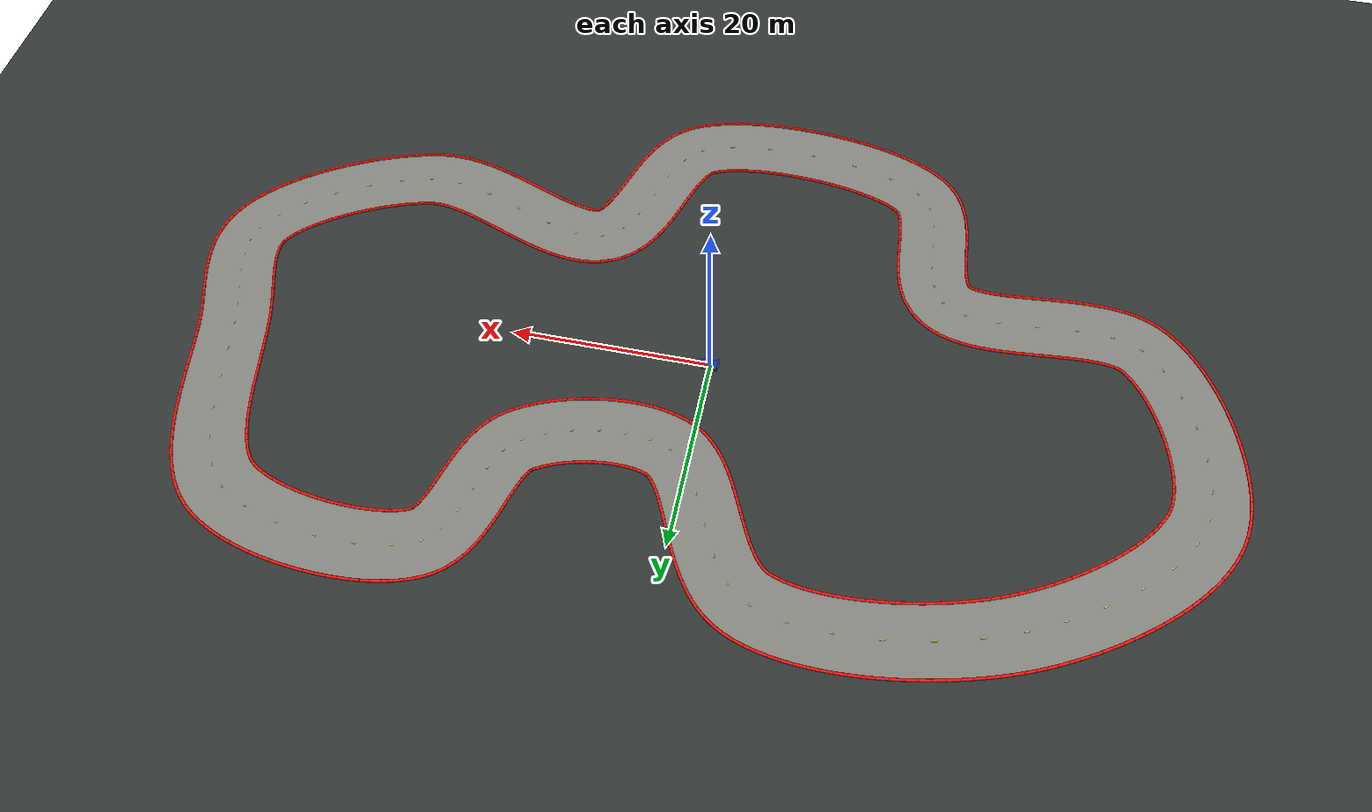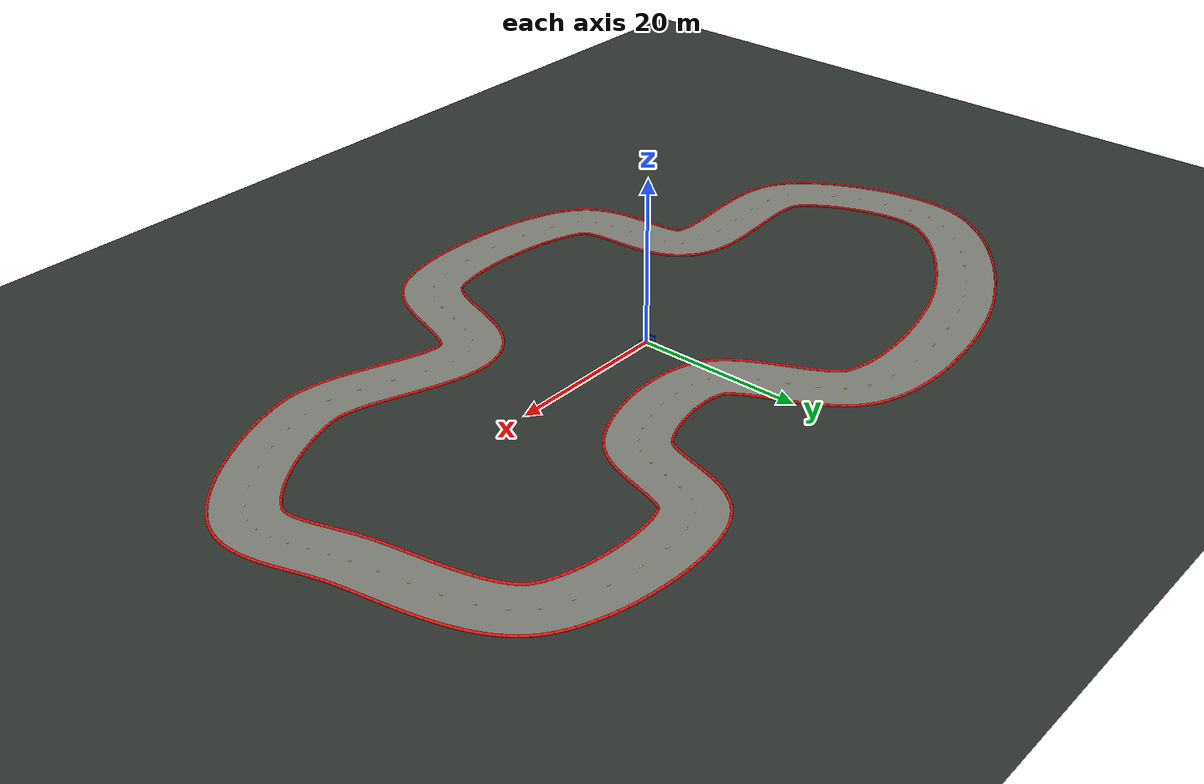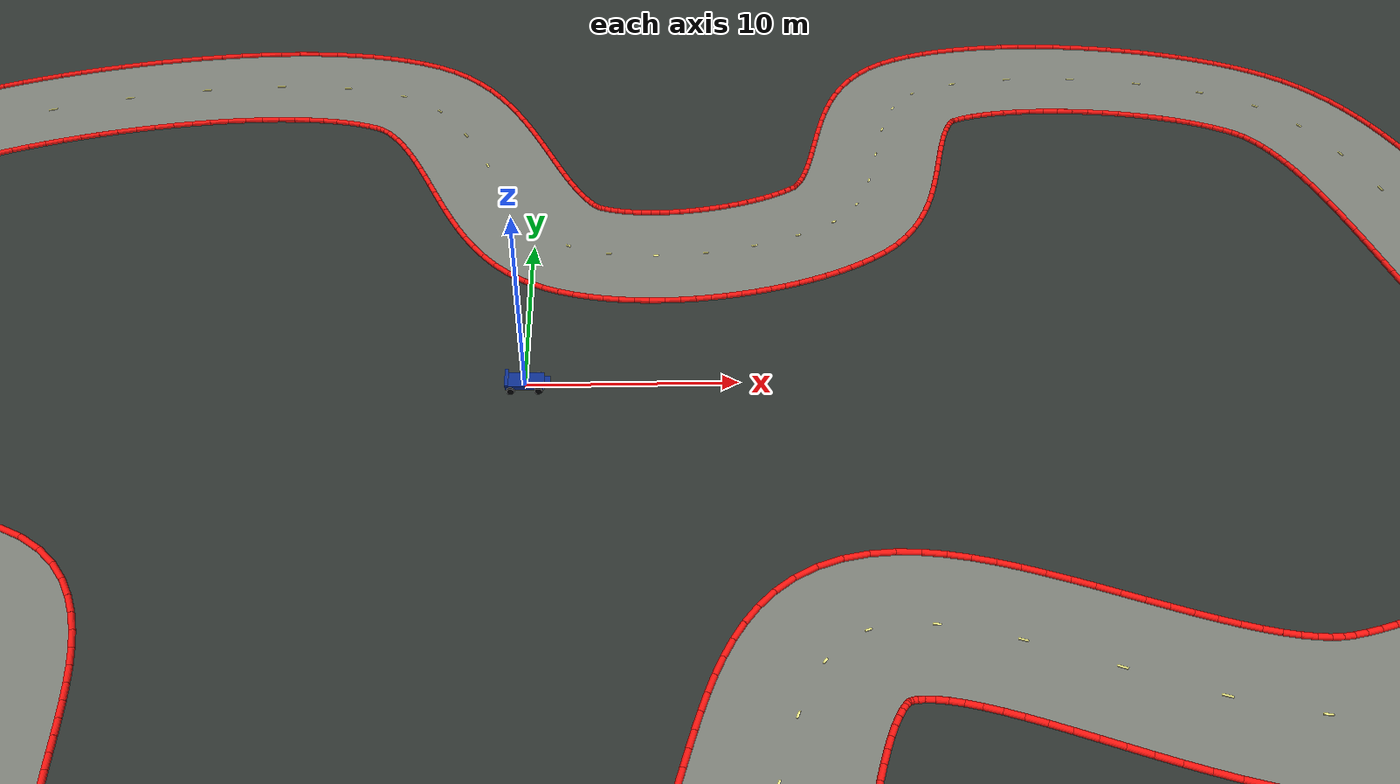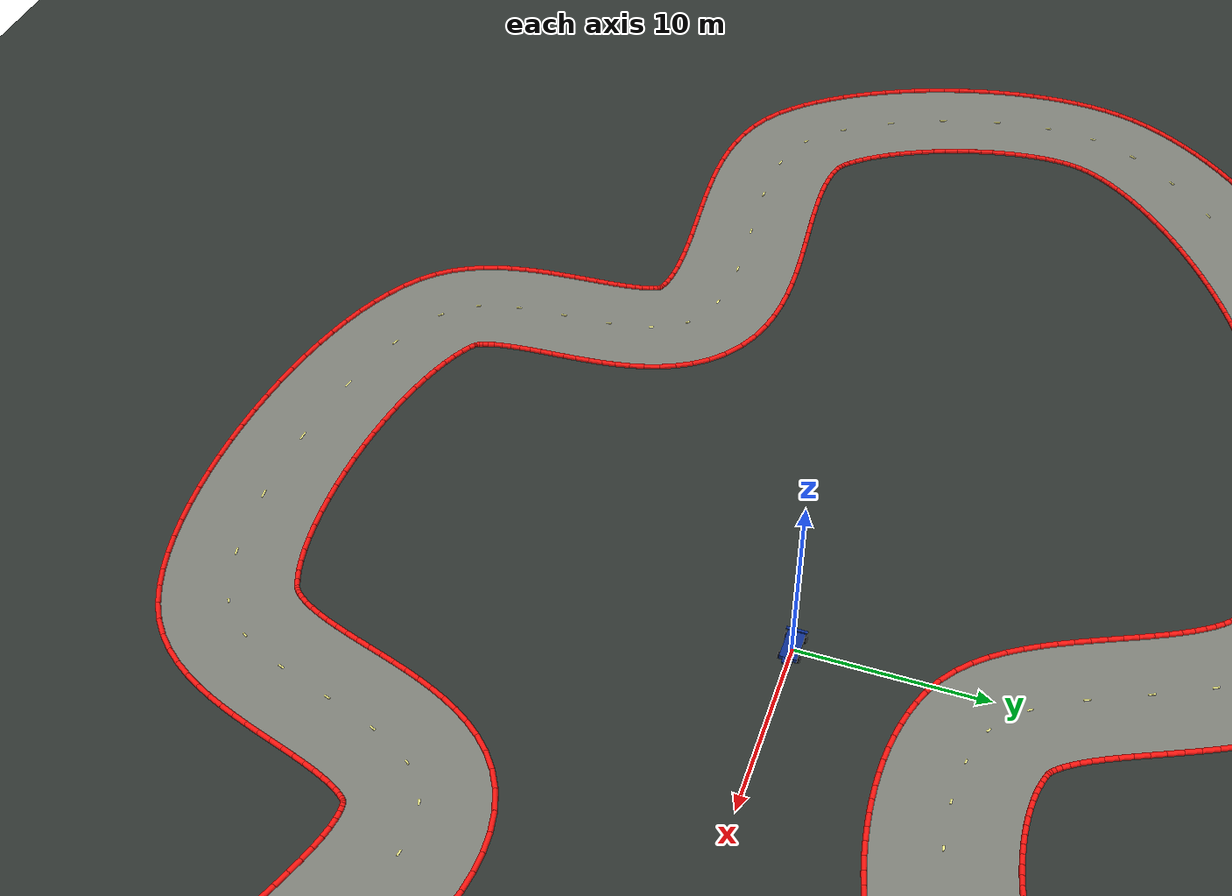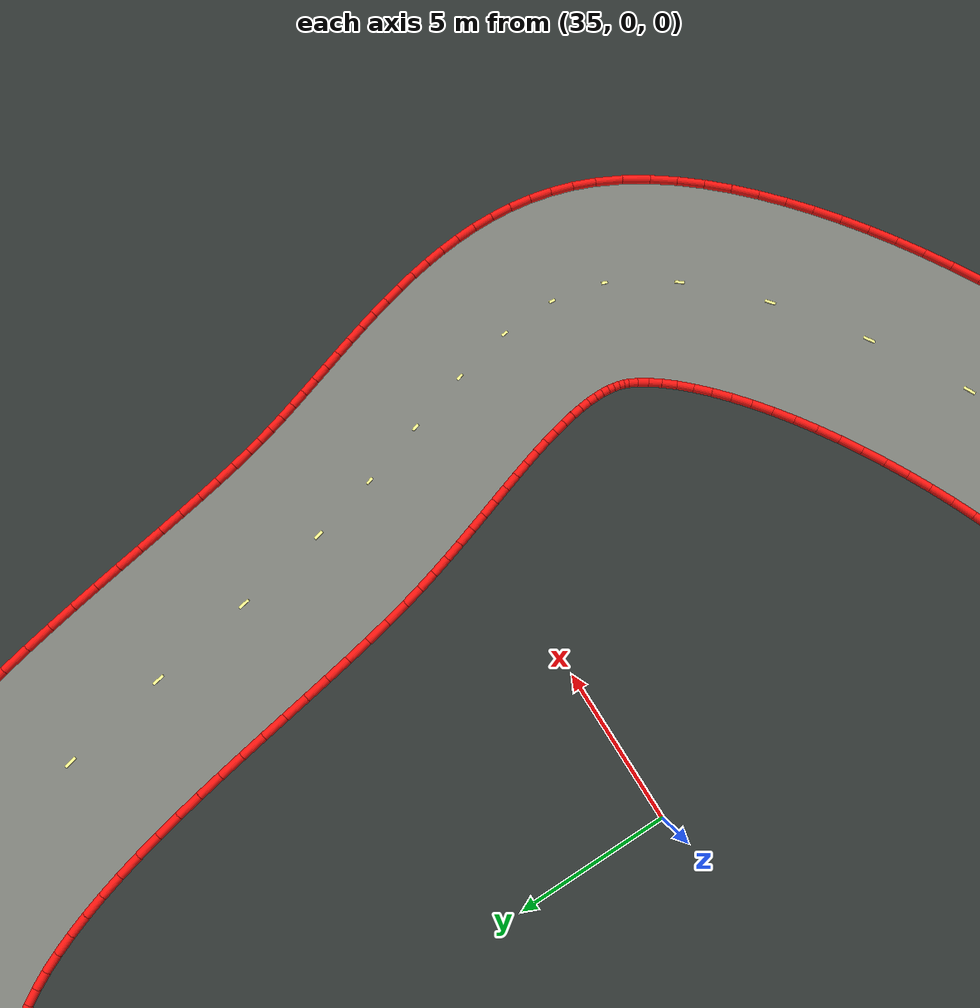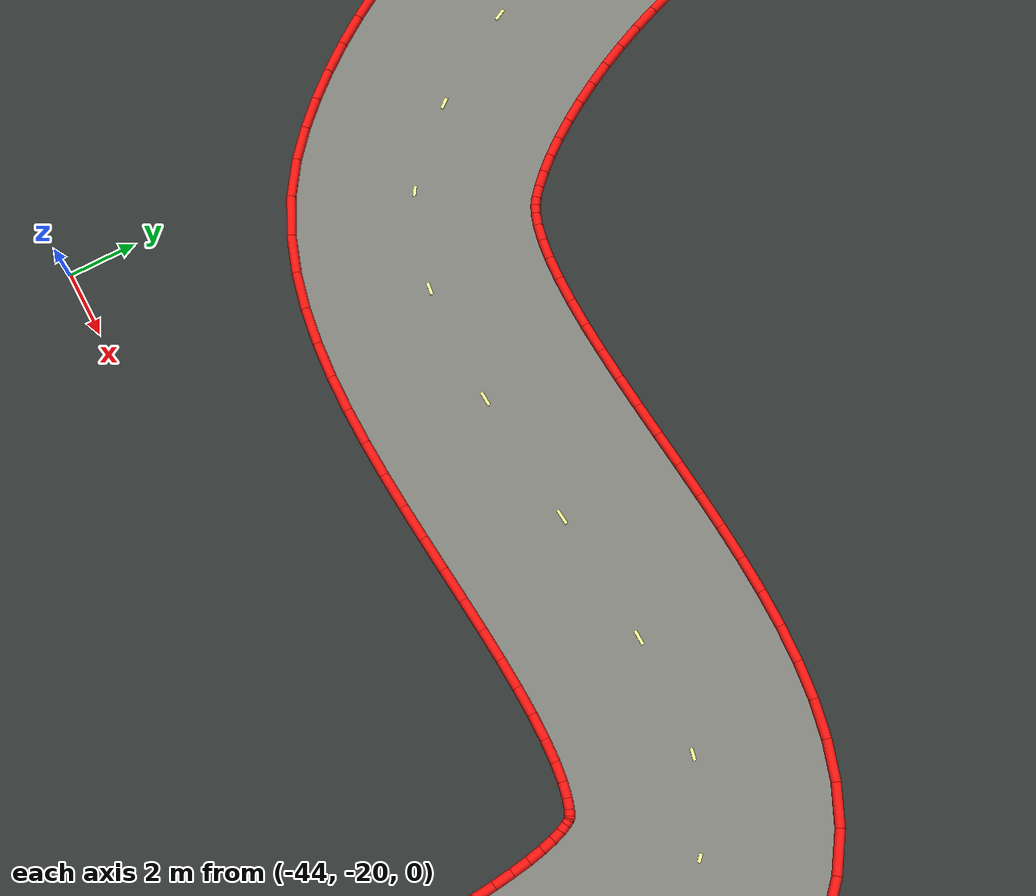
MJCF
<mujoco model="racesim_street_circuit_world">
  <compiler angle="degree" autolimits="true"/>
  <option timestep="0.02" gravity="0 0 -9.81"/>
  <visual>
    <global offwidth="1280" offheight="960"/>
    <headlight ambient="0.35 0.35 0.35" diffuse="0.8 0.8 0.8"/>
  </visual>

  <include file="car.xml"/>
  <include file="street_circuit_track.xml"/>

  <asset>
    <texture name="grid" type="2d" builtin="checker" width="512" height="512"
             rgb1="0.16 0.18 0.17" rgb2="0.20 0.22 0.21"/>
    <material name="ground" texture="grid" texrepeat="12 12" reflectance="0.05"/>
  </asset>

  <worldbody>
    <light name="sun" pos="0 0 30" dir="0 0 -1" diffuse="1.0 1.0 1.0" ambient="0.25 0.25 0.25"/>
    <geom name="ground" type="plane" size="100 100 0.1" material="ground"/>
    <camera name="topdown" pos="0 0 135" xyaxes="1 0 0 0 1 0" fovy="42"/>
    <camera name="follow" mode="trackcom" target="car" pos="-5 0 3" xyaxes="0 -1 0 0.5 0 0.866"/>
  </worldbody>
</mujoco>

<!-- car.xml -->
<mujoco model="simple_car">
  <default>
    <geom friction="1.2 0.02 0.001" density="600"/>
    <joint damping="0.1"/>
  </default>

  <asset>
    <material name="chassis_blue" rgba="0.05 0.18 0.55 1"/>
    <material name="wheel_dark" rgba="0.02 0.02 0.025 1"/>
  </asset>

  <worldbody>
    <body name="car" pos="0 0 0.28">
      <freejoint name="root"/>
      <geom name="chassis" type="box" size="0.9 0.45 0.12" material="chassis_blue"/>
      <geom name="nose" type="box" pos="0.75 0 0.02" size="0.45 0.25 0.06" material="chassis_blue"/>
      <geom name="rear_wing" type="box" pos="-0.85 0 0.22" size="0.08 0.55 0.04" material="chassis_blue"/>

      <body name="front_left_wheel" pos="0.65 0.48 -0.12">
        <joint name="front_left_spin" type="hinge" axis="0 1 0"/>
        <geom type="cylinder" size="0.18 0.08" euler="90 0 0" material="wheel_dark"/>
      </body>
      <body name="front_right_wheel" pos="0.65 -0.48 -0.12">
        <joint name="front_right_spin" type="hinge" axis="0 1 0"/>
        <geom type="cylinder" size="0.18 0.08" euler="90 0 0" material="wheel_dark"/>
      </body>
      <body name="rear_left_wheel" pos="-0.65 0.48 -0.12">
        <joint name="rear_left_spin" type="hinge" axis="0 1 0"/>
        <geom type="cylinder" size="0.18 0.08" euler="90 0 0" material="wheel_dark"/>
      </body>
      <body name="rear_right_wheel" pos="-0.65 -0.48 -0.12">
        <joint name="rear_right_spin" type="hinge" axis="0 1 0"/>
        <geom type="cylinder" size="0.18 0.08" euler="90 0 0" material="wheel_dark"/>
      </body>
    </body>
  </worldbody>
</mujoco>

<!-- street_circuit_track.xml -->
<mujoco model="street_circuit_track_visuals">
  <asset>
    <mesh name="track_surface_mesh" inertia="shell" vertex="44.60308 3.15683 0.02200 44.42057 3.93185 0.02200 44.25042 4.72643 0.02200 44.08996 5.53523 0.02200 43.93609 6.35622 0.02200 43.78612 7.18680 0.02200 43.63763 8.02391 0.02200 43.48842 8.86411 0.02200 43.33644 9.70364 0.02200 43.17979 10.53849 0.02200 43.01673 11.36438 0.02200 42.84568 12.17682 0.02200 42.66523 12.97110 0.02200 42.47420 13.74228 0.02200 42.27172 14.48522 0.02200 42.05725 15.19462 0.02200 41.83077 15.86497 0.02200 41.59280 16.49074 0.02200 41.34464 17.06643 0.02200 41.08846 17.58683 0.02200 40.82741 18.04745 0.02200 40.56556 18.44507 0.02200 40.30752 18.77849 0.02200 40.05763 19.04942 0.02200 39.80577 19.27322 0.02200 39.48075 19.50801 0.02200 39.06070 19.76347 0.02200 38.55598 20.02499 0.02200 37.97560 20.28336 0.02200 37.32888 20.53187 0.02200 36.62501 20.76567 0.02200 35.87288 20.98117 0.02200 35.08106 21.17572 0.02200 34.25783 21.34733 0.02200 33.41123 21.49449 0.02200 32.54915 21.61603 0.02200 31.67938 21.71108 0.02200 30.80967 21.77901 0.02200 29.94783 21.81941 0.02200 29.10178 21.83209 0.02200 28.27962 21.81713 0.02200 27.48980 21.77496 0.02200 26.74116 21.70648 0.02200 26.04313 21.61324 0.02200 25.40589 21.49780 0.02200 24.84051 21.36427 0.02200 24.35902 21.21910 0.02200 23.97416 21.07239 0.02200 23.72293 20.95345 0.02200 23.68092 20.92826 0.02200 23.64712 20.89692 0.02200 23.57652 20.81621 0.02200 23.47261 20.67039 0.02200 23.34417 20.45247 0.02200 23.20049 20.16252 0.02200 23.04897 19.80503 0.02200 22.89454 19.38669 0.02200 22.73977 18.91490 0.02200 22.58531 18.39700 0.02200 22.43037 17.83983 0.02200 22.27298 17.24961 0.02200 22.11028 16.63184 0.02200 21.93853 15.99126 0.02200 21.75317 15.33189 0.02200 21.54870 14.65706 0.02200 21.31839 13.96944 0.02200 21.05401 13.27128 0.02200 20.74534 12.56485 0.02200 20.37977 11.85336 0.02200 19.94221 11.14245 0.02200 19.41595 10.44264 0.02200 18.78540 9.77187 0.02200 18.10128 9.20096 0.02200 17.45062 8.75651 0.02200 16.83055 8.38253 0.02200 16.19033 8.03732 0.02200 15.53121 7.71851 0.02200 14.85444 7.42448 0.02200 14.16135 7.15415 0.02200 13.45337 6.90690 0.02200 12.73198 6.68245 0.02200 11.99877 6.48077 0.02200 11.25533 6.30206 0.02200 10.50332 6.14670 0.02200 9.74437 6.01524 0.02200 8.98011 5.90837 0.02200 8.21212 5.82695 0.02200 7.44193 5.77202 0.02200 6.67096 5.74480 0.02200 5.90055 5.74675 0.02200 5.13192 5.77962 0.02200 4.36619 5.84552 0.02200 3.60438 5.94704 0.02200 2.84750 6.08733 0.02200 2.09665 6.27025 0.02200 1.35328 6.50051 0.02200 0.55959 6.81014 0.02200 -0.34994 7.28773 0.02200 -1.20819 7.89915 0.02200 -1.95026 8.57671 0.02200 -2.59263 9.29452 0.02200 -3.15452 10.03686 0.02200 -3.65348 10.79460 0.02200 -4.10397 11.56202 0.02200 -4.51745 12.33476 0.02200 -4.90287 13.10865 0.02200 -5.26734 13.87919 0.02200 -5.61652 14.64133 0.02200 -5.95495 15.38939 0.02200 -6.28627 16.11711 0.02200 -6.61323 16.81760 0.02200 -6.93771 17.48348 0.02200 -7.26058 18.10692 0.02200 -7.58156 18.67982 0.02200 -7.89888 19.19415 0.02200 -8.20912 19.64246 0.02200 -8.50712 20.01885 0.02200 -8.78633 20.32034 0.02200 -9.04031 20.54860 0.02200 -9.26555 20.71128 0.02200 -9.50966 20.84232 0.02200 -9.97536 21.03288 0.02200 -10.55368 21.22384 0.02200 -11.20505 21.39340 0.02200 -11.92287 21.53737 0.02200 -12.70019 21.65297 0.02200 -13.53010 21.73850 0.02200 -14.40583 21.79312 0.02200 -15.32085 21.81661 0.02200 -16.26890 21.80923 0.02200 -17.24393 21.77156 0.02200 -18.24009 21.70445 0.02200 -19.25170 21.60893 0.02200 -20.27323 21.48618 0.02200 -21.29925 21.33752 0.02200 -22.32440 21.16433 0.02200 -23.34338 20.96809 0.02200 -24.35092 20.75038 0.02200 -25.34174 20.51284 0.02200 -26.31055 20.25721 0.02200 -27.25199 19.98533 0.02200 -28.16059 19.69920 0.02200 -29.03078 19.40097 0.02200 -29.85678 19.09305 0.02200 -30.63821 18.77579 0.02200 -31.36159 18.45817 0.02200 -32.10758 18.10883 0.02200 -32.86764 17.73107 0.02200 -33.63714 17.32662 0.02200 -34.41163 16.89724 0.02200 -35.18675 16.44475 0.02200 -35.95821 15.97099 0.02200 -36.72180 15.47787 0.02200 -37.47332 14.96734 0.02200 -38.20861 14.44147 0.02200 -38.92352 13.90240 0.02200 -39.61392 13.35242 0.02200 -40.27568 12.79399 0.02200 -40.90471 12.22973 0.02200 -41.49694 11.66255 0.02200 -42.04839 11.09564 0.02200 -42.55520 10.53254 0.02200 -43.01371 9.97724 0.02200 -43.42065 9.43419 0.02200 -43.77323 8.90835 0.02200 -44.06953 8.40516 0.02200 -44.30875 7.93034 0.02200 -44.49167 7.48954 0.02200 -44.62377 7.07745 0.02200 -44.71405 6.67751 0.02200 -44.78370 6.20866 0.02200 -44.82705 5.67870 0.02200 -44.84042 5.09574 0.02200 -44.82172 4.46778 0.02200 -44.76998 3.80255 0.02200 -44.68504 3.10737 0.02200 -44.56739 2.38921 0.02200 -44.41789 1.65470 0.02200 -44.23778 0.91022 0.02200 -44.02855 0.16193 0.02200 -43.79190 -0.58418 0.02200 -43.52974 -1.32222 0.02200 -43.24418 -2.04639 0.02200 -42.93756 -2.75092 0.02200 -42.61249 -3.43004 0.02200 -42.27187 -4.07798 0.02200 -41.91904 -4.68894 0.02200 -41.55781 -5.25709 0.02200 -41.19271 -5.77664 0.02200 -40.82911 -6.24191 0.02200 -40.47348 -6.64757 0.02200 -40.13364 -6.98894 0.02200 -39.87007 -7.22270 0.02200 -39.67743 -7.35646 0.02200 -39.44880 -7.46358 0.02200 -39.10360 -7.57815 0.02200 -38.64116 -7.68291 0.02200 -38.07081 -7.76520 0.02200 -37.40590 -7.81819 0.02200 -36.66041 -7.83982 0.02200 -35.84750 -7.83140 0.02200 -34.97903 -7.79639 0.02200 -34.06551 -7.73966 0.02200 -33.11619 -7.66697 0.02200 -32.13923 -7.58463 0.02200 -31.14171 -7.49940 0.02200 -30.12971 -7.41841 0.02200 -29.10819 -7.34921 0.02200 -28.08087 -7.29990 0.02200 -27.05005 -7.27950 0.02200 -26.01637 -7.29848 0.02200 -24.97865 -7.36970 0.02200 -23.93421 -7.50993 0.02200 -22.88033 -7.74189 0.02200 -21.81838 -8.09620 0.02200 -20.76188 -8.61061 0.02200 -19.76995 -9.30243 0.02200 -18.99248 -10.05804 0.02200 -18.37050 -10.87230 0.02200 -17.88514 -11.71609 0.02200 -17.51631 -12.56361 0.02200 -17.24068 -13.40120 0.02200 -17.03703 -14.22336 0.02200 -16.88790 -15.02866 0.02200 -16.77941 -15.81697 0.02200 -16.70054 -16.58802 0.02200 -16.64229 -17.34073 0.02200 -16.59711 -18.07296 0.02200 -16.55849 -18.78150 0.02200 -16.52076 -19.46205 0.02200 -16.47899 -20.10925 0.02200 -16.42914 -20.71668 0.02200 -16.36820 -21.27693 0.02200 -16.29463 -21.78163 0.02200 -16.20891 -22.22181 0.02200 -16.11423 -22.58864 0.02200 -16.01709 -22.87495 0.02200 -15.92716 -23.07794 0.02200 -15.85526 -23.20279 0.02200 -15.80821 -23.26576 0.02200 -15.75080 -23.31838 0.02200 -15.45724 -23.52935 0.02200 -15.01240 -23.79395 0.02200 -14.44649 -24.07528 0.02200 -13.77381 -24.35843 0.02200 -13.00832 -24.63346 0.02200 -12.16316 -24.89363 0.02200 -11.25054 -25.13424 0.02200 -10.28190 -25.35193 0.02200 -9.26811 -25.54420 0.02200 -8.21956 -25.70912 0.02200 -7.14635 -25.84521 0.02200 -6.05836 -25.95128 0.02200 -4.96541 -26.02637 0.02200 -3.87728 -26.06977 0.02200 -2.80386 -26.08096 0.02200 -1.75520 -26.05969 0.02200 -0.74168 -26.00600 0.02200 0.22590 -25.92038 0.02200 1.13613 -25.80396 0.02200 1.97678 -25.65882 0.02200 2.73457 -25.48854 0.02200 3.39502 -25.29908 0.02200 3.94251 -25.10016 0.02200 4.33388 -24.92201 0.02200 4.47477 -24.83633 0.02200 4.60212 -24.72778 0.02200 4.76347 -24.55316 0.02200 4.95401 -24.29939 0.02200 5.16455 -23.96243 0.02200 5.38612 -23.54511 0.02200 5.61202 -23.05424 0.02200 5.83822 -22.49845 0.02200 6.06302 -21.88688 0.02200 6.28664 -21.22845 0.02200 6.51075 -20.53150 0.02200 6.73816 -19.80365 0.02200 6.97271 -19.05175 0.02200 7.21917 -18.28179 0.02200 7.48336 -17.49891 0.02200 7.77241 -16.70741 0.02200 8.09513 -15.91085 0.02200 8.46263 -15.11240 0.02200 8.88908 -14.31563 0.02200 9.39223 -13.52623 0.02200 9.99310 -12.75502 0.02200 10.71316 -12.02211 0.02200 11.56749 -11.36018 0.02200 12.55048 -10.81427 0.02200 13.67539 -10.40692 0.02200 14.80631 -10.17898 0.02200 15.90921 -10.10049 0.02200 16.97608 -10.13779 0.02200 18.00954 -10.26335 0.02200 19.01600 -10.45649 0.02200 20.00199 -10.70174 0.02200 20.97258 -10.98709 0.02200 21.93109 -11.30255 0.02200 22.87914 -11.63931 0.02200 23.81691 -11.98919 0.02200 24.74338 -12.34433 0.02200 25.65653 -12.69706 0.02200 26.55338 -13.03982 0.02200 27.43011 -13.36514 0.02200 28.28206 -13.66573 0.02200 29.10363 -13.93458 0.02200 29.88825 -14.16515 0.02200 30.62834 -14.35175 0.02200 31.31537 -14.49001 0.02200 31.94012 -14.57755 0.02200 32.49359 -14.61486 0.02200 32.96870 -14.60599 0.02200 33.43260 -14.54630 0.02200 33.97562 -14.43317 0.02200 34.61338 -14.27622 0.02200 35.28017 -14.08667 0.02200 35.96976 -13.86590 0.02200 36.67636 -13.61554 0.02200 37.39451 -13.33736 0.02200 38.11902 -13.03330 0.02200 38.84488 -12.70536 0.02200 39.56721 -12.35565 0.02200 40.28125 -11.98639 0.02200 40.98228 -11.59988 0.02200 41.66562 -11.19857 0.02200 42.32659 -10.78505 0.02200 42.96051 -10.36212 0.02200 43.56265 -9.93283 0.02200 44.12827 -9.50056 0.02200 44.65258 -9.06915 0.02200 45.13081 -8.64299 0.02200 45.55824 -8.22725 0.02200 45.93039 -7.82808 0.02200 46.24325 -7.45289 0.02200 46.49381 -7.11060 0.02200 46.68085 -6.81177 0.02200 46.81204 -6.55538 0.02200 46.86803 -6.41392 0.02200 46.91488 -6.25781 0.02200 46.95160 -6.08452 0.02200 46.97759 -5.88790 0.02200 46.99113 -5.66372 0.02200 46.99010 -5.40962 0.02200 46.97250 -5.12488 0.02200 46.93685 -4.80998 0.02200 46.88231 -4.46618 0.02200 46.80872 -4.09516 0.02200 46.71649 -3.69880 0.02200 46.60656 -3.27894 0.02200 46.48026 -2.83732 0.02200 46.33924 -2.37550 0.02200 46.18537 -1.89482 0.02200 46.02074 -1.39643 0.02200 45.84753 -0.88125 0.02200 45.66808 -0.34998 0.02200 45.48481 0.19686 0.02200 45.30021 0.75894 0.02200 45.11692 1.33609 0.02200 44.93763 1.92831 0.02200 44.76520 2.53573 0.02200 51.39692 4.84317 0.02200 51.25030 5.46639 0.02200 51.10623 6.13992 0.02200 50.96330 6.86079 0.02200 50.82057 7.62269 0.02200 50.67665 8.41991 0.02200 50.52991 9.24719 0.02200 50.37852 10.09965 0.02200 50.22044 10.97272 0.02200 50.05352 11.86209 0.02200 49.87544 12.76372 0.02200 49.68374 13.67378 0.02200 49.47577 14.58867 0.02200 49.24863 15.50499 0.02200 48.99915 16.41955 0.02200 48.72380 17.32936 0.02200 48.41857 18.23158 0.02200 48.07885 19.12344 0.02200 47.69930 20.00211 0.02200 47.27369 20.86448 0.02200 46.79481 21.70671 0.02200 46.25455 22.52371 0.02200 45.64422 23.30835 0.02200 44.95542 24.05059 0.02200 44.19423 24.72678 0.02200 43.36605 25.33075 0.02200 42.49928 25.86070 0.02200 41.59567 26.33057 0.02200 40.65838 26.74886 0.02200 39.69020 27.12157 0.02200 38.69408 27.45289 0.02200 37.67326 27.74568 0.02200 36.63130 28.00190 0.02200 35.57206 28.22285 0.02200 34.49962 28.40935 0.02200 33.41824 28.56187 0.02200 32.33225 28.68057 0.02200 31.24604 28.76540 0.02200 30.16393 28.81607 0.02200 29.09015 28.83208 0.02200 28.02870 28.81263 0.02200 26.98329 28.75662 0.02200 25.95720 28.66244 0.02200 24.95314 28.52785 0.02200 23.97305 28.34959 0.02200 23.01801 28.12286 0.02200 22.08811 27.84051 0.02200 21.18276 27.49174 0.02200 20.27707 27.04655 0.02200 19.47579 26.52442 0.02200 18.74973 25.89848 0.02200 18.13659 25.22157 0.02200 17.62559 24.51907 0.02200 17.20063 23.80759 0.02200 16.84512 23.09668 0.02200 16.54434 22.39148 0.02200 16.28607 21.69494 0.02200 16.06043 21.00928 0.02200 15.85945 20.33679 0.02200 15.67663 19.68023 0.02200 15.50662 19.04304 0.02200 15.34500 18.42935 0.02200 15.18817 17.84401 0.02200 15.03340 17.29265 0.02200 14.87888 16.78158 0.02200 14.72404 16.31774 0.02200 14.56980 15.90851 0.02200 14.41907 15.56123 0.02200 14.27715 15.28236 0.02200 14.15183 15.07584 0.02200 14.05251 14.94081 0.02200 13.98749 14.86894 0.02200 13.89872 14.79904 0.02200 13.67886 14.65345 0.02200 13.36245 14.46301 0.02200 13.00570 14.27095 0.02200 12.61285 14.08115 0.02200 12.18814 13.89679 0.02200 11.73571 13.72044 0.02200 11.25963 13.55427 0.02200 10.76388 13.40008 0.02200 10.25239 13.25942 0.02200 9.72902 13.13363 0.02200 9.19762 13.02385 0.02200 8.66202 12.93105 0.02200 8.12609 12.85608 0.02200 7.59372 12.79959 0.02200 7.06889 12.76208 0.02200 6.55564 12.74385 0.02200 6.05812 12.74498 0.02200 5.58059 12.76522 0.02200 5.12743 12.80401 0.02200 4.70310 12.86028 0.02200 4.31206 12.93241 0.02200 3.95869 13.01805 0.02200 3.64705 13.11403 0.02200 3.44041 13.18986 0.02200 3.31385 13.25234 0.02200 3.20180 13.33532 0.02200 3.03280 13.49291 0.02200 2.81675 13.73735 0.02200 2.56630 14.07075 0.02200 2.29245 14.48864 0.02200 2.00309 14.98310 0.02200 1.70309 15.54489 0.02200 1.39486 16.16455 0.02200 1.07893 16.83297 0.02200 0.75439 17.54159 0.02200 0.41923 18.28245 0.02200 0.07050 19.04822 0.02200 -0.29560 19.83215 0.02200 -0.68376 20.62802 0.02200 -1.09967 21.43004 0.02200 -1.55021 22.23268 0.02200 -2.04368 23.03037 0.02200 -2.59007 23.81694 0.02200 -3.20113 24.58466 0.02200 -3.88996 25.32290 0.02200 -4.66958 26.01638 0.02200 -5.55006 26.64383 0.02200 -6.49034 27.15768 0.02200 -7.53189 27.59256 0.02200 -8.56851 27.93645 0.02200 -9.63095 28.21412 0.02200 -10.71697 28.43272 0.02200 -11.82465 28.59800 0.02200 -12.95208 28.71459 0.02200 -14.09717 28.78631 0.02200 -15.25760 28.81633 0.02200 -16.43081 28.80736 0.02200 -17.61400 28.76177 0.02200 -18.80416 28.68169 0.02200 -19.99813 28.56902 0.02200 -21.19260 28.42555 0.02200 -22.38416 28.25293 0.02200 -23.56932 28.05273 0.02200 -24.74453 27.82643 0.02200 -25.90622 27.57541 0.02200 -27.05082 27.30099 0.02200 -28.17480 27.00440 0.02200 -29.27466 26.68674 0.02200 -30.34700 26.34898 0.02200 -31.38859 25.99193 0.02200 -32.39634 25.61614 0.02200 -33.36179 25.22421 0.02200 -34.25281 24.83319 0.02200 -35.14975 24.41322 0.02200 -36.05392 23.96385 0.02200 -36.96273 23.48620 0.02200 -37.87341 22.98132 0.02200 -38.78310 22.45027 0.02200 -39.68886 21.89403 0.02200 -40.58768 21.31353 0.02200 -41.47653 20.70967 0.02200 -42.35237 20.08321 0.02200 -43.21210 19.43486 0.02200 -44.05264 18.76517 0.02200 -44.87089 18.07452 0.02200 -45.66373 17.36312 0.02200 -46.42800 16.63092 0.02200 -47.16045 15.87757 0.02200 -47.85774 15.10234 0.02200 -48.51627 14.30412 0.02200 -49.13213 13.48129 0.02200 -49.70084 12.63171 0.02200 -50.21715 11.75281 0.02200 -50.67460 10.84169 0.02200 -51.06519 9.89556 0.02200 -51.37623 8.92255 0.02200 -51.59300 7.97366 0.02200 -51.73706 7.01540 0.02200 -51.81725 6.04885 0.02200 -51.84039 5.07480 0.02200 -51.81174 4.09410 0.02200 -51.73543 3.10792 0.02200 -51.61475 2.11783 0.02200 -51.45241 1.12573 0.02200 -51.25068 0.13386 0.02200 -51.01149 -0.85525 0.02200 -50.73651 -1.83890 0.02200 -50.42719 -2.81418 0.02200 -50.08478 -3.77811 0.02200 -49.71033 -4.72761 0.02200 -49.30465 -5.65957 0.02200 -48.86831 -6.57087 0.02200 -48.40154 -7.45840 0.02200 -47.90419 -8.31908 0.02200 -47.37558 -9.14985 0.02200 -46.81435 -9.94763 0.02200 -46.21829 -10.70921 0.02200 -45.58409 -11.43105 0.02200 -44.90707 -12.10893 0.02200 -44.12993 -12.77730 0.02200 -43.16505 -13.42577 0.02200 -42.09462 -13.94429 0.02200 -41.01251 -14.31284 0.02200 -39.93263 -14.56274 0.02200 -38.85893 -14.72069 0.02200 -37.79131 -14.80757 0.02200 -36.72905 -14.83949 0.02200 -35.67225 -14.82921 0.02200 -34.62232 -14.78730 0.02200 -33.58202 -14.72295 0.02200 -32.55533 -14.64446 0.02200 -31.54738 -14.55956 0.02200 -30.56434 -14.47555 0.02200 -29.61339 -14.39935 0.02200 -28.70285 -14.33746 0.02200 -27.84224 -14.29583 0.02200 -27.04253 -14.27950 0.02200 -26.31634 -14.29205 0.02200 -25.67811 -14.33467 0.02200 -25.14379 -14.40463 0.02200 -24.72934 -14.49328 0.02200 -24.44668 -14.58404 0.02200 -24.29554 -14.65323 0.02200 -24.23005 -14.69757 0.02200 -24.23728 -14.69400 0.02200 -24.20596 -14.73847 0.02200 -24.14418 -14.85049 0.02200 -24.06128 -15.04621 0.02200 -23.96980 -15.32966 0.02200 -23.88023 -15.69671 0.02200 -23.79925 -16.13915 0.02200 -23.72996 -16.64749 0.02200 -23.67264 -17.21234 0.02200 -23.62551 -17.82518 0.02200 -23.58536 -18.47848 0.02200 -23.54793 -19.16585 0.02200 -23.50815 -19.88194 0.02200 -23.46015 -20.62248 0.02200 -23.39724 -21.38424 0.02200 -23.31164 -22.16502 0.02200 -23.19413 -22.96354 0.02200 -23.03347 -23.77915 0.02200 -22.81571 -24.61103 0.02200 -22.52358 -25.45673 0.02200 -22.13664 -26.30941 0.02200 -21.63332 -27.15426 0.02200 -20.99603 -27.96539 0.02200 -20.24920 -28.68162 0.02200 -19.32857 -29.36141 0.02200 -18.37358 -29.93419 0.02200 -17.36999 -30.43556 0.02200 -16.31952 -30.87911 0.02200 -15.22420 -31.27348 0.02200 -14.08690 -31.62410 0.02200 -12.91139 -31.93436 0.02200 -11.70224 -32.20632 0.02200 -10.46457 -32.44119 0.02200 -9.20400 -32.63955 0.02200 -7.92643 -32.80161 0.02200 -6.63796 -32.92724 0.02200 -5.34478 -33.01609 0.02200 -4.05311 -33.06756 0.02200 -2.76906 -33.08088 0.02200 -1.49856 -33.05498 0.02200 -0.24725 -32.98851 0.02200 0.97967 -32.87968 0.02200 2.17763 -32.72605 0.02200 3.34286 -32.52423 0.02200 4.47263 -32.26933 0.02200 5.56542 -31.95410 0.02200 6.62087 -31.56749 0.02200 7.66612 -31.07799 0.02200 8.57741 -30.50805 0.02200 9.40607 -29.81915 0.02200 10.11309 -29.06777 0.02200 10.71184 -28.28027 0.02200 11.22005 -27.47396 0.02200 11.65523 -26.65931 0.02200 12.03262 -25.84277 0.02200 12.36480 -25.02901 0.02200 12.66200 -24.22216 0.02200 12.93256 -23.42659 0.02200 13.18335 -22.64724 0.02200 13.42009 -21.88975 0.02200 13.64750 -21.16058 0.02200 13.86934 -20.46701 0.02200 14.08833 -19.81718 0.02200 14.30591 -19.22007 0.02200 14.52178 -18.68540 0.02200 14.73339 -18.22328 0.02200 14.93512 -17.84344 0.02200 15.11775 -17.55344 0.02200 15.26881 -17.35577 0.02200 15.37536 -17.24359 0.02200 15.43089 -17.19749 0.02200 15.44952 -17.18573 0.02200 15.55125 -17.15089 0.02200 15.73322 -17.11734 0.02200 16.02292 -17.09957 0.02200 16.42181 -17.11582 0.02200 16.92075 -17.17816 0.02200 17.50676 -17.29185 0.02200 18.16678 -17.45689 0.02200 18.88918 -17.66986 0.02200 19.66411 -17.92530 0.02200 20.48341 -18.21658 0.02200 21.34033 -18.53645 0.02200 22.22937 -18.87730 0.02200 23.14600 -19.23138 0.02200 24.08665 -19.59079 0.02200 25.04859 -19.94757 0.02200 26.02995 -20.29355 0.02200 27.02979 -20.62032 0.02200 28.04811 -20.91896 0.02200 29.08596 -21.17972 0.02200 30.14534 -21.39153 0.02200 31.22891 -21.54132 0.02200 32.33912 -21.61316 0.02200 33.47652 -21.58755 0.02200 34.56740 -21.45370 0.02200 35.51327 -21.26220 0.02200 36.40605 -21.04278 0.02200 37.30394 -20.78774 0.02200 38.20564 -20.49922 0.02200 39.10941 -20.17909 0.02200 40.01319 -19.82909 0.02200 40.91464 -19.45082 0.02200 41.81125 -19.04576 0.02200 42.70036 -18.61532 0.02200 43.57923 -18.16080 0.02200 44.44504 -17.68341 0.02200 45.29495 -17.18422 0.02200 46.12610 -16.66415 0.02200 46.93567 -16.12390 0.02200 47.72084 -15.56394 0.02200 48.47884 -14.98441 0.02200 49.20692 -14.38497 0.02200 49.90234 -13.76475 0.02200 50.56229 -13.12209 0.02200 51.18373 -12.45436 0.02200 51.76313 -11.75765 0.02200 52.29599 -11.02655 0.02200 52.77600 -10.25403 0.02200 53.18796 -9.44462 0.02200 53.47553 -8.72498 0.02200 53.69372 -8.00348 0.02200 53.84819 -7.28326 0.02200 53.94417 -6.57108 0.02200 53.98804 -5.87177 0.02200 53.98660 -5.18829 0.02200 53.94648 -4.52196 0.02200 53.87384 -3.87291 0.02200 53.77417 -3.24048 0.02200 53.65229 -2.62359 0.02200 53.51244 -2.02097 0.02200 53.35834 -1.43139 0.02200 53.19333 -0.85369 0.02200 53.02040 -0.28694 0.02200 52.84234 0.26962 0.02200 52.66173 0.81652 0.02200 52.48103 1.35407 0.02200 52.30258 1.88240 0.02200 52.12860 2.40139 0.02200 51.96126 2.91080 0.02200 51.80259 3.41016 0.02200 51.65453 3.89889 0.02200 51.51891 4.37625 0.02200" face="0 361 1 0 360 361 1 362 2 1 361 362 2 363 3 2 362 363 3 364 4 3 363 364 4 365 5 4 364 365 5 366 6 5 365 366 6 367 7 6 366 367 7 368 8 7 367 368 8 369 9 8 368 369 9 370 10 9 369 370 10 371 11 10 370 371 11 372 12 11 371 372 12 373 13 12 372 373 13 374 14 13 373 374 14 375 15 14 374 375 15 376 16 15 375 376 16 377 17 16 376 377 17 378 18 17 377 378 18 379 19 18 378 379 19 380 20 19 379 380 20 381 21 20 380 381 21 382 22 21 381 382 22 383 23 22 382 383 23 384 24 23 383 384 24 385 25 24 384 385 25 386 26 25 385 386 26 387 27 26 386 387 27 388 28 27 387 388 28 389 29 28 388 389 29 390 30 29 389 390 30 391 31 30 390 391 31 392 32 31 391 392 32 393 33 32 392 393 33 394 34 33 393 394 34 395 35 34 394 395 35 396 36 35 395 396 36 397 37 36 396 397 37 398 38 37 397 398 38 399 39 38 398 399 39 400 40 39 399 400 40 401 41 40 400 401 41 402 42 41 401 402 42 403 43 42 402 403 43 404 44 43 403 404 44 405 45 44 404 405 45 406 46 45 405 406 46 407 47 46 406 407 47 408 48 47 407 408 48 409 49 48 408 409 49 410 50 49 409 410 50 411 51 50 410 411 51 412 52 51 411 412 52 413 53 52 412 413 53 414 54 53 413 414 54 415 55 54 414 415 55 416 56 55 415 416 56 417 57 56 416 417 57 418 58 57 417 418 58 419 59 58 418 419 59 420 60 59 419 420 60 421 61 60 420 421 61 422 62 61 421 422 62 423 63 62 422 423 63 424 64 63 423 424 64 425 65 64 424 425 65 426 66 65 425 426 66 427 67 66 426 427 67 428 68 67 427 428 68 429 69 68 428 429 69 430 70 69 429 430 70 431 71 70 430 431 71 432 72 71 431 432 72 433 73 72 432 433 73 434 74 73 433 434 74 435 75 74 434 435 75 436 76 75 435 436 76 437 77 76 436 437 77 438 78 77 437 438 78 439 79 78 438 439 79 440 80 79 439 440 80 441 81 80 440 441 81 442 82 81 441 442 82 443 83 82 442 443 83 444 84 83 443 444 84 445 85 84 444 445 85 446 86 85 445 446 86 447 87 86 446 447 87 448 88 87 447 448 88 449 89 88 448 449 89 450 90 89 449 450 90 451 91 90 450 451 91 452 92 91 451 452 92 453 93 92 452 453 93 454 94 93 453 454 94 455 95 94 454 455 95 456 96 95 455 456 96 457 97 96 456 457 97 458 98 97 457 458 98 459 99 98 458 459 99 460 100 99 459 460 100 461 101 100 460 461 101 462 102 101 461 462 102 463 103 102 462 463 103 464 104 103 463 464 104 465 105 104 464 465 105 466 106 105 465 466 106 467 107 106 466 467 107 468 108 107 467 468 108 469 109 108 468 469 109 470 110 109 469 470 110 471 111 110 470 471 111 472 112 111 471 472 112 473 113 112 472 473 113 474 114 113 473 474 114 475 115 114 474 475 115 476 116 115 475 476 116 477 117 116 476 477 117 478 118 117 477 478 118 479 119 118 478 479 119 480 120 119 479 480 120 481 121 120 480 481 121 482 122 121 481 482 122 483 123 122 482 483 123 484 124 123 483 484 124 485 125 124 484 485 125 486 126 125 485 486 126 487 127 126 486 487 127 488 128 127 487 488 128 489 129 128 488 489 129 490 130 129 489 490 130 491 131 130 490 491 131 492 132 131 491 492 132 493 133 132 492 493 133 494 134 133 493 494 134 495 135 134 494 495 135 496 136 135 495 496 136 497 137 136 496 497 137 498 138 137 497 498 138 499 139 138 498 499 139 500 140 139 499 500 140 501 141 140 500 501 141 502 142 141 501 502 142 503 143 142 502 503 143 504 144 143 503 504 144 505 145 144 504 505 145 506 146 145 505 506 146 507 147 146 506 507 147 508 148 147 507 508 148 509 149 148 508 509 149 510 150 149 509 510 150 511 151 150 510 511 151 512 152 151 511 512 152 513 153 152 512 513 153 514 154 153 513 514 154 515 155 154 514 515 155 516 156 155 515 516 156 517 157 156 516 517 157 518 158 157 517 518 158 519 159 158 518 519 159 520 160 159 519 520 160 521 161 160 520 521 161 522 162 161 521 522 162 523 163 162 522 523 163 524 164 163 523 524 164 525 165 164 524 525 165 526 166 165 525 526 166 527 167 166 526 527 167 528 168 167 527 528 168 529 169 168 528 529 169 530 170 169 529 530 170 531 171 170 530 531 171 532 172 171 531 532 172 533 173 172 532 533 173 534 174 173 533 534 174 535 175 174 534 535 175 536 176 175 535 536 176 537 177 176 536 537 177 538 178 177 537 538 178 539 179 178 538 539 179 540 180 179 539 540 180 541 181 180 540 541 181 542 182 181 541 542 182 543 183 182 542 543 183 544 184 183 543 544 184 545 185 184 544 545 185 546 186 185 545 546 186 547 187 186 546 547 187 548 188 187 547 548 188 549 189 188 548 549 189 550 190 189 549 550 190 551 191 190 550 551 191 552 192 191 551 552 192 553 193 192 552 553 193 554 194 193 553 554 194 555 195 194 554 555 195 556 196 195 555 556 196 557 197 196 556 557 197 558 198 197 557 558 198 559 199 198 558 559 199 560 200 199 559 560 200 561 201 200 560 561 201 562 202 201 561 562 202 563 203 202 562 563 203 564 204 203 563 564 204 565 205 204 564 565 205 566 206 205 565 566 206 567 207 206 566 567 207 568 208 207 567 568 208 569 209 208 568 569 209 570 210 209 569 570 210 571 211 210 570 571 211 572 212 211 571 572 212 573 213 212 572 573 213 574 214 213 573 574 214 575 215 214 574 575 215 576 216 215 575 576 216 577 217 216 576 577 217 578 218 217 577 578 218 579 219 218 578 579 219 580 220 219 579 580 220 581 221 220 580 581 221 582 222 221 581 582 222 583 223 222 582 583 223 584 224 223 583 584 224 585 225 224 584 585 225 586 226 225 585 586 226 587 227 226 586 587 227 588 228 227 587 588 228 589 229 228 588 589 229 590 230 229 589 590 230 591 231 230 590 591 231 592 232 231 591 592 232 593 233 232 592 593 233 594 234 233 593 594 234 595 235 234 594 595 235 596 236 235 595 596 236 597 237 236 596 597 237 598 238 237 597 598 238 599 239 238 598 599 239 600 240 239 599 600 240 601 241 240 600 601 241 602 242 241 601 602 242 603 243 242 602 603 243 604 244 243 603 604 244 605 245 244 604 605 245 606 246 245 605 606 246 607 247 246 606 607 247 608 248 247 607 608 248 609 249 248 608 609 249 610 250 249 609 610 250 611 251 250 610 611 251 612 252 251 611 612 252 613 253 252 612 613 253 614 254 253 613 614 254 615 255 254 614 615 255 616 256 255 615 616 256 617 257 256 616 617 257 618 258 257 617 618 258 619 259 258 618 619 259 620 260 259 619 620 260 621 261 260 620 621 261 622 262 261 621 622 262 623 263 262 622 623 263 624 264 263 623 624 264 625 265 264 624 625 265 626 266 265 625 626 266 627 267 266 626 627 267 628 268 267 627 628 268 629 269 268 628 629 269 630 270 269 629 630 270 631 271 270 630 631 271 632 272 271 631 632 272 633 273 272 632 633 273 634 274 273 633 634 274 635 275 274 634 635 275 636 276 275 635 636 276 637 277 276 636 637 277 638 278 277 637 638 278 639 279 278 638 639 279 640 280 279 639 640 280 641 281 280 640 641 281 642 282 281 641 642 282 643 283 282 642 643 283 644 284 283 643 644 284 645 285 284 644 645 285 646 286 285 645 646 286 647 287 286 646 647 287 648 288 287 647 648 288 649 289 288 648 649 289 650 290 289 649 650 290 651 291 290 650 651 291 652 292 291 651 652 292 653 293 292 652 653 293 654 294 293 653 654 294 655 295 294 654 655 295 656 296 295 655 656 296 657 297 296 656 657 297 658 298 297 657 658 298 659 299 298 658 659 299 660 300 299 659 660 300 661 301 300 660 661 301 662 302 301 661 662 302 663 303 302 662 663 303 664 304 303 663 664 304 665 305 304 664 665 305 666 306 305 665 666 306 667 307 306 666 667 307 668 308 307 667 668 308 669 309 308 668 669 309 670 310 309 669 670 310 671 311 310 670 671 311 672 312 311 671 672 312 673 313 312 672 673 313 674 314 313 673 674 314 675 315 314 674 675 315 676 316 315 675 676 316 677 317 316 676 677 317 678 318 317 677 678 318 679 319 318 678 679 319 680 320 319 679 680 320 681 321 320 680 681 321 682 322 321 681 682 322 683 323 322 682 683 323 684 324 323 683 684 324 685 325 324 684 685 325 686 326 325 685 686 326 687 327 326 686 687 327 688 328 327 687 688 328 689 329 328 688 689 329 690 330 329 689 690 330 691 331 330 690 691 331 692 332 331 691 692 332 693 333 332 692 693 333 694 334 333 693 694 334 695 335 334 694 695 335 696 336 335 695 696 336 697 337 336 696 697 337 698 338 337 697 698 338 699 339 338 698 699 339 700 340 339 699 700 340 701 341 340 700 701 341 702 342 341 701 702 342 703 343 342 702 703 343 704 344 343 703 704 344 705 345 344 704 705 345 706 346 345 705 706 346 707 347 346 706 707 347 708 348 347 707 708 348 709 349 348 708 709 349 710 350 349 709 710 350 711 351 350 710 711 351 712 352 351 711 712 352 713 353 352 712 713 353 714 354 353 713 714 354 715 355 354 714 715 355 716 356 355 715 716 356 717 357 356 716 717 357 718 358 357 717 718 358 719 359 358 718 719 359 360 0 359 719 360"/>
    <material name="track_asphalt" rgba="0.48 0.49 0.46 1" emission="0.08"/>
    <material name="track_boundary" rgba="0.95 0.08 0.06 1" emission="0.05"/>
    <material name="track_centerline" rgba="1.0 0.95 0.55 1" emission="0.15"/>
  </asset>
  <worldbody>
    <geom name="track_surface" type="mesh" mesh="track_surface_mesh" material="track_asphalt" contype="0" conaffinity="0"/>
    <geom name="track_left_boundary_000" type="capsule" fromto="44.60308 3.15683 0.09 44.42057 3.93185 0.09" size="0.14" material="track_boundary" contype="0" conaffinity="0"/>
    <geom name="track_left_boundary_001" type="capsule" fromto="44.42057 3.93185 0.09 44.25042 4.72643 0.09" size="0.14" material="track_boundary" contype="0" conaffinity="0"/>
    <geom name="track_left_boundary_002" type="capsule" fromto="44.25042 4.72643 0.09 44.08996 5.53523 0.09" size="0.14" material="track_boundary" contype="0" conaffinity="0"/>
    <geom name="track_left_boundary_003" type="capsule" fromto="44.08996 5.53523 0.09 43.93609 6.35622 0.09" size="0.14" material="track_boundary" contype="0" conaffinity="0"/>
    <geom name="track_left_boundary_004" type="capsule" fromto="43.93609 6.35622 0.09 43.78612 7.18680 0.09" size="0.14" material="track_boundary" contype="0" conaffinity="0"/>
    <geom name="track_left_boundary_005" type="capsule" fromto="43.78612 7.18680 0.09 43.63763 8.02391 0.09" size="0.14" material="track_boundary" contype="0" conaffinity="0"/>
    <geom name="track_left_boundary_006" type="capsule" fromto="43.63763 8.02391 0.09 43.48842 8.86411 0.09" size="0.14" material="track_boundary" contype="0" conaffinity="0"/>
    <geom name="track_left_boundary_007" type="capsule" fromto="43.48842 8.86411 0.09 43.33644 9.70364 0.09" size="0.14" material="track_boundary" contype="0" conaffinity="0"/>
    <geom name="track_left_boundary_008" type="capsule" fromto="43.33644 9.70364 0.09 43.17979 10.53849 0.09" size="0.14" material="track_boundary" contype="0" conaffinity="0"/>
    <geom name="track_left_boundary_009" type="capsule" fromto="43.17979 10.53849 0.09 43.01673 11.36438 0.09" size="0.14" material="track_boundary" contype="0" conaffinity="0"/>
    <geom name="track_left_boundary_010" type="capsule" fromto="43.01673 11.36438 0.09 42.84568 12.17682 0.09" size="0.14" material="track_boundary" contype="0" conaffinity="0"/>
    <geom name="track_left_boundary_011" type="capsule" fromto="42.84568 12.17682 0.09 42.66523 12.97110 0.09" size="0.14" material="track_boundary" contype="0" conaffinity="0"/>
    <geom name="track_left_boundary_012" type="capsule" fromto="42.66523 12.97110 0.09 42.47420 13.74228 0.09" size="0.14" material="track_boundary" contype="0" conaffinity="0"/>
    <geom name="track_left_boundary_013" type="capsule" fromto="42.47420 13.74228 0.09 42.27172 14.48522 0.09" size="0.14" material="track_boundary" contype="0" conaffinity="0"/>
    <geom name="track_left_boundary_014" type="capsule" fromto="42.27172 14.48522 0.09 42.05725 15.19462 0.09" size="0.14" material="track_boundary" contype="0" conaffinity="0"/>
    <geom name="track_left_boundary_015" type="capsule" fromto="42.05725 15.19462 0.09 41.83077 15.86497 0.09" size="0.14" material="track_boundary" contype="0" conaffinity="0"/>
    <geom name="track_left_boundary_016" type="capsule" fromto="41.83077 15.86497 0.09 41.59280 16.49074 0.09" size="0.14" material="track_boundary" contype="0" conaffinity="0"/>
    <geom name="track_left_boundary_017" type="capsule" fromto="41.59280 16.49074 0.09 41.34464 17.06643 0.09" size="0.14" material="track_boundary" contype="0" conaffinity="0"/>
    <geom name="track_left_boundary_018" type="capsule" fromto="41.34464 17.06643 0.09 41.08846 17.58683 0.09" size="0.14" material="track_boundary" contype="0" conaffinity="0"/>
    <geom name="track_left_boundary_019" type="capsule" fromto="41.08846 17.58683 0.09 40.82741 18.04745 0.09" size="0.14" material="track_boundary" contype="0" conaffinity="0"/>
    <geom name="track_left_boundary_020" type="capsule" fromto="40.82741 18.04745 0.09 40.56556 18.44507 0.09" size="0.14" material="track_boundary" contype="0" conaffinity="0"/>
    <geom name="track_left_boundary_021" type="capsule" fromto="40.56556 18.44507 0.09 40.30752 18.77849 0.09" size="0.14" material="track_boundary" contype="0" conaffinity="0"/>
    <geom name="track_left_boundary_022" type="capsule" fromto="40.30752 18.77849 0.09 40.05763 19.04942 0.09" size="0.14" material="track_boundary" contype="0" conaffinity="0"/>
    <geom name="track_left_boundary_023" type="capsule" fromto="40.05763 19.04942 0.09 39.80577 19.27322 0.09" size="0.14" material="track_boundary" contype="0" conaffinity="0"/>
    <geom name="track_left_boundary_024" type="capsule" fromto="39.80577 19.27322 0.09 39.48075 19.50801 0.09" size="0.14" material="track_boundary" contype="0" conaffinity="0"/>
    <geom name="track_left_boundary_025" type="capsule" fromto="39.48075 19.50801 0.09 39.06070 19.76347 0.09" size="0.14" material="track_boundary" contype="0" conaffinity="0"/>
    <geom name="track_left_boundary_026" type="capsule" fromto="39.06070 19.76347 0.09 38.55598 20.02499 0.09" size="0.14" material="track_boundary" contype="0" conaffinity="0"/>
    <geom name="track_left_boundary_027" type="capsule" fromto="38.55598 20.02499 0.09 37.97560 20.28336 0.09" size="0.14" material="track_boundary" contype="0" conaffinity="0"/>
    <geom name="track_left_boundary_028" type="capsule" fromto="37.97560 20.28336 0.09 37.32888 20.53187 0.09" size="0.14" material="track_boundary" contype="0" conaffinity="0"/>
    <geom name="track_left_boundary_029" type="capsule" fromto="37.32888 20.53187 0.09 36.62501 20.76567 0.09" size="0.14" material="track_boundary" contype="0" conaffinity="0"/>
    <geom name="track_left_boundary_030" type="capsule" fromto="36.62501 20.76567 0.09 35.87288 20.98117 0.09" size="0.14" material="track_boundary" contype="0" conaffinity="0"/>
    <geom name="track_left_boundary_031" type="capsule" fromto="35.87288 20.98117 0.09 35.08106 21.17572 0.09" size="0.14" material="track_boundary" contype="0" conaffinity="0"/>
    <geom name="track_left_boundary_032" type="capsule" fromto="35.08106 21.17572 0.09 34.25783 21.34733 0.09" size="0.14" material="track_boundary" contype="0" conaffinity="0"/>
    <geom name="track_left_boundary_033" type="capsule" fromto="34.25783 21.34733 0.09 33.41123 21.49449 0.09" size="0.14" material="track_boundary" contype="0" conaffinity="0"/>
    <geom name="track_left_boundary_034" type="capsule" fromto="33.41123 21.49449 0.09 32.54915 21.61603 0.09" size="0.14" material="track_boundary" contype="0" conaffinity="0"/>
    <geom name="track_left_boundary_035" type="capsule" fromto="32.54915 21.61603 0.09 31.67938 21.71108 0.09" size="0.14" material="track_boundary" contype="0" conaffinity="0"/>
    <geom name="track_left_boundary_036" type="capsule" fromto="31.67938 21.71108 0.09 30.80967 21.77901 0.09" size="0.14" material="track_boundary" contype="0" conaffinity="0"/>
    <geom name="track_left_boundary_037" type="capsule" fromto="30.80967 21.77901 0.09 29.94783 21.81941 0.09" size="0.14" material="track_boundary" contype="0" conaffinity="0"/>
    <geom name="track_left_boundary_038" type="capsule" fromto="29.94783 21.81941 0.09 29.10178 21.83209 0.09" size="0.14" material="track_boundary" contype="0" conaffinity="0"/>
    <geom name="track_left_boundary_039" type="capsule" fromto="29.10178 21.83209 0.09 28.27962 21.81713 0.09" size="0.14" material="track_boundary" contype="0" conaffinity="0"/>
    <geom name="track_left_boundary_040" type="capsule" fromto="28.27962 21.81713 0.09 27.48980 21.77496 0.09" size="0.14" material="track_boundary" contype="0" conaffinity="0"/>
    <geom name="track_left_boundary_041" type="capsule" fromto="27.48980 21.77496 0.09 26.74116 21.70648 0.09" size="0.14" material="track_boundary" contype="0" conaffinity="0"/>
    <geom name="track_left_boundary_042" type="capsule" fromto="26.74116 21.70648 0.09 26.04313 21.61324 0.09" size="0.14" material="track_boundary" contype="0" conaffinity="0"/>
    <geom name="track_left_boundary_043" type="capsule" fromto="26.04313 21.61324 0.09 25.40589 21.49780 0.09" size="0.14" material="track_boundary" contype="0" conaffinity="0"/>
    <geom name="track_left_boundary_044" type="capsule" fromto="25.40589 21.49780 0.09 24.84051 21.36427 0.09" size="0.14" material="track_boundary" contype="0" conaffinity="0"/>
    <geom name="track_left_boundary_045" type="capsule" fromto="24.84051 21.36427 0.09 24.35902 21.21910 0.09" size="0.14" material="track_boundary" contype="0" conaffinity="0"/>
    <geom name="track_left_boundary_046" type="capsule" fromto="24.35902 21.21910 0.09 23.97416 21.07239 0.09" size="0.14" material="track_boundary" contype="0" conaffinity="0"/>
    <geom name="track_left_boundary_047" type="capsule" fromto="23.97416 21.07239 0.09 23.72293 20.95345 0.09" size="0.14" material="track_boundary" contype="0" conaffinity="0"/>
    <geom name="track_left_boundary_048" type="capsule" fromto="23.72293 20.95345 0.09 23.68092 20.92826 0.09" size="0.14" material="track_boundary" contype="0" conaffinity="0"/>
    <geom name="track_left_boundary_049" type="capsule" fromto="23.68092 20.92826 0.09 23.64712 20.89692 0.09" size="0.14" material="track_boundary" contype="0" conaffinity="0"/>
    <geom name="track_left_boundary_050" type="capsule" fromto="23.64712 20.89692 0.09 23.57652 20.81621 0.09" size="0.14" material="track_boundary" contype="0" conaffinity="0"/>
    <geom name="track_left_boundary_051" type="capsule" fromto="23.57652 20.81621 0.09 23.47261 20.67039 0.09" size="0.14" material="track_boundary" contype="0" conaffinity="0"/>
    <geom name="track_left_boundary_052" type="capsule" fromto="23.47261 20.67039 0.09 23.34417 20.45247 0.09" size="0.14" material="track_boundary" contype="0" conaffinity="0"/>
    <geom name="track_left_boundary_053" type="capsule" fromto="23.34417 20.45247 0.09 23.20049 20.16252 0.09" size="0.14" material="track_boundary" contype="0" conaffinity="0"/>
    <geom name="track_left_boundary_054" type="capsule" fromto="23.20049 20.16252 0.09 23.04897 19.80503 0.09" size="0.14" material="track_boundary" contype="0" conaffinity="0"/>
    <geom name="track_left_boundary_055" type="capsule" fromto="23.04897 19.80503 0.09 22.89454 19.38669 0.09" size="0.14" material="track_boundary" contype="0" conaffinity="0"/>
    <geom name="track_left_boundary_056" type="capsule" fromto="22.89454 19.38669 0.09 22.73977 18.91490 0.09" size="0.14" material="track_boundary" contype="0" conaffinity="0"/>
    <geom name="track_left_boundary_057" type="capsule" fromto="22.73977 18.91490 0.09 22.58531 18.39700 0.09" size="0.14" material="track_boundary" contype="0" conaffinity="0"/>
    <geom name="track_left_boundary_058" type="capsule" fromto="22.58531 18.39700 0.09 22.43037 17.83983 0.09" size="0.14" material="track_boundary" contype="0" conaffinity="0"/>
    <geom name="track_left_boundary_059" type="capsule" fromto="22.43037 17.83983 0.09 22.27298 17.24961 0.09" size="0.14" material="track_boundary" contype="0" conaffinity="0"/>
    <geom name="track_left_boundary_060" type="capsule" fromto="22.27298 17.24961 0.09 22.11028 16.63184 0.09" size="0.14" material="track_boundary" contype="0" conaffinity="0"/>
    <geom name="track_left_boundary_061" type="capsule" fromto="22.11028 16.63184 0.09 21.93853 15.99126 0.09" size="0.14" material="track_boundary" contype="0" conaffinity="0"/>
    <geom name="track_left_boundary_062" type="capsule" fromto="21.93853 15.99126 0.09 21.75317 15.33189 0.09" size="0.14" material="track_boundary" contype="0" conaffinity="0"/>
    <geom name="track_left_boundary_063" type="capsule" fromto="21.75317 15.33189 0.09 21.54870 14.65706 0.09" size="0.14" material="track_boundary" contype="0" conaffinity="0"/>
    <geom name="track_left_boundary_064" type="capsule" fromto="21.54870 14.65706 0.09 21.31839 13.96944 0.09" size="0.14" material="track_boundary" contype="0" conaffinity="0"/>
    <geom name="track_left_boundary_065" type="capsule" fromto="21.31839 13.96944 0.09 21.05401 13.27128 0.09" size="0.14" material="track_boundary" contype="0" conaffinity="0"/>
    <geom name="track_left_boundary_066" type="capsule" fromto="21.05401 13.27128 0.09 20.74534 12.56485 0.09" size="0.14" material="track_boundary" contype="0" conaffinity="0"/>
    <geom name="track_left_boundary_067" type="capsule" fromto="20.74534 12.56485 0.09 20.37977 11.85336 0.09" size="0.14" material="track_boundary" contype="0" conaffinity="0"/>
    <geom name="track_left_boundary_068" type="capsule" fromto="20.37977 11.85336 0.09 19.94221 11.14245 0.09" size="0.14" material="track_boundary" contype="0" conaffinity="0"/>
    <geom name="track_left_boundary_069" type="capsule" fromto="19.94221 11.14245 0.09 19.41595 10.44264 0.09" size="0.14" material="track_boundary" contype="0" conaffinity="0"/>
    <geom name="track_left_boundary_070" type="capsule" fromto="19.41595 10.44264 0.09 18.78540 9.77187 0.09" size="0.14" material="track_boundary" contype="0" conaffinity="0"/>
    <geom name="track_left_boundary_071" type="capsule" fromto="18.78540 9.77187 0.09 18.10128 9.20096 0.09" size="0.14" material="track_boundary" contype="0" conaffinity="0"/>
    <geom name="track_left_boundary_072" type="capsule" fromto="18.10128 9.20096 0.09 17.45062 8.75651 0.09" size="0.14" material="track_boundary" contype="0" conaffinity="0"/>
    <geom name="track_left_boundary_073" type="capsule" fromto="17.45062 8.75651 0.09 16.83055 8.38253 0.09" size="0.14" material="track_boundary" contype="0" conaffinity="0"/>
    <geom name="track_left_boundary_074" type="capsule" fromto="16.83055 8.38253 0.09 16.19033 8.03732 0.09" size="0.14" material="track_boundary" contype="0" conaffinity="0"/>
    <geom name="track_left_boundary_075" type="capsule" fromto="16.19033 8.03732 0.09 15.53121 7.71851 0.09" size="0.14" material="track_boundary" contype="0" conaffinity="0"/>
    <geom name="track_left_boundary_076" type="capsule" fromto="15.53121 7.71851 0.09 14.85444 7.42448 0.09" size="0.14" material="track_boundary" contype="0" conaffinity="0"/>
    <geom name="track_left_boundary_077" type="capsule" fromto="14.85444 7.42448 0.09 14.16135 7.15415 0.09" size="0.14" material="track_boundary" contype="0" conaffinity="0"/>
    <geom name="track_left_boundary_078" type="capsule" fromto="14.16135 7.15415 0.09 13.45337 6.90690 0.09" size="0.14" material="track_boundary" contype="0" conaffinity="0"/>
    <geom name="track_left_boundary_079" type="capsule" fromto="13.45337 6.90690 0.09 12.73198 6.68245 0.09" size="0.14" material="track_boundary" contype="0" conaffinity="0"/>
    <geom name="track_left_boundary_080" type="capsule" fromto="12.73198 6.68245 0.09 11.99877 6.48077 0.09" size="0.14" material="track_boundary" contype="0" conaffinity="0"/>
    <geom name="track_left_boundary_081" type="capsule" fromto="11.99877 6.48077 0.09 11.25533 6.30206 0.09" size="0.14" material="track_boundary" contype="0" conaffinity="0"/>
    <geom name="track_left_boundary_082" type="capsule" fromto="11.25533 6.30206 0.09 10.50332 6.14670 0.09" size="0.14" material="track_boundary" contype="0" conaffinity="0"/>
    <geom name="track_left_boundary_083" type="capsule" fromto="10.50332 6.14670 0.09 9.74437 6.01524 0.09" size="0.14" material="track_boundary" contype="0" conaffinity="0"/>
    <geom name="track_left_boundary_084" type="capsule" fromto="9.74437 6.01524 0.09 8.98011 5.90837 0.09" size="0.14" material="track_boundary" contype="0" conaffinity="0"/>
    <geom name="track_left_boundary_085" type="capsule" fromto="8.98011 5.90837 0.09 8.21212 5.82695 0.09" size="0.14" material="track_boundary" contype="0" conaffinity="0"/>
    <geom name="track_left_boundary_086" type="capsule" fromto="8.21212 5.82695 0.09 7.44193 5.77202 0.09" size="0.14" material="track_boundary" contype="0" conaffinity="0"/>
    <geom name="track_left_boundary_087" type="capsule" fromto="7.44193 5.77202 0.09 6.67096 5.74480 0.09" size="0.14" material="track_boundary" contype="0" conaffinity="0"/>
    <geom name="track_left_boundary_088" type="capsule" fromto="6.67096 5.74480 0.09 5.90055 5.74675 0.09" size="0.14" material="track_boundary" contype="0" conaffinity="0"/>
    <geom name="track_left_boundary_089" type="capsule" fromto="5.90055 5.74675 0.09 5.13192 5.77962 0.09" size="0.14" material="track_boundary" contype="0" conaffinity="0"/>
    <geom name="track_left_boundary_090" type="capsule" fromto="5.13192 5.77962 0.09 4.36619 5.84552 0.09" size="0.14" material="track_boundary" contype="0" conaffinity="0"/>
    <geom name="track_left_boundary_091" type="capsule" fromto="4.36619 5.84552 0.09 3.60438 5.94704 0.09" size="0.14" material="track_boundary" contype="0" conaffinity="0"/>
    <geom name="track_left_boundary_092" type="capsule" fromto="3.60438 5.94704 0.09 2.84750 6.08733 0.09" size="0.14" material="track_boundary" contype="0" conaffinity="0"/>
    <geom name="track_left_boundary_093" type="capsule" fromto="2.84750 6.08733 0.09 2.09665 6.27025 0.09" size="0.14" material="track_boundary" contype="0" conaffinity="0"/>
    <geom name="track_left_boundary_094" type="capsule" fromto="2.09665 6.27025 0.09 1.35328 6.50051 0.09" size="0.14" material="track_boundary" contype="0" conaffinity="0"/>
    <geom name="track_left_boundary_095" type="capsule" fromto="1.35328 6.50051 0.09 0.55959 6.81014 0.09" size="0.14" material="track_boundary" contype="0" conaffinity="0"/>
    <geom name="track_left_boundary_096" type="capsule" fromto="0.55959 6.81014 0.09 -0.34994 7.28773 0.09" size="0.14" material="track_boundary" contype="0" conaffinity="0"/>
    <geom name="track_left_boundary_097" type="capsule" fromto="-0.34994 7.28773 0.09 -1.20819 7.89915 0.09" size="0.14" material="track_boundary" contype="0" conaffinity="0"/>
    <geom name="track_left_boundary_098" type="capsule" fromto="-1.20819 7.89915 0.09 -1.95026 8.57671 0.09" size="0.14" material="track_boundary" contype="0" conaffinity="0"/>
    <geom name="track_left_boundary_099" type="capsule" fromto="-1.95026 8.57671 0.09 -2.59263 9.29452 0.09" size="0.14" material="track_boundary" contype="0" conaffinity="0"/>
    <geom name="track_left_boundary_100" type="capsule" fromto="-2.59263 9.29452 0.09 -3.15452 10.03686 0.09" size="0.14" material="track_boundary" contype="0" conaffinity="0"/>
    <geom name="track_left_boundary_101" type="capsule" fromto="-3.15452 10.03686 0.09 -3.65348 10.79460 0.09" size="0.14" material="track_boundary" contype="0" conaffinity="0"/>
    <geom name="track_left_boundary_102" type="capsule" fromto="-3.65348 10.79460 0.09 -4.10397 11.56202 0.09" size="0.14" material="track_boundary" contype="0" conaffinity="0"/>
    <geom name="track_left_boundary_103" type="capsule" fromto="-4.10397 11.56202 0.09 -4.51745 12.33476 0.09" size="0.14" material="track_boundary" contype="0" conaffinity="0"/>
    <geom name="track_left_boundary_104" type="capsule" fromto="-4.51745 12.33476 0.09 -4.90287 13.10865 0.09" size="0.14" material="track_boundary" contype="0" conaffinity="0"/>
    <geom name="track_left_boundary_105" type="capsule" fromto="-4.90287 13.10865 0.09 -5.26734 13.87919 0.09" size="0.14" material="track_boundary" contype="0" conaffinity="0"/>
    <geom name="track_left_boundary_106" type="capsule" fromto="-5.26734 13.87919 0.09 -5.61652 14.64133 0.09" size="0.14" material="track_boundary" contype="0" conaffinity="0"/>
    <geom name="track_left_boundary_107" type="capsule" fromto="-5.61652 14.64133 0.09 -5.95495 15.38939 0.09" size="0.14" material="track_boundary" contype="0" conaffinity="0"/>
    <geom name="track_left_boundary_108" type="capsule" fromto="-5.95495 15.38939 0.09 -6.28627 16.11711 0.09" size="0.14" material="track_boundary" contype="0" conaffinity="0"/>
    <geom name="track_left_boundary_109" type="capsule" fromto="-6.28627 16.11711 0.09 -6.61323 16.81760 0.09" size="0.14" material="track_boundary" contype="0" conaffinity="0"/>
    <geom name="track_left_boundary_110" type="capsule" fromto="-6.61323 16.81760 0.09 -6.93771 17.48348 0.09" size="0.14" material="track_boundary" contype="0" conaffinity="0"/>
    <geom name="track_left_boundary_111" type="capsule" fromto="-6.93771 17.48348 0.09 -7.26058 18.10692 0.09" size="0.14" material="track_boundary" contype="0" conaffinity="0"/>
    <geom name="track_left_boundary_112" type="capsule" fromto="-7.26058 18.10692 0.09 -7.58156 18.67982 0.09" size="0.14" material="track_boundary" contype="0" conaffinity="0"/>
    <geom name="track_left_boundary_113" type="capsule" fromto="-7.58156 18.67982 0.09 -7.89888 19.19415 0.09" size="0.14" material="track_boundary" contype="0" conaffinity="0"/>
    <geom name="track_left_boundary_114" type="capsule" fromto="-7.89888 19.19415 0.09 -8.20912 19.64246 0.09" size="0.14" material="track_boundary" contype="0" conaffinity="0"/>
    <geom name="track_left_boundary_115" type="capsule" fromto="-8.20912 19.64246 0.09 -8.50712 20.01885 0.09" size="0.14" material="track_boundary" contype="0" conaffinity="0"/>
    <geom name="track_left_boundary_116" type="capsule" fromto="-8.50712 20.01885 0.09 -8.78633 20.32034 0.09" size="0.14" material="track_boundary" contype="0" conaffinity="0"/>
    <geom name="track_left_boundary_117" type="capsule" fromto="-8.78633 20.32034 0.09 -9.04031 20.54860 0.09" size="0.14" material="track_boundary" contype="0" conaffinity="0"/>
    <geom name="track_left_boundary_118" type="capsule" fromto="-9.04031 20.54860 0.09 -9.26555 20.71128 0.09" size="0.14" material="track_boundary" contype="0" conaffinity="0"/>
    <geom name="track_left_boundary_119" type="capsule" fromto="-9.26555 20.71128 0.09 -9.50966 20.84232 0.09" size="0.14" material="track_boundary" contype="0" conaffinity="0"/>
    <geom name="track_left_boundary_120" type="capsule" fromto="-9.50966 20.84232 0.09 -9.97536 21.03288 0.09" size="0.14" material="track_boundary" contype="0" conaffinity="0"/>
    <geom name="track_left_boundary_121" type="capsule" fromto="-9.97536 21.03288 0.09 -10.55368 21.22384 0.09" size="0.14" material="track_boundary" contype="0" conaffinity="0"/>
    <geom name="track_left_boundary_122" type="capsule" fromto="-10.55368 21.22384 0.09 -11.20505 21.39340 0.09" size="0.14" material="track_boundary" contype="0" conaffinity="0"/>
    <geom name="track_left_boundary_123" type="capsule" fromto="-11.20505 21.39340 0.09 -11.92287 21.53737 0.09" size="0.14" material="track_boundary" contype="0" conaffinity="0"/>
    <geom name="track_left_boundary_124" type="capsule" fromto="-11.92287 21.53737 0.09 -12.70019 21.65297 0.09" size="0.14" material="track_boundary" contype="0" conaffinity="0"/>
    <geom name="track_left_boundary_125" type="capsule" fromto="-12.70019 21.65297 0.09 -13.53010 21.73850 0.09" size="0.14" material="track_boundary" contype="0" conaffinity="0"/>
    <geom name="track_left_boundary_126" type="capsule" fromto="-13.53010 21.73850 0.09 -14.40583 21.79312 0.09" size="0.14" material="track_boundary" contype="0" conaffinity="0"/>
    <geom name="track_left_boundary_127" type="capsule" fromto="-14.40583 21.79312 0.09 -15.32085 21.81661 0.09" size="0.14" material="track_boundary" contype="0" conaffinity="0"/>
    <geom name="track_left_boundary_128" type="capsule" fromto="-15.32085 21.81661 0.09 -16.26890 21.80923 0.09" size="0.14" material="track_boundary" contype="0" conaffinity="0"/>
    <geom name="track_left_boundary_129" type="capsule" fromto="-16.26890 21.80923 0.09 -17.24393 21.77156 0.09" size="0.14" material="track_boundary" contype="0" conaffinity="0"/>
    <geom name="track_left_boundary_130" type="capsule" fromto="-17.24393 21.77156 0.09 -18.24009 21.70445 0.09" size="0.14" material="track_boundary" contype="0" conaffinity="0"/>
    <geom name="track_left_boundary_131" type="capsule" fromto="-18.24009 21.70445 0.09 -19.25170 21.60893 0.09" size="0.14" material="track_boundary" contype="0" conaffinity="0"/>
    <geom name="track_left_boundary_132" type="capsule" fromto="-19.25170 21.60893 0.09 -20.27323 21.48618 0.09" size="0.14" material="track_boundary" contype="0" conaffinity="0"/>
    <geom name="track_left_boundary_133" type="capsule" fromto="-20.27323 21.48618 0.09 -21.29925 21.33752 0.09" size="0.14" material="track_boundary" contype="0" conaffinity="0"/>
    <geom name="track_left_boundary_134" type="capsule" fromto="-21.29925 21.33752 0.09 -22.32440 21.16433 0.09" size="0.14" material="track_boundary" contype="0" conaffinity="0"/>
    <geom name="track_left_boundary_135" type="capsule" fromto="-22.32440 21.16433 0.09 -23.34338 20.96809 0.09" size="0.14" material="track_boundary" contype="0" conaffinity="0"/>
    <geom name="track_left_boundary_136" type="capsule" fromto="-23.34338 20.96809 0.09 -24.35092 20.75038 0.09" size="0.14" material="track_boundary" contype="0" conaffinity="0"/>
    <geom name="track_left_boundary_137" type="capsule" fromto="-24.35092 20.75038 0.09 -25.34174 20.51284 0.09" size="0.14" material="track_boundary" contype="0" conaffinity="0"/>
    <geom name="track_left_boundary_138" type="capsule" fromto="-25.34174 20.51284 0.09 -26.31055 20.25721 0.09" size="0.14" material="track_boundary" contype="0" conaffinity="0"/>
    <geom name="track_left_boundary_139" type="capsule" fromto="-26.31055 20.25721 0.09 -27.25199 19.98533 0.09" size="0.14" material="track_boundary" contype="0" conaffinity="0"/>
    <geom name="track_left_boundary_140" type="capsule" fromto="-27.25199 19.98533 0.09 -28.16059 19.69920 0.09" size="0.14" material="track_boundary" contype="0" conaffinity="0"/>
    <geom name="track_left_boundary_141" type="capsule" fromto="-28.16059 19.69920 0.09 -29.03078 19.40097 0.09" size="0.14" material="track_boundary" contype="0" conaffinity="0"/>
    <geom name="track_left_boundary_142" type="capsule" fromto="-29.03078 19.40097 0.09 -29.85678 19.09305 0.09" size="0.14" material="track_boundary" contype="0" conaffinity="0"/>
    <geom name="track_left_boundary_143" type="capsule" fromto="-29.85678 19.09305 0.09 -30.63821 18.77579 0.09" size="0.14" material="track_boundary" contype="0" conaffinity="0"/>
    <geom name="track_left_boundary_144" type="capsule" fromto="-30.63821 18.77579 0.09 -31.36159 18.45817 0.09" size="0.14" material="track_boundary" contype="0" conaffinity="0"/>
    <geom name="track_left_boundary_145" type="capsule" fromto="-31.36159 18.45817 0.09 -32.10758 18.10883 0.09" size="0.14" material="track_boundary" contype="0" conaffinity="0"/>
    <geom name="track_left_boundary_146" type="capsule" fromto="-32.10758 18.10883 0.09 -32.86764 17.73107 0.09" size="0.14" material="track_boundary" contype="0" conaffinity="0"/>
    <geom name="track_left_boundary_147" type="capsule" fromto="-32.86764 17.73107 0.09 -33.63714 17.32662 0.09" size="0.14" material="track_boundary" contype="0" conaffinity="0"/>
    <geom name="track_left_boundary_148" type="capsule" fromto="-33.63714 17.32662 0.09 -34.41163 16.89724 0.09" size="0.14" material="track_boundary" contype="0" conaffinity="0"/>
    <geom name="track_left_boundary_149" type="capsule" fromto="-34.41163 16.89724 0.09 -35.18675 16.44475 0.09" size="0.14" material="track_boundary" contype="0" conaffinity="0"/>
    <geom name="track_left_boundary_150" type="capsule" fromto="-35.18675 16.44475 0.09 -35.95821 15.97099 0.09" size="0.14" material="track_boundary" contype="0" conaffinity="0"/>
    <geom name="track_left_boundary_151" type="capsule" fromto="-35.95821 15.97099 0.09 -36.72180 15.47787 0.09" size="0.14" material="track_boundary" contype="0" conaffinity="0"/>
    <geom name="track_left_boundary_152" type="capsule" fromto="-36.72180 15.47787 0.09 -37.47332 14.96734 0.09" size="0.14" material="track_boundary" contype="0" conaffinity="0"/>
    <geom name="track_left_boundary_153" type="capsule" fromto="-37.47332 14.96734 0.09 -38.20861 14.44147 0.09" size="0.14" material="track_boundary" contype="0" conaffinity="0"/>
    <geom name="track_left_boundary_154" type="capsule" fromto="-38.20861 14.44147 0.09 -38.92352 13.90240 0.09" size="0.14" material="track_boundary" contype="0" conaffinity="0"/>
    <geom name="track_left_boundary_155" type="capsule" fromto="-38.92352 13.90240 0.09 -39.61392 13.35242 0.09" size="0.14" material="track_boundary" contype="0" conaffinity="0"/>
    <geom name="track_left_boundary_156" type="capsule" fromto="-39.61392 13.35242 0.09 -40.27568 12.79399 0.09" size="0.14" material="track_boundary" contype="0" conaffinity="0"/>
    <geom name="track_left_boundary_157" type="capsule" fromto="-40.27568 12.79399 0.09 -40.90471 12.22973 0.09" size="0.14" material="track_boundary" contype="0" conaffinity="0"/>
    <geom name="track_left_boundary_158" type="capsule" fromto="-40.90471 12.22973 0.09 -41.49694 11.66255 0.09" size="0.14" material="track_boundary" contype="0" conaffinity="0"/>
    <geom name="track_left_boundary_159" type="capsule" fromto="-41.49694 11.66255 0.09 -42.04839 11.09564 0.09" size="0.14" material="track_boundary" contype="0" conaffinity="0"/>
    <geom name="track_left_boundary_160" type="capsule" fromto="-42.04839 11.09564 0.09 -42.55520 10.53254 0.09" size="0.14" material="track_boundary" contype="0" conaffinity="0"/>
    <geom name="track_left_boundary_161" type="capsule" fromto="-42.55520 10.53254 0.09 -43.01371 9.97724 0.09" size="0.14" material="track_boundary" contype="0" conaffinity="0"/>
    <geom name="track_left_boundary_162" type="capsule" fromto="-43.01371 9.97724 0.09 -43.42065 9.43419 0.09" size="0.14" material="track_boundary" contype="0" conaffinity="0"/>
    <geom name="track_left_boundary_163" type="capsule" fromto="-43.42065 9.43419 0.09 -43.77323 8.90835 0.09" size="0.14" material="track_boundary" contype="0" conaffinity="0"/>
    <geom name="track_left_boundary_164" type="capsule" fromto="-43.77323 8.90835 0.09 -44.06953 8.40516 0.09" size="0.14" material="track_boundary" contype="0" conaffinity="0"/>
    <geom name="track_left_boundary_165" type="capsule" fromto="-44.06953 8.40516 0.09 -44.30875 7.93034 0.09" size="0.14" material="track_boundary" contype="0" conaffinity="0"/>
    <geom name="track_left_boundary_166" type="capsule" fromto="-44.30875 7.93034 0.09 -44.49167 7.48954 0.09" size="0.14" material="track_boundary" contype="0" conaffinity="0"/>
    <geom name="track_left_boundary_167" type="capsule" fromto="-44.49167 7.48954 0.09 -44.62377 7.07745 0.09" size="0.14" material="track_boundary" contype="0" conaffinity="0"/>
    <geom name="track_left_boundary_168" type="capsule" fromto="-44.62377 7.07745 0.09 -44.71405 6.67751 0.09" size="0.14" material="track_boundary" contype="0" conaffinity="0"/>
    <geom name="track_left_boundary_169" type="capsule" fromto="-44.71405 6.67751 0.09 -44.78370 6.20866 0.09" size="0.14" material="track_boundary" contype="0" conaffinity="0"/>
    <geom name="track_left_boundary_170" type="capsule" fromto="-44.78370 6.20866 0.09 -44.82705 5.67870 0.09" size="0.14" material="track_boundary" contype="0" conaffinity="0"/>
    <geom name="track_left_boundary_171" type="capsule" fromto="-44.82705 5.67870 0.09 -44.84042 5.09574 0.09" size="0.14" material="track_boundary" contype="0" conaffinity="0"/>
    <geom name="track_left_boundary_172" type="capsule" fromto="-44.84042 5.09574 0.09 -44.82172 4.46778 0.09" size="0.14" material="track_boundary" contype="0" conaffinity="0"/>
    <geom name="track_left_boundary_173" type="capsule" fromto="-44.82172 4.46778 0.09 -44.76998 3.80255 0.09" size="0.14" material="track_boundary" contype="0" conaffinity="0"/>
    <geom name="track_left_boundary_174" type="capsule" fromto="-44.76998 3.80255 0.09 -44.68504 3.10737 0.09" size="0.14" material="track_boundary" contype="0" conaffinity="0"/>
    <geom name="track_left_boundary_175" type="capsule" fromto="-44.68504 3.10737 0.09 -44.56739 2.38921 0.09" size="0.14" material="track_boundary" contype="0" conaffinity="0"/>
    <geom name="track_left_boundary_176" type="capsule" fromto="-44.56739 2.38921 0.09 -44.41789 1.65470 0.09" size="0.14" material="track_boundary" contype="0" conaffinity="0"/>
    <geom name="track_left_boundary_177" type="capsule" fromto="-44.41789 1.65470 0.09 -44.23778 0.91022 0.09" size="0.14" material="track_boundary" contype="0" conaffinity="0"/>
    <geom name="track_left_boundary_178" type="capsule" fromto="-44.23778 0.91022 0.09 -44.02855 0.16193 0.09" size="0.14" material="track_boundary" contype="0" conaffinity="0"/>
    <geom name="track_left_boundary_179" type="capsule" fromto="-44.02855 0.16193 0.09 -43.79190 -0.58418 0.09" size="0.14" material="track_boundary" contype="0" conaffinity="0"/>
    <geom name="track_left_boundary_180" type="capsule" fromto="-43.79190 -0.58418 0.09 -43.52974 -1.32222 0.09" size="0.14" material="track_boundary" contype="0" conaffinity="0"/>
    <geom name="track_left_boundary_181" type="capsule" fromto="-43.52974 -1.32222 0.09 -43.24418 -2.04639 0.09" size="0.14" material="track_boundary" contype="0" conaffinity="0"/>
    <geom name="track_left_boundary_182" type="capsule" fromto="-43.24418 -2.04639 0.09 -42.93756 -2.75092 0.09" size="0.14" material="track_boundary" contype="0" conaffinity="0"/>
    <geom name="track_left_boundary_183" type="capsule" fromto="-42.93756 -2.75092 0.09 -42.61249 -3.43004 0.09" size="0.14" material="track_boundary" contype="0" conaffinity="0"/>
    <geom name="track_left_boundary_184" type="capsule" fromto="-42.61249 -3.43004 0.09 -42.27187 -4.07798 0.09" size="0.14" material="track_boundary" contype="0" conaffinity="0"/>
    <geom name="track_left_boundary_185" type="capsule" fromto="-42.27187 -4.07798 0.09 -41.91904 -4.68894 0.09" size="0.14" material="track_boundary" contype="0" conaffinity="0"/>
    <geom name="track_left_boundary_186" type="capsule" fromto="-41.91904 -4.68894 0.09 -41.55781 -5.25709 0.09" size="0.14" material="track_boundary" contype="0" conaffinity="0"/>
    <geom name="track_left_boundary_187" type="capsule" fromto="-41.55781 -5.25709 0.09 -41.19271 -5.77664 0.09" size="0.14" material="track_boundary" contype="0" conaffinity="0"/>
    <geom name="track_left_boundary_188" type="capsule" fromto="-41.19271 -5.77664 0.09 -40.82911 -6.24191 0.09" size="0.14" material="track_boundary" contype="0" conaffinity="0"/>
    <geom name="track_left_boundary_189" type="capsule" fromto="-40.82911 -6.24191 0.09 -40.47348 -6.64757 0.09" size="0.14" material="track_boundary" contype="0" conaffinity="0"/>
    <geom name="track_left_boundary_190" type="capsule" fromto="-40.47348 -6.64757 0.09 -40.13364 -6.98894 0.09" size="0.14" material="track_boundary" contype="0" conaffinity="0"/>
    <geom name="track_left_boundary_191" type="capsule" fromto="-40.13364 -6.98894 0.09 -39.87007 -7.22270 0.09" size="0.14" material="track_boundary" contype="0" conaffinity="0"/>
    <geom name="track_left_boundary_192" type="capsule" fromto="-39.87007 -7.22270 0.09 -39.67743 -7.35646 0.09" size="0.14" material="track_boundary" contype="0" conaffinity="0"/>
    <geom name="track_left_boundary_193" type="capsule" fromto="-39.67743 -7.35646 0.09 -39.44880 -7.46358 0.09" size="0.14" material="track_boundary" contype="0" conaffinity="0"/>
    <geom name="track_left_boundary_194" type="capsule" fromto="-39.44880 -7.46358 0.09 -39.10360 -7.57815 0.09" size="0.14" material="track_boundary" contype="0" conaffinity="0"/>
    <geom name="track_left_boundary_195" type="capsule" fromto="-39.10360 -7.57815 0.09 -38.64116 -7.68291 0.09" size="0.14" material="track_boundary" contype="0" conaffinity="0"/>
    <geom name="track_left_boundary_196" type="capsule" fromto="-38.64116 -7.68291 0.09 -38.07081 -7.76520 0.09" size="0.14" material="track_boundary" contype="0" conaffinity="0"/>
    <geom name="track_left_boundary_197" type="capsule" fromto="-38.07081 -7.76520 0.09 -37.40590 -7.81819 0.09" size="0.14" material="track_boundary" contype="0" conaffinity="0"/>
    <geom name="track_left_boundary_198" type="capsule" fromto="-37.40590 -7.81819 0.09 -36.66041 -7.83982 0.09" size="0.14" material="track_boundary" contype="0" conaffinity="0"/>
    <geom name="track_left_boundary_199" type="capsule" fromto="-36.66041 -7.83982 0.09 -35.84750 -7.83140 0.09" size="0.14" material="track_boundary" contype="0" conaffinity="0"/>
    <geom name="track_left_boundary_200" type="capsule" fromto="-35.84750 -7.83140 0.09 -34.97903 -7.79639 0.09" size="0.14" material="track_boundary" contype="0" conaffinity="0"/>
    <geom name="track_left_boundary_201" type="capsule" fromto="-34.97903 -7.79639 0.09 -34.06551 -7.73966 0.09" size="0.14" material="track_boundary" contype="0" conaffinity="0"/>
    <geom name="track_left_boundary_202" type="capsule" fromto="-34.06551 -7.73966 0.09 -33.11619 -7.66697 0.09" size="0.14" material="track_boundary" contype="0" conaffinity="0"/>
    <geom name="track_left_boundary_203" type="capsule" fromto="-33.11619 -7.66697 0.09 -32.13923 -7.58463 0.09" size="0.14" material="track_boundary" contype="0" conaffinity="0"/>
    <geom name="track_left_boundary_204" type="capsule" fromto="-32.13923 -7.58463 0.09 -31.14171 -7.49940 0.09" size="0.14" material="track_boundary" contype="0" conaffinity="0"/>
    <geom name="track_left_boundary_205" type="capsule" fromto="-31.14171 -7.49940 0.09 -30.12971 -7.41841 0.09" size="0.14" material="track_boundary" contype="0" conaffinity="0"/>
    <geom name="track_left_boundary_206" type="capsule" fromto="-30.12971 -7.41841 0.09 -29.10819 -7.34921 0.09" size="0.14" material="track_boundary" contype="0" conaffinity="0"/>
    <geom name="track_left_boundary_207" type="capsule" fromto="-29.10819 -7.34921 0.09 -28.08087 -7.29990 0.09" size="0.14" material="track_boundary" contype="0" conaffinity="0"/>
    <geom name="track_left_boundary_208" type="capsule" fromto="-28.08087 -7.29990 0.09 -27.05005 -7.27950 0.09" size="0.14" material="track_boundary" contype="0" conaffinity="0"/>
    <geom name="track_left_boundary_209" type="capsule" fromto="-27.05005 -7.27950 0.09 -26.01637 -7.29848 0.09" size="0.14" material="track_boundary" contype="0" conaffinity="0"/>
    <geom name="track_left_boundary_210" type="capsule" fromto="-26.01637 -7.29848 0.09 -24.97865 -7.36970 0.09" size="0.14" material="track_boundary" contype="0" conaffinity="0"/>
    <geom name="track_left_boundary_211" type="capsule" fromto="-24.97865 -7.36970 0.09 -23.93421 -7.50993 0.09" size="0.14" material="track_boundary" contype="0" conaffinity="0"/>
    <geom name="track_left_boundary_212" type="capsule" fromto="-23.93421 -7.50993 0.09 -22.88033 -7.74189 0.09" size="0.14" material="track_boundary" contype="0" conaffinity="0"/>
    <geom name="track_left_boundary_213" type="capsule" fromto="-22.88033 -7.74189 0.09 -21.81838 -8.09620 0.09" size="0.14" material="track_boundary" contype="0" conaffinity="0"/>
    <geom name="track_left_boundary_214" type="capsule" fromto="-21.81838 -8.09620 0.09 -20.76188 -8.61061 0.09" size="0.14" material="track_boundary" contype="0" conaffinity="0"/>
    <geom name="track_left_boundary_215" type="capsule" fromto="-20.76188 -8.61061 0.09 -19.76995 -9.30243 0.09" size="0.14" material="track_boundary" contype="0" conaffinity="0"/>
    <geom name="track_left_boundary_216" type="capsule" fromto="-19.76995 -9.30243 0.09 -18.99248 -10.05804 0.09" size="0.14" material="track_boundary" contype="0" conaffinity="0"/>
    <geom name="track_left_boundary_217" type="capsule" fromto="-18.99248 -10.05804 0.09 -18.37050 -10.87230 0.09" size="0.14" material="track_boundary" contype="0" conaffinity="0"/>
    <geom name="track_left_boundary_218" type="capsule" fromto="-18.37050 -10.87230 0.09 -17.88514 -11.71609 0.09" size="0.14" material="track_boundary" contype="0" conaffinity="0"/>
    <geom name="track_left_boundary_219" type="capsule" fromto="-17.88514 -11.71609 0.09 -17.51631 -12.56361 0.09" size="0.14" material="track_boundary" contype="0" conaffinity="0"/>
    <geom name="track_left_boundary_220" type="capsule" fromto="-17.51631 -12.56361 0.09 -17.24068 -13.40120 0.09" size="0.14" material="track_boundary" contype="0" conaffinity="0"/>
    <geom name="track_left_boundary_221" type="capsule" fromto="-17.24068 -13.40120 0.09 -17.03703 -14.22336 0.09" size="0.14" material="track_boundary" contype="0" conaffinity="0"/>
    <geom name="track_left_boundary_222" type="capsule" fromto="-17.03703 -14.22336 0.09 -16.88790 -15.02866 0.09" size="0.14" material="track_boundary" contype="0" conaffinity="0"/>
    <geom name="track_left_boundary_223" type="capsule" fromto="-16.88790 -15.02866 0.09 -16.77941 -15.81697 0.09" size="0.14" material="track_boundary" contype="0" conaffinity="0"/>
    <geom name="track_left_boundary_224" type="capsule" fromto="-16.77941 -15.81697 0.09 -16.70054 -16.58802 0.09" size="0.14" material="track_boundary" contype="0" conaffinity="0"/>
    <geom name="track_left_boundary_225" type="capsule" fromto="-16.70054 -16.58802 0.09 -16.64229 -17.34073 0.09" size="0.14" material="track_boundary" contype="0" conaffinity="0"/>
    <geom name="track_left_boundary_226" type="capsule" fromto="-16.64229 -17.34073 0.09 -16.59711 -18.07296 0.09" size="0.14" material="track_boundary" contype="0" conaffinity="0"/>
    <geom name="track_left_boundary_227" type="capsule" fromto="-16.59711 -18.07296 0.09 -16.55849 -18.78150 0.09" size="0.14" material="track_boundary" contype="0" conaffinity="0"/>
    <geom name="track_left_boundary_228" type="capsule" fromto="-16.55849 -18.78150 0.09 -16.52076 -19.46205 0.09" size="0.14" material="track_boundary" contype="0" conaffinity="0"/>
    <geom name="track_left_boundary_229" type="capsule" fromto="-16.52076 -19.46205 0.09 -16.47899 -20.10925 0.09" size="0.14" material="track_boundary" contype="0" conaffinity="0"/>
    <geom name="track_left_boundary_230" type="capsule" fromto="-16.47899 -20.10925 0.09 -16.42914 -20.71668 0.09" size="0.14" material="track_boundary" contype="0" conaffinity="0"/>
    <geom name="track_left_boundary_231" type="capsule" fromto="-16.42914 -20.71668 0.09 -16.36820 -21.27693 0.09" size="0.14" material="track_boundary" contype="0" conaffinity="0"/>
    <geom name="track_left_boundary_232" type="capsule" fromto="-16.36820 -21.27693 0.09 -16.29463 -21.78163 0.09" size="0.14" material="track_boundary" contype="0" conaffinity="0"/>
    <geom name="track_left_boundary_233" type="capsule" fromto="-16.29463 -21.78163 0.09 -16.20891 -22.22181 0.09" size="0.14" material="track_boundary" contype="0" conaffinity="0"/>
    <geom name="track_left_boundary_234" type="capsule" fromto="-16.20891 -22.22181 0.09 -16.11423 -22.58864 0.09" size="0.14" material="track_boundary" contype="0" conaffinity="0"/>
    <geom name="track_left_boundary_235" type="capsule" fromto="-16.11423 -22.58864 0.09 -16.01709 -22.87495 0.09" size="0.14" material="track_boundary" contype="0" conaffinity="0"/>
    <geom name="track_left_boundary_236" type="capsule" fromto="-16.01709 -22.87495 0.09 -15.92716 -23.07794 0.09" size="0.14" material="track_boundary" contype="0" conaffinity="0"/>
    <geom name="track_left_boundary_237" type="capsule" fromto="-15.92716 -23.07794 0.09 -15.85526 -23.20279 0.09" size="0.14" material="track_boundary" contype="0" conaffinity="0"/>
    <geom name="track_left_boundary_238" type="capsule" fromto="-15.85526 -23.20279 0.09 -15.80821 -23.26576 0.09" size="0.14" material="track_boundary" contype="0" conaffinity="0"/>
    <geom name="track_left_boundary_239" type="capsule" fromto="-15.80821 -23.26576 0.09 -15.75080 -23.31838 0.09" size="0.14" material="track_boundary" contype="0" conaffinity="0"/>
    <geom name="track_left_boundary_240" type="capsule" fromto="-15.75080 -23.31838 0.09 -15.45724 -23.52935 0.09" size="0.14" material="track_boundary" contype="0" conaffinity="0"/>
    <geom name="track_left_boundary_241" type="capsule" fromto="-15.45724 -23.52935 0.09 -15.01240 -23.79395 0.09" size="0.14" material="track_boundary" contype="0" conaffinity="0"/>
    <geom name="track_left_boundary_242" type="capsule" fromto="-15.01240 -23.79395 0.09 -14.44649 -24.07528 0.09" size="0.14" material="track_boundary" contype="0" conaffinity="0"/>
    <geom name="track_left_boundary_243" type="capsule" fromto="-14.44649 -24.07528 0.09 -13.77381 -24.35843 0.09" size="0.14" material="track_boundary" contype="0" conaffinity="0"/>
    <geom name="track_left_boundary_244" type="capsule" fromto="-13.77381 -24.35843 0.09 -13.00832 -24.63346 0.09" size="0.14" material="track_boundary" contype="0" conaffinity="0"/>
    <geom name="track_left_boundary_245" type="capsule" fromto="-13.00832 -24.63346 0.09 -12.16316 -24.89363 0.09" size="0.14" material="track_boundary" contype="0" conaffinity="0"/>
    <geom name="track_left_boundary_246" type="capsule" fromto="-12.16316 -24.89363 0.09 -11.25054 -25.13424 0.09" size="0.14" material="track_boundary" contype="0" conaffinity="0"/>
    <geom name="track_left_boundary_247" type="capsule" fromto="-11.25054 -25.13424 0.09 -10.28190 -25.35193 0.09" size="0.14" material="track_boundary" contype="0" conaffinity="0"/>
    <geom name="track_left_boundary_248" type="capsule" fromto="-10.28190 -25.35193 0.09 -9.26811 -25.54420 0.09" size="0.14" material="track_boundary" contype="0" conaffinity="0"/>
    <geom name="track_left_boundary_249" type="capsule" fromto="-9.26811 -25.54420 0.09 -8.21956 -25.70912 0.09" size="0.14" material="track_boundary" contype="0" conaffinity="0"/>
    <geom name="track_left_boundary_250" type="capsule" fromto="-8.21956 -25.70912 0.09 -7.14635 -25.84521 0.09" size="0.14" material="track_boundary" contype="0" conaffinity="0"/>
    <geom name="track_left_boundary_251" type="capsule" fromto="-7.14635 -25.84521 0.09 -6.05836 -25.95128 0.09" size="0.14" material="track_boundary" contype="0" conaffinity="0"/>
    <geom name="track_left_boundary_252" type="capsule" fromto="-6.05836 -25.95128 0.09 -4.96541 -26.02637 0.09" size="0.14" material="track_boundary" contype="0" conaffinity="0"/>
    <geom name="track_left_boundary_253" type="capsule" fromto="-4.96541 -26.02637 0.09 -3.87728 -26.06977 0.09" size="0.14" material="track_boundary" contype="0" conaffinity="0"/>
    <geom name="track_left_boundary_254" type="capsule" fromto="-3.87728 -26.06977 0.09 -2.80386 -26.08096 0.09" size="0.14" material="track_boundary" contype="0" conaffinity="0"/>
    <geom name="track_left_boundary_255" type="capsule" fromto="-2.80386 -26.08096 0.09 -1.75520 -26.05969 0.09" size="0.14" material="track_boundary" contype="0" conaffinity="0"/>
    <geom name="track_left_boundary_256" type="capsule" fromto="-1.75520 -26.05969 0.09 -0.74168 -26.00600 0.09" size="0.14" material="track_boundary" contype="0" conaffinity="0"/>
    <geom name="track_left_boundary_257" type="capsule" fromto="-0.74168 -26.00600 0.09 0.22590 -25.92038 0.09" size="0.14" material="track_boundary" contype="0" conaffinity="0"/>
    <geom name="track_left_boundary_258" type="capsule" fromto="0.22590 -25.92038 0.09 1.13613 -25.80396 0.09" size="0.14" material="track_boundary" contype="0" conaffinity="0"/>
    <geom name="track_left_boundary_259" type="capsule" fromto="1.13613 -25.80396 0.09 1.97678 -25.65882 0.09" size="0.14" material="track_boundary" contype="0" conaffinity="0"/>
    <geom name="track_left_boundary_260" type="capsule" fromto="1.97678 -25.65882 0.09 2.73457 -25.48854 0.09" size="0.14" material="track_boundary" contype="0" conaffinity="0"/>
    <geom name="track_left_boundary_261" type="capsule" fromto="2.73457 -25.48854 0.09 3.39502 -25.29908 0.09" size="0.14" material="track_boundary" contype="0" conaffinity="0"/>
    <geom name="track_left_boundary_262" type="capsule" fromto="3.39502 -25.29908 0.09 3.94251 -25.10016 0.09" size="0.14" material="track_boundary" contype="0" conaffinity="0"/>
    <geom name="track_left_boundary_263" type="capsule" fromto="3.94251 -25.10016 0.09 4.33388 -24.92201 0.09" size="0.14" material="track_boundary" contype="0" conaffinity="0"/>
    <geom name="track_left_boundary_264" type="capsule" fromto="4.33388 -24.92201 0.09 4.47477 -24.83633 0.09" size="0.14" material="track_boundary" contype="0" conaffinity="0"/>
    <geom name="track_left_boundary_265" type="capsule" fromto="4.47477 -24.83633 0.09 4.60212 -24.72778 0.09" size="0.14" material="track_boundary" contype="0" conaffinity="0"/>
    <geom name="track_left_boundary_266" type="capsule" fromto="4.60212 -24.72778 0.09 4.76347 -24.55316 0.09" size="0.14" material="track_boundary" contype="0" conaffinity="0"/>
    <geom name="track_left_boundary_267" type="capsule" fromto="4.76347 -24.55316 0.09 4.95401 -24.29939 0.09" size="0.14" material="track_boundary" contype="0" conaffinity="0"/>
    <geom name="track_left_boundary_268" type="capsule" fromto="4.95401 -24.29939 0.09 5.16455 -23.96243 0.09" size="0.14" material="track_boundary" contype="0" conaffinity="0"/>
    <geom name="track_left_boundary_269" type="capsule" fromto="5.16455 -23.96243 0.09 5.38612 -23.54511 0.09" size="0.14" material="track_boundary" contype="0" conaffinity="0"/>
    <geom name="track_left_boundary_270" type="capsule" fromto="5.38612 -23.54511 0.09 5.61202 -23.05424 0.09" size="0.14" material="track_boundary" contype="0" conaffinity="0"/>
    <geom name="track_left_boundary_271" type="capsule" fromto="5.61202 -23.05424 0.09 5.83822 -22.49845 0.09" size="0.14" material="track_boundary" contype="0" conaffinity="0"/>
    <geom name="track_left_boundary_272" type="capsule" fromto="5.83822 -22.49845 0.09 6.06302 -21.88688 0.09" size="0.14" material="track_boundary" contype="0" conaffinity="0"/>
    <geom name="track_left_boundary_273" type="capsule" fromto="6.06302 -21.88688 0.09 6.28664 -21.22845 0.09" size="0.14" material="track_boundary" contype="0" conaffinity="0"/>
    <geom name="track_left_boundary_274" type="capsule" fromto="6.28664 -21.22845 0.09 6.51075 -20.53150 0.09" size="0.14" material="track_boundary" contype="0" conaffinity="0"/>
    <geom name="track_left_boundary_275" type="capsule" fromto="6.51075 -20.53150 0.09 6.73816 -19.80365 0.09" size="0.14" material="track_boundary" contype="0" conaffinity="0"/>
    <geom name="track_left_boundary_276" type="capsule" fromto="6.73816 -19.80365 0.09 6.97271 -19.05175 0.09" size="0.14" material="track_boundary" contype="0" conaffinity="0"/>
    <geom name="track_left_boundary_277" type="capsule" fromto="6.97271 -19.05175 0.09 7.21917 -18.28179 0.09" size="0.14" material="track_boundary" contype="0" conaffinity="0"/>
    <geom name="track_left_boundary_278" type="capsule" fromto="7.21917 -18.28179 0.09 7.48336 -17.49891 0.09" size="0.14" material="track_boundary" contype="0" conaffinity="0"/>
    <geom name="track_left_boundary_279" type="capsule" fromto="7.48336 -17.49891 0.09 7.77241 -16.70741 0.09" size="0.14" material="track_boundary" contype="0" conaffinity="0"/>
    <geom name="track_left_boundary_280" type="capsule" fromto="7.77241 -16.70741 0.09 8.09513 -15.91085 0.09" size="0.14" material="track_boundary" contype="0" conaffinity="0"/>
    <geom name="track_left_boundary_281" type="capsule" fromto="8.09513 -15.91085 0.09 8.46263 -15.11240 0.09" size="0.14" material="track_boundary" contype="0" conaffinity="0"/>
    <geom name="track_left_boundary_282" type="capsule" fromto="8.46263 -15.11240 0.09 8.88908 -14.31563 0.09" size="0.14" material="track_boundary" contype="0" conaffinity="0"/>
    <geom name="track_left_boundary_283" type="capsule" fromto="8.88908 -14.31563 0.09 9.39223 -13.52623 0.09" size="0.14" material="track_boundary" contype="0" conaffinity="0"/>
    <geom name="track_left_boundary_284" type="capsule" fromto="9.39223 -13.52623 0.09 9.99310 -12.75502 0.09" size="0.14" material="track_boundary" contype="0" conaffinity="0"/>
    <geom name="track_left_boundary_285" type="capsule" fromto="9.99310 -12.75502 0.09 10.71316 -12.02211 0.09" size="0.14" material="track_boundary" contype="0" conaffinity="0"/>
    <geom name="track_left_boundary_286" type="capsule" fromto="10.71316 -12.02211 0.09 11.56749 -11.36018 0.09" size="0.14" material="track_boundary" contype="0" conaffinity="0"/>
    <geom name="track_left_boundary_287" type="capsule" fromto="11.56749 -11.36018 0.09 12.55048 -10.81427 0.09" size="0.14" material="track_boundary" contype="0" conaffinity="0"/>
    <geom name="track_left_boundary_288" type="capsule" fromto="12.55048 -10.81427 0.09 13.67539 -10.40692 0.09" size="0.14" material="track_boundary" contype="0" conaffinity="0"/>
    <geom name="track_left_boundary_289" type="capsule" fromto="13.67539 -10.40692 0.09 14.80631 -10.17898 0.09" size="0.14" material="track_boundary" contype="0" conaffinity="0"/>
    <geom name="track_left_boundary_290" type="capsule" fromto="14.80631 -10.17898 0.09 15.90921 -10.10049 0.09" size="0.14" material="track_boundary" contype="0" conaffinity="0"/>
    <geom name="track_left_boundary_291" type="capsule" fromto="15.90921 -10.10049 0.09 16.97608 -10.13779 0.09" size="0.14" material="track_boundary" contype="0" conaffinity="0"/>
    <geom name="track_left_boundary_292" type="capsule" fromto="16.97608 -10.13779 0.09 18.00954 -10.26335 0.09" size="0.14" material="track_boundary" contype="0" conaffinity="0"/>
    <geom name="track_left_boundary_293" type="capsule" fromto="18.00954 -10.26335 0.09 19.01600 -10.45649 0.09" size="0.14" material="track_boundary" contype="0" conaffinity="0"/>
    <geom name="track_left_boundary_294" type="capsule" fromto="19.01600 -10.45649 0.09 20.00199 -10.70174 0.09" size="0.14" material="track_boundary" contype="0" conaffinity="0"/>
    <geom name="track_left_boundary_295" type="capsule" fromto="20.00199 -10.70174 0.09 20.97258 -10.98709 0.09" size="0.14" material="track_boundary" contype="0" conaffinity="0"/>
    <geom name="track_left_boundary_296" type="capsule" fromto="20.97258 -10.98709 0.09 21.93109 -11.30255 0.09" size="0.14" material="track_boundary" contype="0" conaffinity="0"/>
    <geom name="track_left_boundary_297" type="capsule" fromto="21.93109 -11.30255 0.09 22.87914 -11.63931 0.09" size="0.14" material="track_boundary" contype="0" conaffinity="0"/>
    <geom name="track_left_boundary_298" type="capsule" fromto="22.87914 -11.63931 0.09 23.81691 -11.98919 0.09" size="0.14" material="track_boundary" contype="0" conaffinity="0"/>
    <geom name="track_left_boundary_299" type="capsule" fromto="23.81691 -11.98919 0.09 24.74338 -12.34433 0.09" size="0.14" material="track_boundary" contype="0" conaffinity="0"/>
    <geom name="track_left_boundary_300" type="capsule" fromto="24.74338 -12.34433 0.09 25.65653 -12.69706 0.09" size="0.14" material="track_boundary" contype="0" conaffinity="0"/>
    <geom name="track_left_boundary_301" type="capsule" fromto="25.65653 -12.69706 0.09 26.55338 -13.03982 0.09" size="0.14" material="track_boundary" contype="0" conaffinity="0"/>
    <geom name="track_left_boundary_302" type="capsule" fromto="26.55338 -13.03982 0.09 27.43011 -13.36514 0.09" size="0.14" material="track_boundary" contype="0" conaffinity="0"/>
    <geom name="track_left_boundary_303" type="capsule" fromto="27.43011 -13.36514 0.09 28.28206 -13.66573 0.09" size="0.14" material="track_boundary" contype="0" conaffinity="0"/>
    <geom name="track_left_boundary_304" type="capsule" fromto="28.28206 -13.66573 0.09 29.10363 -13.93458 0.09" size="0.14" material="track_boundary" contype="0" conaffinity="0"/>
    <geom name="track_left_boundary_305" type="capsule" fromto="29.10363 -13.93458 0.09 29.88825 -14.16515 0.09" size="0.14" material="track_boundary" contype="0" conaffinity="0"/>
    <geom name="track_left_boundary_306" type="capsule" fromto="29.88825 -14.16515 0.09 30.62834 -14.35175 0.09" size="0.14" material="track_boundary" contype="0" conaffinity="0"/>
    <geom name="track_left_boundary_307" type="capsule" fromto="30.62834 -14.35175 0.09 31.31537 -14.49001 0.09" size="0.14" material="track_boundary" contype="0" conaffinity="0"/>
    <geom name="track_left_boundary_308" type="capsule" fromto="31.31537 -14.49001 0.09 31.94012 -14.57755 0.09" size="0.14" material="track_boundary" contype="0" conaffinity="0"/>
    <geom name="track_left_boundary_309" type="capsule" fromto="31.94012 -14.57755 0.09 32.49359 -14.61486 0.09" size="0.14" material="track_boundary" contype="0" conaffinity="0"/>
    <geom name="track_left_boundary_310" type="capsule" fromto="32.49359 -14.61486 0.09 32.96870 -14.60599 0.09" size="0.14" material="track_boundary" contype="0" conaffinity="0"/>
    <geom name="track_left_boundary_311" type="capsule" fromto="32.96870 -14.60599 0.09 33.43260 -14.54630 0.09" size="0.14" material="track_boundary" contype="0" conaffinity="0"/>
    <geom name="track_left_boundary_312" type="capsule" fromto="33.43260 -14.54630 0.09 33.97562 -14.43317 0.09" size="0.14" material="track_boundary" contype="0" conaffinity="0"/>
    <geom name="track_left_boundary_313" type="capsule" fromto="33.97562 -14.43317 0.09 34.61338 -14.27622 0.09" size="0.14" material="track_boundary" contype="0" conaffinity="0"/>
    <geom name="track_left_boundary_314" type="capsule" fromto="34.61338 -14.27622 0.09 35.28017 -14.08667 0.09" size="0.14" material="track_boundary" contype="0" conaffinity="0"/>
    <geom name="track_left_boundary_315" type="capsule" fromto="35.28017 -14.08667 0.09 35.96976 -13.86590 0.09" size="0.14" material="track_boundary" contype="0" conaffinity="0"/>
    <geom name="track_left_boundary_316" type="capsule" fromto="35.96976 -13.86590 0.09 36.67636 -13.61554 0.09" size="0.14" material="track_boundary" contype="0" conaffinity="0"/>
    <geom name="track_left_boundary_317" type="capsule" fromto="36.67636 -13.61554 0.09 37.39451 -13.33736 0.09" size="0.14" material="track_boundary" contype="0" conaffinity="0"/>
    <geom name="track_left_boundary_318" type="capsule" fromto="37.39451 -13.33736 0.09 38.11902 -13.03330 0.09" size="0.14" material="track_boundary" contype="0" conaffinity="0"/>
    <geom name="track_left_boundary_319" type="capsule" fromto="38.11902 -13.03330 0.09 38.84488 -12.70536 0.09" size="0.14" material="track_boundary" contype="0" conaffinity="0"/>
    <geom name="track_left_boundary_320" type="capsule" fromto="38.84488 -12.70536 0.09 39.56721 -12.35565 0.09" size="0.14" material="track_boundary" contype="0" conaffinity="0"/>
    <geom name="track_left_boundary_321" type="capsule" fromto="39.56721 -12.35565 0.09 40.28125 -11.98639 0.09" size="0.14" material="track_boundary" contype="0" conaffinity="0"/>
    <geom name="track_left_boundary_322" type="capsule" fromto="40.28125 -11.98639 0.09 40.98228 -11.59988 0.09" size="0.14" material="track_boundary" contype="0" conaffinity="0"/>
    <geom name="track_left_boundary_323" type="capsule" fromto="40.98228 -11.59988 0.09 41.66562 -11.19857 0.09" size="0.14" material="track_boundary" contype="0" conaffinity="0"/>
    <geom name="track_left_boundary_324" type="capsule" fromto="41.66562 -11.19857 0.09 42.32659 -10.78505 0.09" size="0.14" material="track_boundary" contype="0" conaffinity="0"/>
    <geom name="track_left_boundary_325" type="capsule" fromto="42.32659 -10.78505 0.09 42.96051 -10.36212 0.09" size="0.14" material="track_boundary" contype="0" conaffinity="0"/>
    <geom name="track_left_boundary_326" type="capsule" fromto="42.96051 -10.36212 0.09 43.56265 -9.93283 0.09" size="0.14" material="track_boundary" contype="0" conaffinity="0"/>
    <geom name="track_left_boundary_327" type="capsule" fromto="43.56265 -9.93283 0.09 44.12827 -9.50056 0.09" size="0.14" material="track_boundary" contype="0" conaffinity="0"/>
    <geom name="track_left_boundary_328" type="capsule" fromto="44.12827 -9.50056 0.09 44.65258 -9.06915 0.09" size="0.14" material="track_boundary" contype="0" conaffinity="0"/>
    <geom name="track_left_boundary_329" type="capsule" fromto="44.65258 -9.06915 0.09 45.13081 -8.64299 0.09" size="0.14" material="track_boundary" contype="0" conaffinity="0"/>
    <geom name="track_left_boundary_330" type="capsule" fromto="45.13081 -8.64299 0.09 45.55824 -8.22725 0.09" size="0.14" material="track_boundary" contype="0" conaffinity="0"/>
    <geom name="track_left_boundary_331" type="capsule" fromto="45.55824 -8.22725 0.09 45.93039 -7.82808 0.09" size="0.14" material="track_boundary" contype="0" conaffinity="0"/>
    <geom name="track_left_boundary_332" type="capsule" fromto="45.93039 -7.82808 0.09 46.24325 -7.45289 0.09" size="0.14" material="track_boundary" contype="0" conaffinity="0"/>
    <geom name="track_left_boundary_333" type="capsule" fromto="46.24325 -7.45289 0.09 46.49381 -7.11060 0.09" size="0.14" material="track_boundary" contype="0" conaffinity="0"/>
    <geom name="track_left_boundary_334" type="capsule" fromto="46.49381 -7.11060 0.09 46.68085 -6.81177 0.09" size="0.14" material="track_boundary" contype="0" conaffinity="0"/>
    <geom name="track_left_boundary_335" type="capsule" fromto="46.68085 -6.81177 0.09 46.81204 -6.55538 0.09" size="0.14" material="track_boundary" contype="0" conaffinity="0"/>
    <geom name="track_left_boundary_336" type="capsule" fromto="46.81204 -6.55538 0.09 46.86803 -6.41392 0.09" size="0.14" material="track_boundary" contype="0" conaffinity="0"/>
    <geom name="track_left_boundary_337" type="capsule" fromto="46.86803 -6.41392 0.09 46.91488 -6.25781 0.09" size="0.14" material="track_boundary" contype="0" conaffinity="0"/>
    <geom name="track_left_boundary_338" type="capsule" fromto="46.91488 -6.25781 0.09 46.95160 -6.08452 0.09" size="0.14" material="track_boundary" contype="0" conaffinity="0"/>
    <geom name="track_left_boundary_339" type="capsule" fromto="46.95160 -6.08452 0.09 46.97759 -5.88790 0.09" size="0.14" material="track_boundary" contype="0" conaffinity="0"/>
    <geom name="track_left_boundary_340" type="capsule" fromto="46.97759 -5.88790 0.09 46.99113 -5.66372 0.09" size="0.14" material="track_boundary" contype="0" conaffinity="0"/>
    <geom name="track_left_boundary_341" type="capsule" fromto="46.99113 -5.66372 0.09 46.99010 -5.40962 0.09" size="0.14" material="track_boundary" contype="0" conaffinity="0"/>
    <geom name="track_left_boundary_342" type="capsule" fromto="46.99010 -5.40962 0.09 46.97250 -5.12488 0.09" size="0.14" material="track_boundary" contype="0" conaffinity="0"/>
    <geom name="track_left_boundary_343" type="capsule" fromto="46.97250 -5.12488 0.09 46.93685 -4.80998 0.09" size="0.14" material="track_boundary" contype="0" conaffinity="0"/>
    <geom name="track_left_boundary_344" type="capsule" fromto="46.93685 -4.80998 0.09 46.88231 -4.46618 0.09" size="0.14" material="track_boundary" contype="0" conaffinity="0"/>
    <geom name="track_left_boundary_345" type="capsule" fromto="46.88231 -4.46618 0.09 46.80872 -4.09516 0.09" size="0.14" material="track_boundary" contype="0" conaffinity="0"/>
    <geom name="track_left_boundary_346" type="capsule" fromto="46.80872 -4.09516 0.09 46.71649 -3.69880 0.09" size="0.14" material="track_boundary" contype="0" conaffinity="0"/>
    <geom name="track_left_boundary_347" type="capsule" fromto="46.71649 -3.69880 0.09 46.60656 -3.27894 0.09" size="0.14" material="track_boundary" contype="0" conaffinity="0"/>
    <geom name="track_left_boundary_348" type="capsule" fromto="46.60656 -3.27894 0.09 46.48026 -2.83732 0.09" size="0.14" material="track_boundary" contype="0" conaffinity="0"/>
    <geom name="track_left_boundary_349" type="capsule" fromto="46.48026 -2.83732 0.09 46.33924 -2.37550 0.09" size="0.14" material="track_boundary" contype="0" conaffinity="0"/>
    <geom name="track_left_boundary_350" type="capsule" fromto="46.33924 -2.37550 0.09 46.18537 -1.89482 0.09" size="0.14" material="track_boundary" contype="0" conaffinity="0"/>
    <geom name="track_left_boundary_351" type="capsule" fromto="46.18537 -1.89482 0.09 46.02074 -1.39643 0.09" size="0.14" material="track_boundary" contype="0" conaffinity="0"/>
    <geom name="track_left_boundary_352" type="capsule" fromto="46.02074 -1.39643 0.09 45.84753 -0.88125 0.09" size="0.14" material="track_boundary" contype="0" conaffinity="0"/>
    <geom name="track_left_boundary_353" type="capsule" fromto="45.84753 -0.88125 0.09 45.66808 -0.34998 0.09" size="0.14" material="track_boundary" contype="0" conaffinity="0"/>
    <geom name="track_left_boundary_354" type="capsule" fromto="45.66808 -0.34998 0.09 45.48481 0.19686 0.09" size="0.14" material="track_boundary" contype="0" conaffinity="0"/>
    <geom name="track_left_boundary_355" type="capsule" fromto="45.48481 0.19686 0.09 45.30021 0.75894 0.09" size="0.14" material="track_boundary" contype="0" conaffinity="0"/>
    <geom name="track_left_boundary_356" type="capsule" fromto="45.30021 0.75894 0.09 45.11692 1.33609 0.09" size="0.14" material="track_boundary" contype="0" conaffinity="0"/>
    <geom name="track_left_boundary_357" type="capsule" fromto="45.11692 1.33609 0.09 44.93763 1.92831 0.09" size="0.14" material="track_boundary" contype="0" conaffinity="0"/>
    <geom name="track_left_boundary_358" type="capsule" fromto="44.93763 1.92831 0.09 44.76520 2.53573 0.09" size="0.14" material="track_boundary" contype="0" conaffinity="0"/>
    <geom name="track_left_boundary_359" type="capsule" fromto="44.76520 2.53573 0.09 44.60308 3.15683 0.09" size="0.14" material="track_boundary" contype="0" conaffinity="0"/>
    <geom name="track_right_boundary_000" type="capsule" fromto="51.39692 4.84317 0.09 51.25030 5.46639 0.09" size="0.14" material="track_boundary" contype="0" conaffinity="0"/>
    <geom name="track_right_boundary_001" type="capsule" fromto="51.25030 5.46639 0.09 51.10623 6.13992 0.09" size="0.14" material="track_boundary" contype="0" conaffinity="0"/>
    <geom name="track_right_boundary_002" type="capsule" fromto="51.10623 6.13992 0.09 50.96330 6.86079 0.09" size="0.14" material="track_boundary" contype="0" conaffinity="0"/>
    <geom name="track_right_boundary_003" type="capsule" fromto="50.96330 6.86079 0.09 50.82057 7.62269 0.09" size="0.14" material="track_boundary" contype="0" conaffinity="0"/>
    <geom name="track_right_boundary_004" type="capsule" fromto="50.82057 7.62269 0.09 50.67665 8.41991 0.09" size="0.14" material="track_boundary" contype="0" conaffinity="0"/>
    <geom name="track_right_boundary_005" type="capsule" fromto="50.67665 8.41991 0.09 50.52991 9.24719 0.09" size="0.14" material="track_boundary" contype="0" conaffinity="0"/>
    <geom name="track_right_boundary_006" type="capsule" fromto="50.52991 9.24719 0.09 50.37852 10.09965 0.09" size="0.14" material="track_boundary" contype="0" conaffinity="0"/>
    <geom name="track_right_boundary_007" type="capsule" fromto="50.37852 10.09965 0.09 50.22044 10.97272 0.09" size="0.14" material="track_boundary" contype="0" conaffinity="0"/>
    <geom name="track_right_boundary_008" type="capsule" fromto="50.22044 10.97272 0.09 50.05352 11.86209 0.09" size="0.14" material="track_boundary" contype="0" conaffinity="0"/>
    <geom name="track_right_boundary_009" type="capsule" fromto="50.05352 11.86209 0.09 49.87544 12.76372 0.09" size="0.14" material="track_boundary" contype="0" conaffinity="0"/>
    <geom name="track_right_boundary_010" type="capsule" fromto="49.87544 12.76372 0.09 49.68374 13.67378 0.09" size="0.14" material="track_boundary" contype="0" conaffinity="0"/>
    <geom name="track_right_boundary_011" type="capsule" fromto="49.68374 13.67378 0.09 49.47577 14.58867 0.09" size="0.14" material="track_boundary" contype="0" conaffinity="0"/>
    <geom name="track_right_boundary_012" type="capsule" fromto="49.47577 14.58867 0.09 49.24863 15.50499 0.09" size="0.14" material="track_boundary" contype="0" conaffinity="0"/>
    <geom name="track_right_boundary_013" type="capsule" fromto="49.24863 15.50499 0.09 48.99915 16.41955 0.09" size="0.14" material="track_boundary" contype="0" conaffinity="0"/>
    <geom name="track_right_boundary_014" type="capsule" fromto="48.99915 16.41955 0.09 48.72380 17.32936 0.09" size="0.14" material="track_boundary" contype="0" conaffinity="0"/>
    <geom name="track_right_boundary_015" type="capsule" fromto="48.72380 17.32936 0.09 48.41857 18.23158 0.09" size="0.14" material="track_boundary" contype="0" conaffinity="0"/>
    <geom name="track_right_boundary_016" type="capsule" fromto="48.41857 18.23158 0.09 48.07885 19.12344 0.09" size="0.14" material="track_boundary" contype="0" conaffinity="0"/>
    <geom name="track_right_boundary_017" type="capsule" fromto="48.07885 19.12344 0.09 47.69930 20.00211 0.09" size="0.14" material="track_boundary" contype="0" conaffinity="0"/>
    <geom name="track_right_boundary_018" type="capsule" fromto="47.69930 20.00211 0.09 47.27369 20.86448 0.09" size="0.14" material="track_boundary" contype="0" conaffinity="0"/>
    <geom name="track_right_boundary_019" type="capsule" fromto="47.27369 20.86448 0.09 46.79481 21.70671 0.09" size="0.14" material="track_boundary" contype="0" conaffinity="0"/>
    <geom name="track_right_boundary_020" type="capsule" fromto="46.79481 21.70671 0.09 46.25455 22.52371 0.09" size="0.14" material="track_boundary" contype="0" conaffinity="0"/>
    <geom name="track_right_boundary_021" type="capsule" fromto="46.25455 22.52371 0.09 45.64422 23.30835 0.09" size="0.14" material="track_boundary" contype="0" conaffinity="0"/>
    <geom name="track_right_boundary_022" type="capsule" fromto="45.64422 23.30835 0.09 44.95542 24.05059 0.09" size="0.14" material="track_boundary" contype="0" conaffinity="0"/>
    <geom name="track_right_boundary_023" type="capsule" fromto="44.95542 24.05059 0.09 44.19423 24.72678 0.09" size="0.14" material="track_boundary" contype="0" conaffinity="0"/>
    <geom name="track_right_boundary_024" type="capsule" fromto="44.19423 24.72678 0.09 43.36605 25.33075 0.09" size="0.14" material="track_boundary" contype="0" conaffinity="0"/>
    <geom name="track_right_boundary_025" type="capsule" fromto="43.36605 25.33075 0.09 42.49928 25.86070 0.09" size="0.14" material="track_boundary" contype="0" conaffinity="0"/>
    <geom name="track_right_boundary_026" type="capsule" fromto="42.49928 25.86070 0.09 41.59567 26.33057 0.09" size="0.14" material="track_boundary" contype="0" conaffinity="0"/>
    <geom name="track_right_boundary_027" type="capsule" fromto="41.59567 26.33057 0.09 40.65838 26.74886 0.09" size="0.14" material="track_boundary" contype="0" conaffinity="0"/>
    <geom name="track_right_boundary_028" type="capsule" fromto="40.65838 26.74886 0.09 39.69020 27.12157 0.09" size="0.14" material="track_boundary" contype="0" conaffinity="0"/>
    <geom name="track_right_boundary_029" type="capsule" fromto="39.69020 27.12157 0.09 38.69408 27.45289 0.09" size="0.14" material="track_boundary" contype="0" conaffinity="0"/>
    <geom name="track_right_boundary_030" type="capsule" fromto="38.69408 27.45289 0.09 37.67326 27.74568 0.09" size="0.14" material="track_boundary" contype="0" conaffinity="0"/>
    <geom name="track_right_boundary_031" type="capsule" fromto="37.67326 27.74568 0.09 36.63130 28.00190 0.09" size="0.14" material="track_boundary" contype="0" conaffinity="0"/>
    <geom name="track_right_boundary_032" type="capsule" fromto="36.63130 28.00190 0.09 35.57206 28.22285 0.09" size="0.14" material="track_boundary" contype="0" conaffinity="0"/>
    <geom name="track_right_boundary_033" type="capsule" fromto="35.57206 28.22285 0.09 34.49962 28.40935 0.09" size="0.14" material="track_boundary" contype="0" conaffinity="0"/>
    <geom name="track_right_boundary_034" type="capsule" fromto="34.49962 28.40935 0.09 33.41824 28.56187 0.09" size="0.14" material="track_boundary" contype="0" conaffinity="0"/>
    <geom name="track_right_boundary_035" type="capsule" fromto="33.41824 28.56187 0.09 32.33225 28.68057 0.09" size="0.14" material="track_boundary" contype="0" conaffinity="0"/>
    <geom name="track_right_boundary_036" type="capsule" fromto="32.33225 28.68057 0.09 31.24604 28.76540 0.09" size="0.14" material="track_boundary" contype="0" conaffinity="0"/>
    <geom name="track_right_boundary_037" type="capsule" fromto="31.24604 28.76540 0.09 30.16393 28.81607 0.09" size="0.14" material="track_boundary" contype="0" conaffinity="0"/>
    <geom name="track_right_boundary_038" type="capsule" fromto="30.16393 28.81607 0.09 29.09015 28.83208 0.09" size="0.14" material="track_boundary" contype="0" conaffinity="0"/>
    <geom name="track_right_boundary_039" type="capsule" fromto="29.09015 28.83208 0.09 28.02870 28.81263 0.09" size="0.14" material="track_boundary" contype="0" conaffinity="0"/>
    <geom name="track_right_boundary_040" type="capsule" fromto="28.02870 28.81263 0.09 26.98329 28.75662 0.09" size="0.14" material="track_boundary" contype="0" conaffinity="0"/>
    <geom name="track_right_boundary_041" type="capsule" fromto="26.98329 28.75662 0.09 25.95720 28.66244 0.09" size="0.14" material="track_boundary" contype="0" conaffinity="0"/>
    <geom name="track_right_boundary_042" type="capsule" fromto="25.95720 28.66244 0.09 24.95314 28.52785 0.09" size="0.14" material="track_boundary" contype="0" conaffinity="0"/>
    <geom name="track_right_boundary_043" type="capsule" fromto="24.95314 28.52785 0.09 23.97305 28.34959 0.09" size="0.14" material="track_boundary" contype="0" conaffinity="0"/>
    <geom name="track_right_boundary_044" type="capsule" fromto="23.97305 28.34959 0.09 23.01801 28.12286 0.09" size="0.14" material="track_boundary" contype="0" conaffinity="0"/>
    <geom name="track_right_boundary_045" type="capsule" fromto="23.01801 28.12286 0.09 22.08811 27.84051 0.09" size="0.14" material="track_boundary" contype="0" conaffinity="0"/>
    <geom name="track_right_boundary_046" type="capsule" fromto="22.08811 27.84051 0.09 21.18276 27.49174 0.09" size="0.14" material="track_boundary" contype="0" conaffinity="0"/>
    <geom name="track_right_boundary_047" type="capsule" fromto="21.18276 27.49174 0.09 20.27707 27.04655 0.09" size="0.14" material="track_boundary" contype="0" conaffinity="0"/>
    <geom name="track_right_boundary_048" type="capsule" fromto="20.27707 27.04655 0.09 19.47579 26.52442 0.09" size="0.14" material="track_boundary" contype="0" conaffinity="0"/>
    <geom name="track_right_boundary_049" type="capsule" fromto="19.47579 26.52442 0.09 18.74973 25.89848 0.09" size="0.14" material="track_boundary" contype="0" conaffinity="0"/>
    <geom name="track_right_boundary_050" type="capsule" fromto="18.74973 25.89848 0.09 18.13659 25.22157 0.09" size="0.14" material="track_boundary" contype="0" conaffinity="0"/>
    <geom name="track_right_boundary_051" type="capsule" fromto="18.13659 25.22157 0.09 17.62559 24.51907 0.09" size="0.14" material="track_boundary" contype="0" conaffinity="0"/>
    <geom name="track_right_boundary_052" type="capsule" fromto="17.62559 24.51907 0.09 17.20063 23.80759 0.09" size="0.14" material="track_boundary" contype="0" conaffinity="0"/>
    <geom name="track_right_boundary_053" type="capsule" fromto="17.20063 23.80759 0.09 16.84512 23.09668 0.09" size="0.14" material="track_boundary" contype="0" conaffinity="0"/>
    <geom name="track_right_boundary_054" type="capsule" fromto="16.84512 23.09668 0.09 16.54434 22.39148 0.09" size="0.14" material="track_boundary" contype="0" conaffinity="0"/>
    <geom name="track_right_boundary_055" type="capsule" fromto="16.54434 22.39148 0.09 16.28607 21.69494 0.09" size="0.14" material="track_boundary" contype="0" conaffinity="0"/>
    <geom name="track_right_boundary_056" type="capsule" fromto="16.28607 21.69494 0.09 16.06043 21.00928 0.09" size="0.14" material="track_boundary" contype="0" conaffinity="0"/>
    <geom name="track_right_boundary_057" type="capsule" fromto="16.06043 21.00928 0.09 15.85945 20.33679 0.09" size="0.14" material="track_boundary" contype="0" conaffinity="0"/>
    <geom name="track_right_boundary_058" type="capsule" fromto="15.85945 20.33679 0.09 15.67663 19.68023 0.09" size="0.14" material="track_boundary" contype="0" conaffinity="0"/>
    <geom name="track_right_boundary_059" type="capsule" fromto="15.67663 19.68023 0.09 15.50662 19.04304 0.09" size="0.14" material="track_boundary" contype="0" conaffinity="0"/>
    <geom name="track_right_boundary_060" type="capsule" fromto="15.50662 19.04304 0.09 15.34500 18.42935 0.09" size="0.14" material="track_boundary" contype="0" conaffinity="0"/>
    <geom name="track_right_boundary_061" type="capsule" fromto="15.34500 18.42935 0.09 15.18817 17.84401 0.09" size="0.14" material="track_boundary" contype="0" conaffinity="0"/>
    <geom name="track_right_boundary_062" type="capsule" fromto="15.18817 17.84401 0.09 15.03340 17.29265 0.09" size="0.14" material="track_boundary" contype="0" conaffinity="0"/>
    <geom name="track_right_boundary_063" type="capsule" fromto="15.03340 17.29265 0.09 14.87888 16.78158 0.09" size="0.14" material="track_boundary" contype="0" conaffinity="0"/>
    <geom name="track_right_boundary_064" type="capsule" fromto="14.87888 16.78158 0.09 14.72404 16.31774 0.09" size="0.14" material="track_boundary" contype="0" conaffinity="0"/>
    <geom name="track_right_boundary_065" type="capsule" fromto="14.72404 16.31774 0.09 14.56980 15.90851 0.09" size="0.14" material="track_boundary" contype="0" conaffinity="0"/>
    <geom name="track_right_boundary_066" type="capsule" fromto="14.56980 15.90851 0.09 14.41907 15.56123 0.09" size="0.14" material="track_boundary" contype="0" conaffinity="0"/>
    <geom name="track_right_boundary_067" type="capsule" fromto="14.41907 15.56123 0.09 14.27715 15.28236 0.09" size="0.14" material="track_boundary" contype="0" conaffinity="0"/>
    <geom name="track_right_boundary_068" type="capsule" fromto="14.27715 15.28236 0.09 14.15183 15.07584 0.09" size="0.14" material="track_boundary" contype="0" conaffinity="0"/>
    <geom name="track_right_boundary_069" type="capsule" fromto="14.15183 15.07584 0.09 14.05251 14.94081 0.09" size="0.14" material="track_boundary" contype="0" conaffinity="0"/>
    <geom name="track_right_boundary_070" type="capsule" fromto="14.05251 14.94081 0.09 13.98749 14.86894 0.09" size="0.14" material="track_boundary" contype="0" conaffinity="0"/>
    <geom name="track_right_boundary_071" type="capsule" fromto="13.98749 14.86894 0.09 13.89872 14.79904 0.09" size="0.14" material="track_boundary" contype="0" conaffinity="0"/>
    <geom name="track_right_boundary_072" type="capsule" fromto="13.89872 14.79904 0.09 13.67886 14.65345 0.09" size="0.14" material="track_boundary" contype="0" conaffinity="0"/>
    <geom name="track_right_boundary_073" type="capsule" fromto="13.67886 14.65345 0.09 13.36245 14.46301 0.09" size="0.14" material="track_boundary" contype="0" conaffinity="0"/>
    <geom name="track_right_boundary_074" type="capsule" fromto="13.36245 14.46301 0.09 13.00570 14.27095 0.09" size="0.14" material="track_boundary" contype="0" conaffinity="0"/>
    <geom name="track_right_boundary_075" type="capsule" fromto="13.00570 14.27095 0.09 12.61285 14.08115 0.09" size="0.14" material="track_boundary" contype="0" conaffinity="0"/>
    <geom name="track_right_boundary_076" type="capsule" fromto="12.61285 14.08115 0.09 12.18814 13.89679 0.09" size="0.14" material="track_boundary" contype="0" conaffinity="0"/>
    <geom name="track_right_boundary_077" type="capsule" fromto="12.18814 13.89679 0.09 11.73571 13.72044 0.09" size="0.14" material="track_boundary" contype="0" conaffinity="0"/>
    <geom name="track_right_boundary_078" type="capsule" fromto="11.73571 13.72044 0.09 11.25963 13.55427 0.09" size="0.14" material="track_boundary" contype="0" conaffinity="0"/>
    <geom name="track_right_boundary_079" type="capsule" fromto="11.25963 13.55427 0.09 10.76388 13.40008 0.09" size="0.14" material="track_boundary" contype="0" conaffinity="0"/>
    <geom name="track_right_boundary_080" type="capsule" fromto="10.76388 13.40008 0.09 10.25239 13.25942 0.09" size="0.14" material="track_boundary" contype="0" conaffinity="0"/>
    <geom name="track_right_boundary_081" type="capsule" fromto="10.25239 13.25942 0.09 9.72902 13.13363 0.09" size="0.14" material="track_boundary" contype="0" conaffinity="0"/>
    <geom name="track_right_boundary_082" type="capsule" fromto="9.72902 13.13363 0.09 9.19762 13.02385 0.09" size="0.14" material="track_boundary" contype="0" conaffinity="0"/>
    <geom name="track_right_boundary_083" type="capsule" fromto="9.19762 13.02385 0.09 8.66202 12.93105 0.09" size="0.14" material="track_boundary" contype="0" conaffinity="0"/>
    <geom name="track_right_boundary_084" type="capsule" fromto="8.66202 12.93105 0.09 8.12609 12.85608 0.09" size="0.14" material="track_boundary" contype="0" conaffinity="0"/>
    <geom name="track_right_boundary_085" type="capsule" fromto="8.12609 12.85608 0.09 7.59372 12.79959 0.09" size="0.14" material="track_boundary" contype="0" conaffinity="0"/>
    <geom name="track_right_boundary_086" type="capsule" fromto="7.59372 12.79959 0.09 7.06889 12.76208 0.09" size="0.14" material="track_boundary" contype="0" conaffinity="0"/>
    <geom name="track_right_boundary_087" type="capsule" fromto="7.06889 12.76208 0.09 6.55564 12.74385 0.09" size="0.14" material="track_boundary" contype="0" conaffinity="0"/>
    <geom name="track_right_boundary_088" type="capsule" fromto="6.55564 12.74385 0.09 6.05812 12.74498 0.09" size="0.14" material="track_boundary" contype="0" conaffinity="0"/>
    <geom name="track_right_boundary_089" type="capsule" fromto="6.05812 12.74498 0.09 5.58059 12.76522 0.09" size="0.14" material="track_boundary" contype="0" conaffinity="0"/>
    <geom name="track_right_boundary_090" type="capsule" fromto="5.58059 12.76522 0.09 5.12743 12.80401 0.09" size="0.14" material="track_boundary" contype="0" conaffinity="0"/>
    <geom name="track_right_boundary_091" type="capsule" fromto="5.12743 12.80401 0.09 4.70310 12.86028 0.09" size="0.14" material="track_boundary" contype="0" conaffinity="0"/>
    <geom name="track_right_boundary_092" type="capsule" fromto="4.70310 12.86028 0.09 4.31206 12.93241 0.09" size="0.14" material="track_boundary" contype="0" conaffinity="0"/>
    <geom name="track_right_boundary_093" type="capsule" fromto="4.31206 12.93241 0.09 3.95869 13.01805 0.09" size="0.14" material="track_boundary" contype="0" conaffinity="0"/>
    <geom name="track_right_boundary_094" type="capsule" fromto="3.95869 13.01805 0.09 3.64705 13.11403 0.09" size="0.14" material="track_boundary" contype="0" conaffinity="0"/>
    <geom name="track_right_boundary_095" type="capsule" fromto="3.64705 13.11403 0.09 3.44041 13.18986 0.09" size="0.14" material="track_boundary" contype="0" conaffinity="0"/>
    <geom name="track_right_boundary_096" type="capsule" fromto="3.44041 13.18986 0.09 3.31385 13.25234 0.09" size="0.14" material="track_boundary" contype="0" conaffinity="0"/>
    <geom name="track_right_boundary_097" type="capsule" fromto="3.31385 13.25234 0.09 3.20180 13.33532 0.09" size="0.14" material="track_boundary" contype="0" conaffinity="0"/>
    <geom name="track_right_boundary_098" type="capsule" fromto="3.20180 13.33532 0.09 3.03280 13.49291 0.09" size="0.14" material="track_boundary" contype="0" conaffinity="0"/>
    <geom name="track_right_boundary_099" type="capsule" fromto="3.03280 13.49291 0.09 2.81675 13.73735 0.09" size="0.14" material="track_boundary" contype="0" conaffinity="0"/>
    <geom name="track_right_boundary_100" type="capsule" fromto="2.81675 13.73735 0.09 2.56630 14.07075 0.09" size="0.14" material="track_boundary" contype="0" conaffinity="0"/>
    <geom name="track_right_boundary_101" type="capsule" fromto="2.56630 14.07075 0.09 2.29245 14.48864 0.09" size="0.14" material="track_boundary" contype="0" conaffinity="0"/>
    <geom name="track_right_boundary_102" type="capsule" fromto="2.29245 14.48864 0.09 2.00309 14.98310 0.09" size="0.14" material="track_boundary" contype="0" conaffinity="0"/>
    <geom name="track_right_boundary_103" type="capsule" fromto="2.00309 14.98310 0.09 1.70309 15.54489 0.09" size="0.14" material="track_boundary" contype="0" conaffinity="0"/>
    <geom name="track_right_boundary_104" type="capsule" fromto="1.70309 15.54489 0.09 1.39486 16.16455 0.09" size="0.14" material="track_boundary" contype="0" conaffinity="0"/>
    <geom name="track_right_boundary_105" type="capsule" fromto="1.39486 16.16455 0.09 1.07893 16.83297 0.09" size="0.14" material="track_boundary" contype="0" conaffinity="0"/>
    <geom name="track_right_boundary_106" type="capsule" fromto="1.07893 16.83297 0.09 0.75439 17.54159 0.09" size="0.14" material="track_boundary" contype="0" conaffinity="0"/>
    <geom name="track_right_boundary_107" type="capsule" fromto="0.75439 17.54159 0.09 0.41923 18.28245 0.09" size="0.14" material="track_boundary" contype="0" conaffinity="0"/>
    <geom name="track_right_boundary_108" type="capsule" fromto="0.41923 18.28245 0.09 0.07050 19.04822 0.09" size="0.14" material="track_boundary" contype="0" conaffinity="0"/>
    <geom name="track_right_boundary_109" type="capsule" fromto="0.07050 19.04822 0.09 -0.29560 19.83215 0.09" size="0.14" material="track_boundary" contype="0" conaffinity="0"/>
    <geom name="track_right_boundary_110" type="capsule" fromto="-0.29560 19.83215 0.09 -0.68376 20.62802 0.09" size="0.14" material="track_boundary" contype="0" conaffinity="0"/>
    <geom name="track_right_boundary_111" type="capsule" fromto="-0.68376 20.62802 0.09 -1.09967 21.43004 0.09" size="0.14" material="track_boundary" contype="0" conaffinity="0"/>
    <geom name="track_right_boundary_112" type="capsule" fromto="-1.09967 21.43004 0.09 -1.55021 22.23268 0.09" size="0.14" material="track_boundary" contype="0" conaffinity="0"/>
    <geom name="track_right_boundary_113" type="capsule" fromto="-1.55021 22.23268 0.09 -2.04368 23.03037 0.09" size="0.14" material="track_boundary" contype="0" conaffinity="0"/>
    <geom name="track_right_boundary_114" type="capsule" fromto="-2.04368 23.03037 0.09 -2.59007 23.81694 0.09" size="0.14" material="track_boundary" contype="0" conaffinity="0"/>
    <geom name="track_right_boundary_115" type="capsule" fromto="-2.59007 23.81694 0.09 -3.20113 24.58466 0.09" size="0.14" material="track_boundary" contype="0" conaffinity="0"/>
    <geom name="track_right_boundary_116" type="capsule" fromto="-3.20113 24.58466 0.09 -3.88996 25.32290 0.09" size="0.14" material="track_boundary" contype="0" conaffinity="0"/>
    <geom name="track_right_boundary_117" type="capsule" fromto="-3.88996 25.32290 0.09 -4.66958 26.01638 0.09" size="0.14" material="track_boundary" contype="0" conaffinity="0"/>
    <geom name="track_right_boundary_118" type="capsule" fromto="-4.66958 26.01638 0.09 -5.55006 26.64383 0.09" size="0.14" material="track_boundary" contype="0" conaffinity="0"/>
    <geom name="track_right_boundary_119" type="capsule" fromto="-5.55006 26.64383 0.09 -6.49034 27.15768 0.09" size="0.14" material="track_boundary" contype="0" conaffinity="0"/>
    <geom name="track_right_boundary_120" type="capsule" fromto="-6.49034 27.15768 0.09 -7.53189 27.59256 0.09" size="0.14" material="track_boundary" contype="0" conaffinity="0"/>
    <geom name="track_right_boundary_121" type="capsule" fromto="-7.53189 27.59256 0.09 -8.56851 27.93645 0.09" size="0.14" material="track_boundary" contype="0" conaffinity="0"/>
    <geom name="track_right_boundary_122" type="capsule" fromto="-8.56851 27.93645 0.09 -9.63095 28.21412 0.09" size="0.14" material="track_boundary" contype="0" conaffinity="0"/>
    <geom name="track_right_boundary_123" type="capsule" fromto="-9.63095 28.21412 0.09 -10.71697 28.43272 0.09" size="0.14" material="track_boundary" contype="0" conaffinity="0"/>
    <geom name="track_right_boundary_124" type="capsule" fromto="-10.71697 28.43272 0.09 -11.82465 28.59800 0.09" size="0.14" material="track_boundary" contype="0" conaffinity="0"/>
    <geom name="track_right_boundary_125" type="capsule" fromto="-11.82465 28.59800 0.09 -12.95208 28.71459 0.09" size="0.14" material="track_boundary" contype="0" conaffinity="0"/>
    <geom name="track_right_boundary_126" type="capsule" fromto="-12.95208 28.71459 0.09 -14.09717 28.78631 0.09" size="0.14" material="track_boundary" contype="0" conaffinity="0"/>
    <geom name="track_right_boundary_127" type="capsule" fromto="-14.09717 28.78631 0.09 -15.25760 28.81633 0.09" size="0.14" material="track_boundary" contype="0" conaffinity="0"/>
    <geom name="track_right_boundary_128" type="capsule" fromto="-15.25760 28.81633 0.09 -16.43081 28.80736 0.09" size="0.14" material="track_boundary" contype="0" conaffinity="0"/>
    <geom name="track_right_boundary_129" type="capsule" fromto="-16.43081 28.80736 0.09 -17.61400 28.76177 0.09" size="0.14" material="track_boundary" contype="0" conaffinity="0"/>
    <geom name="track_right_boundary_130" type="capsule" fromto="-17.61400 28.76177 0.09 -18.80416 28.68169 0.09" size="0.14" material="track_boundary" contype="0" conaffinity="0"/>
    <geom name="track_right_boundary_131" type="capsule" fromto="-18.80416 28.68169 0.09 -19.99813 28.56902 0.09" size="0.14" material="track_boundary" contype="0" conaffinity="0"/>
    <geom name="track_right_boundary_132" type="capsule" fromto="-19.99813 28.56902 0.09 -21.19260 28.42555 0.09" size="0.14" material="track_boundary" contype="0" conaffinity="0"/>
    <geom name="track_right_boundary_133" type="capsule" fromto="-21.19260 28.42555 0.09 -22.38416 28.25293 0.09" size="0.14" material="track_boundary" contype="0" conaffinity="0"/>
    <geom name="track_right_boundary_134" type="capsule" fromto="-22.38416 28.25293 0.09 -23.56932 28.05273 0.09" size="0.14" material="track_boundary" contype="0" conaffinity="0"/>
    <geom name="track_right_boundary_135" type="capsule" fromto="-23.56932 28.05273 0.09 -24.74453 27.82643 0.09" size="0.14" material="track_boundary" contype="0" conaffinity="0"/>
    <geom name="track_right_boundary_136" type="capsule" fromto="-24.74453 27.82643 0.09 -25.90622 27.57541 0.09" size="0.14" material="track_boundary" contype="0" conaffinity="0"/>
    <geom name="track_right_boundary_137" type="capsule" fromto="-25.90622 27.57541 0.09 -27.05082 27.30099 0.09" size="0.14" material="track_boundary" contype="0" conaffinity="0"/>
    <geom name="track_right_boundary_138" type="capsule" fromto="-27.05082 27.30099 0.09 -28.17480 27.00440 0.09" size="0.14" material="track_boundary" contype="0" conaffinity="0"/>
    <geom name="track_right_boundary_139" type="capsule" fromto="-28.17480 27.00440 0.09 -29.27466 26.68674 0.09" size="0.14" material="track_boundary" contype="0" conaffinity="0"/>
    <geom name="track_right_boundary_140" type="capsule" fromto="-29.27466 26.68674 0.09 -30.34700 26.34898 0.09" size="0.14" material="track_boundary" contype="0" conaffinity="0"/>
    <geom name="track_right_boundary_141" type="capsule" fromto="-30.34700 26.34898 0.09 -31.38859 25.99193 0.09" size="0.14" material="track_boundary" contype="0" conaffinity="0"/>
    <geom name="track_right_boundary_142" type="capsule" fromto="-31.38859 25.99193 0.09 -32.39634 25.61614 0.09" size="0.14" material="track_boundary" contype="0" conaffinity="0"/>
    <geom name="track_right_boundary_143" type="capsule" fromto="-32.39634 25.61614 0.09 -33.36179 25.22421 0.09" size="0.14" material="track_boundary" contype="0" conaffinity="0"/>
    <geom name="track_right_boundary_144" type="capsule" fromto="-33.36179 25.22421 0.09 -34.25281 24.83319 0.09" size="0.14" material="track_boundary" contype="0" conaffinity="0"/>
    <geom name="track_right_boundary_145" type="capsule" fromto="-34.25281 24.83319 0.09 -35.14975 24.41322 0.09" size="0.14" material="track_boundary" contype="0" conaffinity="0"/>
    <geom name="track_right_boundary_146" type="capsule" fromto="-35.14975 24.41322 0.09 -36.05392 23.96385 0.09" size="0.14" material="track_boundary" contype="0" conaffinity="0"/>
    <geom name="track_right_boundary_147" type="capsule" fromto="-36.05392 23.96385 0.09 -36.96273 23.48620 0.09" size="0.14" material="track_boundary" contype="0" conaffinity="0"/>
    <geom name="track_right_boundary_148" type="capsule" fromto="-36.96273 23.48620 0.09 -37.87341 22.98132 0.09" size="0.14" material="track_boundary" contype="0" conaffinity="0"/>
    <geom name="track_right_boundary_149" type="capsule" fromto="-37.87341 22.98132 0.09 -38.78310 22.45027 0.09" size="0.14" material="track_boundary" contype="0" conaffinity="0"/>
    <geom name="track_right_boundary_150" type="capsule" fromto="-38.78310 22.45027 0.09 -39.68886 21.89403 0.09" size="0.14" material="track_boundary" contype="0" conaffinity="0"/>
    <geom name="track_right_boundary_151" type="capsule" fromto="-39.68886 21.89403 0.09 -40.58768 21.31353 0.09" size="0.14" material="track_boundary" contype="0" conaffinity="0"/>
    <geom name="track_right_boundary_152" type="capsule" fromto="-40.58768 21.31353 0.09 -41.47653 20.70967 0.09" size="0.14" material="track_boundary" contype="0" conaffinity="0"/>
    <geom name="track_right_boundary_153" type="capsule" fromto="-41.47653 20.70967 0.09 -42.35237 20.08321 0.09" size="0.14" material="track_boundary" contype="0" conaffinity="0"/>
    <geom name="track_right_boundary_154" type="capsule" fromto="-42.35237 20.08321 0.09 -43.21210 19.43486 0.09" size="0.14" material="track_boundary" contype="0" conaffinity="0"/>
    <geom name="track_right_boundary_155" type="capsule" fromto="-43.21210 19.43486 0.09 -44.05264 18.76517 0.09" size="0.14" material="track_boundary" contype="0" conaffinity="0"/>
    <geom name="track_right_boundary_156" type="capsule" fromto="-44.05264 18.76517 0.09 -44.87089 18.07452 0.09" size="0.14" material="track_boundary" contype="0" conaffinity="0"/>
    <geom name="track_right_boundary_157" type="capsule" fromto="-44.87089 18.07452 0.09 -45.66373 17.36312 0.09" size="0.14" material="track_boundary" contype="0" conaffinity="0"/>
    <geom name="track_right_boundary_158" type="capsule" fromto="-45.66373 17.36312 0.09 -46.42800 16.63092 0.09" size="0.14" material="track_boundary" contype="0" conaffinity="0"/>
    <geom name="track_right_boundary_159" type="capsule" fromto="-46.42800 16.63092 0.09 -47.16045 15.87757 0.09" size="0.14" material="track_boundary" contype="0" conaffinity="0"/>
    <geom name="track_right_boundary_160" type="capsule" fromto="-47.16045 15.87757 0.09 -47.85774 15.10234 0.09" size="0.14" material="track_boundary" contype="0" conaffinity="0"/>
    <geom name="track_right_boundary_161" type="capsule" fromto="-47.85774 15.10234 0.09 -48.51627 14.30412 0.09" size="0.14" material="track_boundary" contype="0" conaffinity="0"/>
    <geom name="track_right_boundary_162" type="capsule" fromto="-48.51627 14.30412 0.09 -49.13213 13.48129 0.09" size="0.14" material="track_boundary" contype="0" conaffinity="0"/>
    <geom name="track_right_boundary_163" type="capsule" fromto="-49.13213 13.48129 0.09 -49.70084 12.63171 0.09" size="0.14" material="track_boundary" contype="0" conaffinity="0"/>
    <geom name="track_right_boundary_164" type="capsule" fromto="-49.70084 12.63171 0.09 -50.21715 11.75281 0.09" size="0.14" material="track_boundary" contype="0" conaffinity="0"/>
    <geom name="track_right_boundary_165" type="capsule" fromto="-50.21715 11.75281 0.09 -50.67460 10.84169 0.09" size="0.14" material="track_boundary" contype="0" conaffinity="0"/>
    <geom name="track_right_boundary_166" type="capsule" fromto="-50.67460 10.84169 0.09 -51.06519 9.89556 0.09" size="0.14" material="track_boundary" contype="0" conaffinity="0"/>
    <geom name="track_right_boundary_167" type="capsule" fromto="-51.06519 9.89556 0.09 -51.37623 8.92255 0.09" size="0.14" material="track_boundary" contype="0" conaffinity="0"/>
    <geom name="track_right_boundary_168" type="capsule" fromto="-51.37623 8.92255 0.09 -51.59300 7.97366 0.09" size="0.14" material="track_boundary" contype="0" conaffinity="0"/>
    <geom name="track_right_boundary_169" type="capsule" fromto="-51.59300 7.97366 0.09 -51.73706 7.01540 0.09" size="0.14" material="track_boundary" contype="0" conaffinity="0"/>
    <geom name="track_right_boundary_170" type="capsule" fromto="-51.73706 7.01540 0.09 -51.81725 6.04885 0.09" size="0.14" material="track_boundary" contype="0" conaffinity="0"/>
    <geom name="track_right_boundary_171" type="capsule" fromto="-51.81725 6.04885 0.09 -51.84039 5.07480 0.09" size="0.14" material="track_boundary" contype="0" conaffinity="0"/>
    <geom name="track_right_boundary_172" type="capsule" fromto="-51.84039 5.07480 0.09 -51.81174 4.09410 0.09" size="0.14" material="track_boundary" contype="0" conaffinity="0"/>
    <geom name="track_right_boundary_173" type="capsule" fromto="-51.81174 4.09410 0.09 -51.73543 3.10792 0.09" size="0.14" material="track_boundary" contype="0" conaffinity="0"/>
    <geom name="track_right_boundary_174" type="capsule" fromto="-51.73543 3.10792 0.09 -51.61475 2.11783 0.09" size="0.14" material="track_boundary" contype="0" conaffinity="0"/>
    <geom name="track_right_boundary_175" type="capsule" fromto="-51.61475 2.11783 0.09 -51.45241 1.12573 0.09" size="0.14" material="track_boundary" contype="0" conaffinity="0"/>
    <geom name="track_right_boundary_176" type="capsule" fromto="-51.45241 1.12573 0.09 -51.25068 0.13386 0.09" size="0.14" material="track_boundary" contype="0" conaffinity="0"/>
    <geom name="track_right_boundary_177" type="capsule" fromto="-51.25068 0.13386 0.09 -51.01149 -0.85525 0.09" size="0.14" material="track_boundary" contype="0" conaffinity="0"/>
    <geom name="track_right_boundary_178" type="capsule" fromto="-51.01149 -0.85525 0.09 -50.73651 -1.83890 0.09" size="0.14" material="track_boundary" contype="0" conaffinity="0"/>
    <geom name="track_right_boundary_179" type="capsule" fromto="-50.73651 -1.83890 0.09 -50.42719 -2.81418 0.09" size="0.14" material="track_boundary" contype="0" conaffinity="0"/>
    <geom name="track_right_boundary_180" type="capsule" fromto="-50.42719 -2.81418 0.09 -50.08478 -3.77811 0.09" size="0.14" material="track_boundary" contype="0" conaffinity="0"/>
    <geom name="track_right_boundary_181" type="capsule" fromto="-50.08478 -3.77811 0.09 -49.71033 -4.72761 0.09" size="0.14" material="track_boundary" contype="0" conaffinity="0"/>
    <geom name="track_right_boundary_182" type="capsule" fromto="-49.71033 -4.72761 0.09 -49.30465 -5.65957 0.09" size="0.14" material="track_boundary" contype="0" conaffinity="0"/>
    <geom name="track_right_boundary_183" type="capsule" fromto="-49.30465 -5.65957 0.09 -48.86831 -6.57087 0.09" size="0.14" material="track_boundary" contype="0" conaffinity="0"/>
    <geom name="track_right_boundary_184" type="capsule" fromto="-48.86831 -6.57087 0.09 -48.40154 -7.45840 0.09" size="0.14" material="track_boundary" contype="0" conaffinity="0"/>
    <geom name="track_right_boundary_185" type="capsule" fromto="-48.40154 -7.45840 0.09 -47.90419 -8.31908 0.09" size="0.14" material="track_boundary" contype="0" conaffinity="0"/>
    <geom name="track_right_boundary_186" type="capsule" fromto="-47.90419 -8.31908 0.09 -47.37558 -9.14985 0.09" size="0.14" material="track_boundary" contype="0" conaffinity="0"/>
    <geom name="track_right_boundary_187" type="capsule" fromto="-47.37558 -9.14985 0.09 -46.81435 -9.94763 0.09" size="0.14" material="track_boundary" contype="0" conaffinity="0"/>
    <geom name="track_right_boundary_188" type="capsule" fromto="-46.81435 -9.94763 0.09 -46.21829 -10.70921 0.09" size="0.14" material="track_boundary" contype="0" conaffinity="0"/>
    <geom name="track_right_boundary_189" type="capsule" fromto="-46.21829 -10.70921 0.09 -45.58409 -11.43105 0.09" size="0.14" material="track_boundary" contype="0" conaffinity="0"/>
    <geom name="track_right_boundary_190" type="capsule" fromto="-45.58409 -11.43105 0.09 -44.90707 -12.10893 0.09" size="0.14" material="track_boundary" contype="0" conaffinity="0"/>
    <geom name="track_right_boundary_191" type="capsule" fromto="-44.90707 -12.10893 0.09 -44.12993 -12.77730 0.09" size="0.14" material="track_boundary" contype="0" conaffinity="0"/>
    <geom name="track_right_boundary_192" type="capsule" fromto="-44.12993 -12.77730 0.09 -43.16505 -13.42577 0.09" size="0.14" material="track_boundary" contype="0" conaffinity="0"/>
    <geom name="track_right_boundary_193" type="capsule" fromto="-43.16505 -13.42577 0.09 -42.09462 -13.94429 0.09" size="0.14" material="track_boundary" contype="0" conaffinity="0"/>
    <geom name="track_right_boundary_194" type="capsule" fromto="-42.09462 -13.94429 0.09 -41.01251 -14.31284 0.09" size="0.14" material="track_boundary" contype="0" conaffinity="0"/>
    <geom name="track_right_boundary_195" type="capsule" fromto="-41.01251 -14.31284 0.09 -39.93263 -14.56274 0.09" size="0.14" material="track_boundary" contype="0" conaffinity="0"/>
    <geom name="track_right_boundary_196" type="capsule" fromto="-39.93263 -14.56274 0.09 -38.85893 -14.72069 0.09" size="0.14" material="track_boundary" contype="0" conaffinity="0"/>
    <geom name="track_right_boundary_197" type="capsule" fromto="-38.85893 -14.72069 0.09 -37.79131 -14.80757 0.09" size="0.14" material="track_boundary" contype="0" conaffinity="0"/>
    <geom name="track_right_boundary_198" type="capsule" fromto="-37.79131 -14.80757 0.09 -36.72905 -14.83949 0.09" size="0.14" material="track_boundary" contype="0" conaffinity="0"/>
    <geom name="track_right_boundary_199" type="capsule" fromto="-36.72905 -14.83949 0.09 -35.67225 -14.82921 0.09" size="0.14" material="track_boundary" contype="0" conaffinity="0"/>
    <geom name="track_right_boundary_200" type="capsule" fromto="-35.67225 -14.82921 0.09 -34.62232 -14.78730 0.09" size="0.14" material="track_boundary" contype="0" conaffinity="0"/>
    <geom name="track_right_boundary_201" type="capsule" fromto="-34.62232 -14.78730 0.09 -33.58202 -14.72295 0.09" size="0.14" material="track_boundary" contype="0" conaffinity="0"/>
    <geom name="track_right_boundary_202" type="capsule" fromto="-33.58202 -14.72295 0.09 -32.55533 -14.64446 0.09" size="0.14" material="track_boundary" contype="0" conaffinity="0"/>
    <geom name="track_right_boundary_203" type="capsule" fromto="-32.55533 -14.64446 0.09 -31.54738 -14.55956 0.09" size="0.14" material="track_boundary" contype="0" conaffinity="0"/>
    <geom name="track_right_boundary_204" type="capsule" fromto="-31.54738 -14.55956 0.09 -30.56434 -14.47555 0.09" size="0.14" material="track_boundary" contype="0" conaffinity="0"/>
    <geom name="track_right_boundary_205" type="capsule" fromto="-30.56434 -14.47555 0.09 -29.61339 -14.39935 0.09" size="0.14" material="track_boundary" contype="0" conaffinity="0"/>
    <geom name="track_right_boundary_206" type="capsule" fromto="-29.61339 -14.39935 0.09 -28.70285 -14.33746 0.09" size="0.14" material="track_boundary" contype="0" conaffinity="0"/>
    <geom name="track_right_boundary_207" type="capsule" fromto="-28.70285 -14.33746 0.09 -27.84224 -14.29583 0.09" size="0.14" material="track_boundary" contype="0" conaffinity="0"/>
    <geom name="track_right_boundary_208" type="capsule" fromto="-27.84224 -14.29583 0.09 -27.04253 -14.27950 0.09" size="0.14" material="track_boundary" contype="0" conaffinity="0"/>
    <geom name="track_right_boundary_209" type="capsule" fromto="-27.04253 -14.27950 0.09 -26.31634 -14.29205 0.09" size="0.14" material="track_boundary" contype="0" conaffinity="0"/>
    <geom name="track_right_boundary_210" type="capsule" fromto="-26.31634 -14.29205 0.09 -25.67811 -14.33467 0.09" size="0.14" material="track_boundary" contype="0" conaffinity="0"/>
    <geom name="track_right_boundary_211" type="capsule" fromto="-25.67811 -14.33467 0.09 -25.14379 -14.40463 0.09" size="0.14" material="track_boundary" contype="0" conaffinity="0"/>
    <geom name="track_right_boundary_212" type="capsule" fromto="-25.14379 -14.40463 0.09 -24.72934 -14.49328 0.09" size="0.14" material="track_boundary" contype="0" conaffinity="0"/>
    <geom name="track_right_boundary_213" type="capsule" fromto="-24.72934 -14.49328 0.09 -24.44668 -14.58404 0.09" size="0.14" material="track_boundary" contype="0" conaffinity="0"/>
    <geom name="track_right_boundary_214" type="capsule" fromto="-24.44668 -14.58404 0.09 -24.29554 -14.65323 0.09" size="0.14" material="track_boundary" contype="0" conaffinity="0"/>
    <geom name="track_right_boundary_215" type="capsule" fromto="-24.29554 -14.65323 0.09 -24.23005 -14.69757 0.09" size="0.14" material="track_boundary" contype="0" conaffinity="0"/>
    <geom name="track_right_boundary_216" type="capsule" fromto="-24.23005 -14.69757 0.09 -24.23728 -14.69400 0.09" size="0.14" material="track_boundary" contype="0" conaffinity="0"/>
    <geom name="track_right_boundary_217" type="capsule" fromto="-24.23728 -14.69400 0.09 -24.20596 -14.73847 0.09" size="0.14" material="track_boundary" contype="0" conaffinity="0"/>
    <geom name="track_right_boundary_218" type="capsule" fromto="-24.20596 -14.73847 0.09 -24.14418 -14.85049 0.09" size="0.14" material="track_boundary" contype="0" conaffinity="0"/>
    <geom name="track_right_boundary_219" type="capsule" fromto="-24.14418 -14.85049 0.09 -24.06128 -15.04621 0.09" size="0.14" material="track_boundary" contype="0" conaffinity="0"/>
    <geom name="track_right_boundary_220" type="capsule" fromto="-24.06128 -15.04621 0.09 -23.96980 -15.32966 0.09" size="0.14" material="track_boundary" contype="0" conaffinity="0"/>
    <geom name="track_right_boundary_221" type="capsule" fromto="-23.96980 -15.32966 0.09 -23.88023 -15.69671 0.09" size="0.14" material="track_boundary" contype="0" conaffinity="0"/>
    <geom name="track_right_boundary_222" type="capsule" fromto="-23.88023 -15.69671 0.09 -23.79925 -16.13915 0.09" size="0.14" material="track_boundary" contype="0" conaffinity="0"/>
    <geom name="track_right_boundary_223" type="capsule" fromto="-23.79925 -16.13915 0.09 -23.72996 -16.64749 0.09" size="0.14" material="track_boundary" contype="0" conaffinity="0"/>
    <geom name="track_right_boundary_224" type="capsule" fromto="-23.72996 -16.64749 0.09 -23.67264 -17.21234 0.09" size="0.14" material="track_boundary" contype="0" conaffinity="0"/>
    <geom name="track_right_boundary_225" type="capsule" fromto="-23.67264 -17.21234 0.09 -23.62551 -17.82518 0.09" size="0.14" material="track_boundary" contype="0" conaffinity="0"/>
    <geom name="track_right_boundary_226" type="capsule" fromto="-23.62551 -17.82518 0.09 -23.58536 -18.47848 0.09" size="0.14" material="track_boundary" contype="0" conaffinity="0"/>
    <geom name="track_right_boundary_227" type="capsule" fromto="-23.58536 -18.47848 0.09 -23.54793 -19.16585 0.09" size="0.14" material="track_boundary" contype="0" conaffinity="0"/>
    <geom name="track_right_boundary_228" type="capsule" fromto="-23.54793 -19.16585 0.09 -23.50815 -19.88194 0.09" size="0.14" material="track_boundary" contype="0" conaffinity="0"/>
    <geom name="track_right_boundary_229" type="capsule" fromto="-23.50815 -19.88194 0.09 -23.46015 -20.62248 0.09" size="0.14" material="track_boundary" contype="0" conaffinity="0"/>
    <geom name="track_right_boundary_230" type="capsule" fromto="-23.46015 -20.62248 0.09 -23.39724 -21.38424 0.09" size="0.14" material="track_boundary" contype="0" conaffinity="0"/>
    <geom name="track_right_boundary_231" type="capsule" fromto="-23.39724 -21.38424 0.09 -23.31164 -22.16502 0.09" size="0.14" material="track_boundary" contype="0" conaffinity="0"/>
    <geom name="track_right_boundary_232" type="capsule" fromto="-23.31164 -22.16502 0.09 -23.19413 -22.96354 0.09" size="0.14" material="track_boundary" contype="0" conaffinity="0"/>
    <geom name="track_right_boundary_233" type="capsule" fromto="-23.19413 -22.96354 0.09 -23.03347 -23.77915 0.09" size="0.14" material="track_boundary" contype="0" conaffinity="0"/>
    <geom name="track_right_boundary_234" type="capsule" fromto="-23.03347 -23.77915 0.09 -22.81571 -24.61103 0.09" size="0.14" material="track_boundary" contype="0" conaffinity="0"/>
    <geom name="track_right_boundary_235" type="capsule" fromto="-22.81571 -24.61103 0.09 -22.52358 -25.45673 0.09" size="0.14" material="track_boundary" contype="0" conaffinity="0"/>
    <geom name="track_right_boundary_236" type="capsule" fromto="-22.52358 -25.45673 0.09 -22.13664 -26.30941 0.09" size="0.14" material="track_boundary" contype="0" conaffinity="0"/>
    <geom name="track_right_boundary_237" type="capsule" fromto="-22.13664 -26.30941 0.09 -21.63332 -27.15426 0.09" size="0.14" material="track_boundary" contype="0" conaffinity="0"/>
    <geom name="track_right_boundary_238" type="capsule" fromto="-21.63332 -27.15426 0.09 -20.99603 -27.96539 0.09" size="0.14" material="track_boundary" contype="0" conaffinity="0"/>
    <geom name="track_right_boundary_239" type="capsule" fromto="-20.99603 -27.96539 0.09 -20.24920 -28.68162 0.09" size="0.14" material="track_boundary" contype="0" conaffinity="0"/>
    <geom name="track_right_boundary_240" type="capsule" fromto="-20.24920 -28.68162 0.09 -19.32857 -29.36141 0.09" size="0.14" material="track_boundary" contype="0" conaffinity="0"/>
    <geom name="track_right_boundary_241" type="capsule" fromto="-19.32857 -29.36141 0.09 -18.37358 -29.93419 0.09" size="0.14" material="track_boundary" contype="0" conaffinity="0"/>
    <geom name="track_right_boundary_242" type="capsule" fromto="-18.37358 -29.93419 0.09 -17.36999 -30.43556 0.09" size="0.14" material="track_boundary" contype="0" conaffinity="0"/>
    <geom name="track_right_boundary_243" type="capsule" fromto="-17.36999 -30.43556 0.09 -16.31952 -30.87911 0.09" size="0.14" material="track_boundary" contype="0" conaffinity="0"/>
    <geom name="track_right_boundary_244" type="capsule" fromto="-16.31952 -30.87911 0.09 -15.22420 -31.27348 0.09" size="0.14" material="track_boundary" contype="0" conaffinity="0"/>
    <geom name="track_right_boundary_245" type="capsule" fromto="-15.22420 -31.27348 0.09 -14.08690 -31.62410 0.09" size="0.14" material="track_boundary" contype="0" conaffinity="0"/>
    <geom name="track_right_boundary_246" type="capsule" fromto="-14.08690 -31.62410 0.09 -12.91139 -31.93436 0.09" size="0.14" material="track_boundary" contype="0" conaffinity="0"/>
    <geom name="track_right_boundary_247" type="capsule" fromto="-12.91139 -31.93436 0.09 -11.70224 -32.20632 0.09" size="0.14" material="track_boundary" contype="0" conaffinity="0"/>
    <geom name="track_right_boundary_248" type="capsule" fromto="-11.70224 -32.20632 0.09 -10.46457 -32.44119 0.09" size="0.14" material="track_boundary" contype="0" conaffinity="0"/>
    <geom name="track_right_boundary_249" type="capsule" fromto="-10.46457 -32.44119 0.09 -9.20400 -32.63955 0.09" size="0.14" material="track_boundary" contype="0" conaffinity="0"/>
    <geom name="track_right_boundary_250" type="capsule" fromto="-9.20400 -32.63955 0.09 -7.92643 -32.80161 0.09" size="0.14" material="track_boundary" contype="0" conaffinity="0"/>
    <geom name="track_right_boundary_251" type="capsule" fromto="-7.92643 -32.80161 0.09 -6.63796 -32.92724 0.09" size="0.14" material="track_boundary" contype="0" conaffinity="0"/>
    <geom name="track_right_boundary_252" type="capsule" fromto="-6.63796 -32.92724 0.09 -5.34478 -33.01609 0.09" size="0.14" material="track_boundary" contype="0" conaffinity="0"/>
    <geom name="track_right_boundary_253" type="capsule" fromto="-5.34478 -33.01609 0.09 -4.05311 -33.06756 0.09" size="0.14" material="track_boundary" contype="0" conaffinity="0"/>
    <geom name="track_right_boundary_254" type="capsule" fromto="-4.05311 -33.06756 0.09 -2.76906 -33.08088 0.09" size="0.14" material="track_boundary" contype="0" conaffinity="0"/>
    <geom name="track_right_boundary_255" type="capsule" fromto="-2.76906 -33.08088 0.09 -1.49856 -33.05498 0.09" size="0.14" material="track_boundary" contype="0" conaffinity="0"/>
    <geom name="track_right_boundary_256" type="capsule" fromto="-1.49856 -33.05498 0.09 -0.24725 -32.98851 0.09" size="0.14" material="track_boundary" contype="0" conaffinity="0"/>
    <geom name="track_right_boundary_257" type="capsule" fromto="-0.24725 -32.98851 0.09 0.97967 -32.87968 0.09" size="0.14" material="track_boundary" contype="0" conaffinity="0"/>
    <geom name="track_right_boundary_258" type="capsule" fromto="0.97967 -32.87968 0.09 2.17763 -32.72605 0.09" size="0.14" material="track_boundary" contype="0" conaffinity="0"/>
    <geom name="track_right_boundary_259" type="capsule" fromto="2.17763 -32.72605 0.09 3.34286 -32.52423 0.09" size="0.14" material="track_boundary" contype="0" conaffinity="0"/>
    <geom name="track_right_boundary_260" type="capsule" fromto="3.34286 -32.52423 0.09 4.47263 -32.26933 0.09" size="0.14" material="track_boundary" contype="0" conaffinity="0"/>
    <geom name="track_right_boundary_261" type="capsule" fromto="4.47263 -32.26933 0.09 5.56542 -31.95410 0.09" size="0.14" material="track_boundary" contype="0" conaffinity="0"/>
    <geom name="track_right_boundary_262" type="capsule" fromto="5.56542 -31.95410 0.09 6.62087 -31.56749 0.09" size="0.14" material="track_boundary" contype="0" conaffinity="0"/>
    <geom name="track_right_boundary_263" type="capsule" fromto="6.62087 -31.56749 0.09 7.66612 -31.07799 0.09" size="0.14" material="track_boundary" contype="0" conaffinity="0"/>
    <geom name="track_right_boundary_264" type="capsule" fromto="7.66612 -31.07799 0.09 8.57741 -30.50805 0.09" size="0.14" material="track_boundary" contype="0" conaffinity="0"/>
    <geom name="track_right_boundary_265" type="capsule" fromto="8.57741 -30.50805 0.09 9.40607 -29.81915 0.09" size="0.14" material="track_boundary" contype="0" conaffinity="0"/>
    <geom name="track_right_boundary_266" type="capsule" fromto="9.40607 -29.81915 0.09 10.11309 -29.06777 0.09" size="0.14" material="track_boundary" contype="0" conaffinity="0"/>
    <geom name="track_right_boundary_267" type="capsule" fromto="10.11309 -29.06777 0.09 10.71184 -28.28027 0.09" size="0.14" material="track_boundary" contype="0" conaffinity="0"/>
    <geom name="track_right_boundary_268" type="capsule" fromto="10.71184 -28.28027 0.09 11.22005 -27.47396 0.09" size="0.14" material="track_boundary" contype="0" conaffinity="0"/>
    <geom name="track_right_boundary_269" type="capsule" fromto="11.22005 -27.47396 0.09 11.65523 -26.65931 0.09" size="0.14" material="track_boundary" contype="0" conaffinity="0"/>
    <geom name="track_right_boundary_270" type="capsule" fromto="11.65523 -26.65931 0.09 12.03262 -25.84277 0.09" size="0.14" material="track_boundary" contype="0" conaffinity="0"/>
    <geom name="track_right_boundary_271" type="capsule" fromto="12.03262 -25.84277 0.09 12.36480 -25.02901 0.09" size="0.14" material="track_boundary" contype="0" conaffinity="0"/>
    <geom name="track_right_boundary_272" type="capsule" fromto="12.36480 -25.02901 0.09 12.66200 -24.22216 0.09" size="0.14" material="track_boundary" contype="0" conaffinity="0"/>
    <geom name="track_right_boundary_273" type="capsule" fromto="12.66200 -24.22216 0.09 12.93256 -23.42659 0.09" size="0.14" material="track_boundary" contype="0" conaffinity="0"/>
    <geom name="track_right_boundary_274" type="capsule" fromto="12.93256 -23.42659 0.09 13.18335 -22.64724 0.09" size="0.14" material="track_boundary" contype="0" conaffinity="0"/>
    <geom name="track_right_boundary_275" type="capsule" fromto="13.18335 -22.64724 0.09 13.42009 -21.88975 0.09" size="0.14" material="track_boundary" contype="0" conaffinity="0"/>
    <geom name="track_right_boundary_276" type="capsule" fromto="13.42009 -21.88975 0.09 13.64750 -21.16058 0.09" size="0.14" material="track_boundary" contype="0" conaffinity="0"/>
    <geom name="track_right_boundary_277" type="capsule" fromto="13.64750 -21.16058 0.09 13.86934 -20.46701 0.09" size="0.14" material="track_boundary" contype="0" conaffinity="0"/>
    <geom name="track_right_boundary_278" type="capsule" fromto="13.86934 -20.46701 0.09 14.08833 -19.81718 0.09" size="0.14" material="track_boundary" contype="0" conaffinity="0"/>
    <geom name="track_right_boundary_279" type="capsule" fromto="14.08833 -19.81718 0.09 14.30591 -19.22007 0.09" size="0.14" material="track_boundary" contype="0" conaffinity="0"/>
    <geom name="track_right_boundary_280" type="capsule" fromto="14.30591 -19.22007 0.09 14.52178 -18.68540 0.09" size="0.14" material="track_boundary" contype="0" conaffinity="0"/>
    <geom name="track_right_boundary_281" type="capsule" fromto="14.52178 -18.68540 0.09 14.73339 -18.22328 0.09" size="0.14" material="track_boundary" contype="0" conaffinity="0"/>
    <geom name="track_right_boundary_282" type="capsule" fromto="14.73339 -18.22328 0.09 14.93512 -17.84344 0.09" size="0.14" material="track_boundary" contype="0" conaffinity="0"/>
    <geom name="track_right_boundary_283" type="capsule" fromto="14.93512 -17.84344 0.09 15.11775 -17.55344 0.09" size="0.14" material="track_boundary" contype="0" conaffinity="0"/>
    <geom name="track_right_boundary_284" type="capsule" fromto="15.11775 -17.55344 0.09 15.26881 -17.35577 0.09" size="0.14" material="track_boundary" contype="0" conaffinity="0"/>
    <geom name="track_right_boundary_285" type="capsule" fromto="15.26881 -17.35577 0.09 15.37536 -17.24359 0.09" size="0.14" material="track_boundary" contype="0" conaffinity="0"/>
    <geom name="track_right_boundary_286" type="capsule" fromto="15.37536 -17.24359 0.09 15.43089 -17.19749 0.09" size="0.14" material="track_boundary" contype="0" conaffinity="0"/>
    <geom name="track_right_boundary_287" type="capsule" fromto="15.43089 -17.19749 0.09 15.44952 -17.18573 0.09" size="0.14" material="track_boundary" contype="0" conaffinity="0"/>
    <geom name="track_right_boundary_288" type="capsule" fromto="15.44952 -17.18573 0.09 15.55125 -17.15089 0.09" size="0.14" material="track_boundary" contype="0" conaffinity="0"/>
    <geom name="track_right_boundary_289" type="capsule" fromto="15.55125 -17.15089 0.09 15.73322 -17.11734 0.09" size="0.14" material="track_boundary" contype="0" conaffinity="0"/>
    <geom name="track_right_boundary_290" type="capsule" fromto="15.73322 -17.11734 0.09 16.02292 -17.09957 0.09" size="0.14" material="track_boundary" contype="0" conaffinity="0"/>
    <geom name="track_right_boundary_291" type="capsule" fromto="16.02292 -17.09957 0.09 16.42181 -17.11582 0.09" size="0.14" material="track_boundary" contype="0" conaffinity="0"/>
    <geom name="track_right_boundary_292" type="capsule" fromto="16.42181 -17.11582 0.09 16.92075 -17.17816 0.09" size="0.14" material="track_boundary" contype="0" conaffinity="0"/>
    <geom name="track_right_boundary_293" type="capsule" fromto="16.92075 -17.17816 0.09 17.50676 -17.29185 0.09" size="0.14" material="track_boundary" contype="0" conaffinity="0"/>
    <geom name="track_right_boundary_294" type="capsule" fromto="17.50676 -17.29185 0.09 18.16678 -17.45689 0.09" size="0.14" material="track_boundary" contype="0" conaffinity="0"/>
    <geom name="track_right_boundary_295" type="capsule" fromto="18.16678 -17.45689 0.09 18.88918 -17.66986 0.09" size="0.14" material="track_boundary" contype="0" conaffinity="0"/>
    <geom name="track_right_boundary_296" type="capsule" fromto="18.88918 -17.66986 0.09 19.66411 -17.92530 0.09" size="0.14" material="track_boundary" contype="0" conaffinity="0"/>
    <geom name="track_right_boundary_297" type="capsule" fromto="19.66411 -17.92530 0.09 20.48341 -18.21658 0.09" size="0.14" material="track_boundary" contype="0" conaffinity="0"/>
    <geom name="track_right_boundary_298" type="capsule" fromto="20.48341 -18.21658 0.09 21.34033 -18.53645 0.09" size="0.14" material="track_boundary" contype="0" conaffinity="0"/>
    <geom name="track_right_boundary_299" type="capsule" fromto="21.34033 -18.53645 0.09 22.22937 -18.87730 0.09" size="0.14" material="track_boundary" contype="0" conaffinity="0"/>
    <geom name="track_right_boundary_300" type="capsule" fromto="22.22937 -18.87730 0.09 23.14600 -19.23138 0.09" size="0.14" material="track_boundary" contype="0" conaffinity="0"/>
    <geom name="track_right_boundary_301" type="capsule" fromto="23.14600 -19.23138 0.09 24.08665 -19.59079 0.09" size="0.14" material="track_boundary" contype="0" conaffinity="0"/>
    <geom name="track_right_boundary_302" type="capsule" fromto="24.08665 -19.59079 0.09 25.04859 -19.94757 0.09" size="0.14" material="track_boundary" contype="0" conaffinity="0"/>
    <geom name="track_right_boundary_303" type="capsule" fromto="25.04859 -19.94757 0.09 26.02995 -20.29355 0.09" size="0.14" material="track_boundary" contype="0" conaffinity="0"/>
    <geom name="track_right_boundary_304" type="capsule" fromto="26.02995 -20.29355 0.09 27.02979 -20.62032 0.09" size="0.14" material="track_boundary" contype="0" conaffinity="0"/>
    <geom name="track_right_boundary_305" type="capsule" fromto="27.02979 -20.62032 0.09 28.04811 -20.91896 0.09" size="0.14" material="track_boundary" contype="0" conaffinity="0"/>
    <geom name="track_right_boundary_306" type="capsule" fromto="28.04811 -20.91896 0.09 29.08596 -21.17972 0.09" size="0.14" material="track_boundary" contype="0" conaffinity="0"/>
    <geom name="track_right_boundary_307" type="capsule" fromto="29.08596 -21.17972 0.09 30.14534 -21.39153 0.09" size="0.14" material="track_boundary" contype="0" conaffinity="0"/>
    <geom name="track_right_boundary_308" type="capsule" fromto="30.14534 -21.39153 0.09 31.22891 -21.54132 0.09" size="0.14" material="track_boundary" contype="0" conaffinity="0"/>
    <geom name="track_right_boundary_309" type="capsule" fromto="31.22891 -21.54132 0.09 32.33912 -21.61316 0.09" size="0.14" material="track_boundary" contype="0" conaffinity="0"/>
    <geom name="track_right_boundary_310" type="capsule" fromto="32.33912 -21.61316 0.09 33.47652 -21.58755 0.09" size="0.14" material="track_boundary" contype="0" conaffinity="0"/>
    <geom name="track_right_boundary_311" type="capsule" fromto="33.47652 -21.58755 0.09 34.56740 -21.45370 0.09" size="0.14" material="track_boundary" contype="0" conaffinity="0"/>
    <geom name="track_right_boundary_312" type="capsule" fromto="34.56740 -21.45370 0.09 35.51327 -21.26220 0.09" size="0.14" material="track_boundary" contype="0" conaffinity="0"/>
    <geom name="track_right_boundary_313" type="capsule" fromto="35.51327 -21.26220 0.09 36.40605 -21.04278 0.09" size="0.14" material="track_boundary" contype="0" conaffinity="0"/>
    <geom name="track_right_boundary_314" type="capsule" fromto="36.40605 -21.04278 0.09 37.30394 -20.78774 0.09" size="0.14" material="track_boundary" contype="0" conaffinity="0"/>
    <geom name="track_right_boundary_315" type="capsule" fromto="37.30394 -20.78774 0.09 38.20564 -20.49922 0.09" size="0.14" material="track_boundary" contype="0" conaffinity="0"/>
    <geom name="track_right_boundary_316" type="capsule" fromto="38.20564 -20.49922 0.09 39.10941 -20.17909 0.09" size="0.14" material="track_boundary" contype="0" conaffinity="0"/>
    <geom name="track_right_boundary_317" type="capsule" fromto="39.10941 -20.17909 0.09 40.01319 -19.82909 0.09" size="0.14" material="track_boundary" contype="0" conaffinity="0"/>
    <geom name="track_right_boundary_318" type="capsule" fromto="40.01319 -19.82909 0.09 40.91464 -19.45082 0.09" size="0.14" material="track_boundary" contype="0" conaffinity="0"/>
    <geom name="track_right_boundary_319" type="capsule" fromto="40.91464 -19.45082 0.09 41.81125 -19.04576 0.09" size="0.14" material="track_boundary" contype="0" conaffinity="0"/>
    <geom name="track_right_boundary_320" type="capsule" fromto="41.81125 -19.04576 0.09 42.70036 -18.61532 0.09" size="0.14" material="track_boundary" contype="0" conaffinity="0"/>
    <geom name="track_right_boundary_321" type="capsule" fromto="42.70036 -18.61532 0.09 43.57923 -18.16080 0.09" size="0.14" material="track_boundary" contype="0" conaffinity="0"/>
    <geom name="track_right_boundary_322" type="capsule" fromto="43.57923 -18.16080 0.09 44.44504 -17.68341 0.09" size="0.14" material="track_boundary" contype="0" conaffinity="0"/>
    <geom name="track_right_boundary_323" type="capsule" fromto="44.44504 -17.68341 0.09 45.29495 -17.18422 0.09" size="0.14" material="track_boundary" contype="0" conaffinity="0"/>
    <geom name="track_right_boundary_324" type="capsule" fromto="45.29495 -17.18422 0.09 46.12610 -16.66415 0.09" size="0.14" material="track_boundary" contype="0" conaffinity="0"/>
    <geom name="track_right_boundary_325" type="capsule" fromto="46.12610 -16.66415 0.09 46.93567 -16.12390 0.09" size="0.14" material="track_boundary" contype="0" conaffinity="0"/>
    <geom name="track_right_boundary_326" type="capsule" fromto="46.93567 -16.12390 0.09 47.72084 -15.56394 0.09" size="0.14" material="track_boundary" contype="0" conaffinity="0"/>
    <geom name="track_right_boundary_327" type="capsule" fromto="47.72084 -15.56394 0.09 48.47884 -14.98441 0.09" size="0.14" material="track_boundary" contype="0" conaffinity="0"/>
    <geom name="track_right_boundary_328" type="capsule" fromto="48.47884 -14.98441 0.09 49.20692 -14.38497 0.09" size="0.14" material="track_boundary" contype="0" conaffinity="0"/>
    <geom name="track_right_boundary_329" type="capsule" fromto="49.20692 -14.38497 0.09 49.90234 -13.76475 0.09" size="0.14" material="track_boundary" contype="0" conaffinity="0"/>
    <geom name="track_right_boundary_330" type="capsule" fromto="49.90234 -13.76475 0.09 50.56229 -13.12209 0.09" size="0.14" material="track_boundary" contype="0" conaffinity="0"/>
    <geom name="track_right_boundary_331" type="capsule" fromto="50.56229 -13.12209 0.09 51.18373 -12.45436 0.09" size="0.14" material="track_boundary" contype="0" conaffinity="0"/>
    <geom name="track_right_boundary_332" type="capsule" fromto="51.18373 -12.45436 0.09 51.76313 -11.75765 0.09" size="0.14" material="track_boundary" contype="0" conaffinity="0"/>
    <geom name="track_right_boundary_333" type="capsule" fromto="51.76313 -11.75765 0.09 52.29599 -11.02655 0.09" size="0.14" material="track_boundary" contype="0" conaffinity="0"/>
    <geom name="track_right_boundary_334" type="capsule" fromto="52.29599 -11.02655 0.09 52.77600 -10.25403 0.09" size="0.14" material="track_boundary" contype="0" conaffinity="0"/>
    <geom name="track_right_boundary_335" type="capsule" fromto="52.77600 -10.25403 0.09 53.18796 -9.44462 0.09" size="0.14" material="track_boundary" contype="0" conaffinity="0"/>
    <geom name="track_right_boundary_336" type="capsule" fromto="53.18796 -9.44462 0.09 53.47553 -8.72498 0.09" size="0.14" material="track_boundary" contype="0" conaffinity="0"/>
    <geom name="track_right_boundary_337" type="capsule" fromto="53.47553 -8.72498 0.09 53.69372 -8.00348 0.09" size="0.14" material="track_boundary" contype="0" conaffinity="0"/>
    <geom name="track_right_boundary_338" type="capsule" fromto="53.69372 -8.00348 0.09 53.84819 -7.28326 0.09" size="0.14" material="track_boundary" contype="0" conaffinity="0"/>
    <geom name="track_right_boundary_339" type="capsule" fromto="53.84819 -7.28326 0.09 53.94417 -6.57108 0.09" size="0.14" material="track_boundary" contype="0" conaffinity="0"/>
    <geom name="track_right_boundary_340" type="capsule" fromto="53.94417 -6.57108 0.09 53.98804 -5.87177 0.09" size="0.14" material="track_boundary" contype="0" conaffinity="0"/>
    <geom name="track_right_boundary_341" type="capsule" fromto="53.98804 -5.87177 0.09 53.98660 -5.18829 0.09" size="0.14" material="track_boundary" contype="0" conaffinity="0"/>
    <geom name="track_right_boundary_342" type="capsule" fromto="53.98660 -5.18829 0.09 53.94648 -4.52196 0.09" size="0.14" material="track_boundary" contype="0" conaffinity="0"/>
    <geom name="track_right_boundary_343" type="capsule" fromto="53.94648 -4.52196 0.09 53.87384 -3.87291 0.09" size="0.14" material="track_boundary" contype="0" conaffinity="0"/>
    <geom name="track_right_boundary_344" type="capsule" fromto="53.87384 -3.87291 0.09 53.77417 -3.24048 0.09" size="0.14" material="track_boundary" contype="0" conaffinity="0"/>
    <geom name="track_right_boundary_345" type="capsule" fromto="53.77417 -3.24048 0.09 53.65229 -2.62359 0.09" size="0.14" material="track_boundary" contype="0" conaffinity="0"/>
    <geom name="track_right_boundary_346" type="capsule" fromto="53.65229 -2.62359 0.09 53.51244 -2.02097 0.09" size="0.14" material="track_boundary" contype="0" conaffinity="0"/>
    <geom name="track_right_boundary_347" type="capsule" fromto="53.51244 -2.02097 0.09 53.35834 -1.43139 0.09" size="0.14" material="track_boundary" contype="0" conaffinity="0"/>
    <geom name="track_right_boundary_348" type="capsule" fromto="53.35834 -1.43139 0.09 53.19333 -0.85369 0.09" size="0.14" material="track_boundary" contype="0" conaffinity="0"/>
    <geom name="track_right_boundary_349" type="capsule" fromto="53.19333 -0.85369 0.09 53.02040 -0.28694 0.09" size="0.14" material="track_boundary" contype="0" conaffinity="0"/>
    <geom name="track_right_boundary_350" type="capsule" fromto="53.02040 -0.28694 0.09 52.84234 0.26962 0.09" size="0.14" material="track_boundary" contype="0" conaffinity="0"/>
    <geom name="track_right_boundary_351" type="capsule" fromto="52.84234 0.26962 0.09 52.66173 0.81652 0.09" size="0.14" material="track_boundary" contype="0" conaffinity="0"/>
    <geom name="track_right_boundary_352" type="capsule" fromto="52.66173 0.81652 0.09 52.48103 1.35407 0.09" size="0.14" material="track_boundary" contype="0" conaffinity="0"/>
    <geom name="track_right_boundary_353" type="capsule" fromto="52.48103 1.35407 0.09 52.30258 1.88240 0.09" size="0.14" material="track_boundary" contype="0" conaffinity="0"/>
    <geom name="track_right_boundary_354" type="capsule" fromto="52.30258 1.88240 0.09 52.12860 2.40139 0.09" size="0.14" material="track_boundary" contype="0" conaffinity="0"/>
    <geom name="track_right_boundary_355" type="capsule" fromto="52.12860 2.40139 0.09 51.96126 2.91080 0.09" size="0.14" material="track_boundary" contype="0" conaffinity="0"/>
    <geom name="track_right_boundary_356" type="capsule" fromto="51.96126 2.91080 0.09 51.80259 3.41016 0.09" size="0.14" material="track_boundary" contype="0" conaffinity="0"/>
    <geom name="track_right_boundary_357" type="capsule" fromto="51.80259 3.41016 0.09 51.65453 3.89889 0.09" size="0.14" material="track_boundary" contype="0" conaffinity="0"/>
    <geom name="track_right_boundary_358" type="capsule" fromto="51.65453 3.89889 0.09 51.51891 4.37625 0.09" size="0.14" material="track_boundary" contype="0" conaffinity="0"/>
    <geom name="track_right_boundary_359" type="capsule" fromto="51.51891 4.37625 0.09 51.39692 4.84317 0.09" size="0.14" material="track_boundary" contype="0" conaffinity="0"/>
    <geom name="track_center_mark_000" type="box" pos="47.91772 4.34956 0.045" euler="0 0 103.24538" size="0.16160 0.04500 0.018" material="track_centerline" contype="0" conaffinity="0"/>
    <geom name="track_center_mark_004" type="box" pos="47.30485 7.39641 0.045" euler="0 0 100.23402" size="0.18609 0.04500 0.018" material="track_centerline" contype="0" conaffinity="0"/>
    <geom name="track_center_mark_008" type="box" pos="46.69755 10.76923 0.045" euler="0 0 100.62850" size="0.19736 0.04500 0.018" material="track_centerline" contype="0" conaffinity="0"/>
    <geom name="track_center_mark_012" type="box" pos="45.96595 14.20176 0.045" euler="0 0 103.91771" size="0.19559 0.04500 0.018" material="track_centerline" contype="0" conaffinity="0"/>
    <geom name="track_center_mark_016" type="box" pos="44.98025 17.42769 0.045" euler="0 0 110.83931" size="0.18268 0.04500 0.018" material="track_centerline" contype="0" conaffinity="0"/>
    <geom name="track_center_mark_020" type="box" pos="43.61058 20.18073 0.045" euler="0 0 123.44039" size="0.16375 0.04500 0.018" material="track_centerline" contype="0" conaffinity="0"/>
    <geom name="track_center_mark_024" type="box" pos="41.71170 22.20969 0.045" euler="0 0 143.97048" size="0.16042 0.04500 0.018" material="track_centerline" contype="0" conaffinity="0"/>
    <geom name="track_center_mark_028" type="box" pos="38.91327 23.67142 0.045" euler="0 0 158.95896" size="0.19466 0.04500 0.018" material="track_centerline" contype="0" conaffinity="0"/>
    <geom name="track_center_mark_032" type="box" pos="35.38556 24.68695 0.045" euler="0 0 168.22056" size="0.21633 0.04500 0.018" material="track_centerline" contype="0" conaffinity="0"/>
    <geom name="track_center_mark_036" type="box" pos="31.51684 25.23402 0.045" euler="0 0 175.53416" size="0.22071 0.04500 0.018" material="track_centerline" contype="0" conaffinity="0"/>
    <geom name="track_center_mark_040" type="box" pos="27.69535 25.29034 0.045" euler="0 0 -176.93770" size="0.20676 0.04500 0.018" material="track_centerline" contype="0" conaffinity="0"/>
    <geom name="track_center_mark_044" type="box" pos="24.30936 24.83363 0.045" euler="0 0 -166.66968" size="0.17578 0.04500 0.018" material="track_centerline" contype="0" conaffinity="0"/>
    <geom name="track_center_mark_048" type="box" pos="21.78918 23.86317 0.045" euler="0 0 -147.01527" size="0.11310 0.04500 0.018" material="track_centerline" contype="0" conaffinity="0"/>
    <geom name="track_center_mark_052" type="box" pos="20.41075 22.36238 0.045" euler="0 0 -120.77115" size="0.12169 0.04500 0.018" material="track_centerline" contype="0" conaffinity="0"/>
    <geom name="track_center_mark_056" type="box" pos="19.49520 20.25146 0.045" euler="0 0 -108.19389" size="0.13707 0.04500 0.018" material="track_centerline" contype="0" conaffinity="0"/>
    <geom name="track_center_mark_060" type="box" pos="18.80872 17.83846 0.045" euler="0 0 -104.75486" size="0.14327 0.04500 0.018" material="track_centerline" contype="0" conaffinity="0"/>
    <geom name="track_center_mark_064" type="box" pos="18.11750 15.43145 0.045" euler="0 0 -108.49455" size="0.13659 0.04500 0.018" material="track_centerline" contype="0" conaffinity="0"/>
    <geom name="track_center_mark_068" type="box" pos="17.18774 13.33850 0.045" euler="0 0 -121.53087" size="0.12109 0.04500 0.018" material="track_centerline" contype="0" conaffinity="0"/>
    <geom name="track_center_mark_072" type="box" pos="15.78237 11.85249 0.045" euler="0 0 -145.87038" size="0.11831 0.04500 0.018" material="track_centerline" contype="0" conaffinity="0"/>
    <geom name="track_center_mark_076" type="box" pos="13.79666 10.78023 0.045" euler="0 0 -156.52357" size="0.13510 0.04500 0.018" material="track_centerline" contype="0" conaffinity="0"/>
    <geom name="track_center_mark_080" type="box" pos="11.43676 9.95568 0.045" euler="0 0 -164.62203" size="0.14523 0.04500 0.018" material="track_centerline" contype="0" conaffinity="0"/>
    <geom name="track_center_mark_084" type="box" pos="8.87814 9.42768 0.045" euler="0 0 -172.03827" size="0.14770 0.04500 0.018" material="track_centerline" contype="0" conaffinity="0"/>
    <geom name="track_center_mark_088" type="box" pos="6.29632 9.24509 0.045" euler="0 0 179.86117" size="0.14264 0.04500 0.018" material="track_centerline" contype="0" conaffinity="0"/>
    <geom name="track_center_mark_092" type="box" pos="3.86676 9.45676 0.045" euler="0 0 169.51640" size="0.13133 0.04500 0.018" material="track_centerline" contype="0" conaffinity="0"/>
    <geom name="track_center_mark_096" type="box" pos="1.74098 10.13502 0.045" euler="0 0 152.46897" size="0.13144 0.04500 0.018" material="track_centerline" contype="0" conaffinity="0"/>
    <geom name="track_center_mark_100" type="box" pos="-0.09103 11.78487 0.045" euler="0 0 127.05774" size="0.15165 0.04500 0.018" material="track_centerline" contype="0" conaffinity="0"/>
    <geom name="track_center_mark_104" type="box" pos="-1.58059 14.28821 0.045" euler="0 0 116.46221" size="0.17512 0.04500 0.018" material="track_centerline" contype="0" conaffinity="0"/>
    <geom name="track_center_mark_108" type="box" pos="-2.93787 17.20929 0.045" euler="0 0 114.48166" size="0.18462 0.04500 0.018" material="track_centerline" contype="0" conaffinity="0"/>
    <geom name="track_center_mark_112" type="box" pos="-4.37300 20.11237 0.045" euler="0 0 119.28690" size="0.17743 0.04500 0.018" material="track_centerline" contype="0" conaffinity="0"/>
    <geom name="track_center_mark_116" type="box" pos="-6.09614 22.56169 0.045" euler="0 0 132.95504" size="0.15982 0.04500 0.018" material="track_centerline" contype="0" conaffinity="0"/>
    <geom name="track_center_mark_120" type="box" pos="-8.37681 24.15636 0.045" euler="0 0 157.46379" size="0.18358 0.04500 0.018" material="track_centerline" contype="0" conaffinity="0"/>
    <geom name="track_center_mark_124" type="box" pos="-11.79117 25.05526 0.045" euler="0 0 171.52523" size="0.21440 0.04500 0.018" material="track_centerline" contype="0" conaffinity="0"/>
    <geom name="track_center_mark_128" type="box" pos="-15.81954 25.31238 0.045" euler="0 0 -179.55840" size="0.23865 0.04500 0.018" material="track_centerline" contype="0" conaffinity="0"/>
    <geom name="track_center_mark_132" type="box" pos="-20.17892 25.02242 0.045" euler="0 0 -173.14971" size="0.25109 0.04500 0.018" material="track_centerline" contype="0" conaffinity="0"/>
    <geom name="track_center_mark_136" type="box" pos="-24.58626 24.28008 0.045" euler="0 0 -167.80698" size="0.24967 0.04500 0.018" material="track_centerline" contype="0" conaffinity="0"/>
    <geom name="track_center_mark_140" type="box" pos="-28.75856 23.18006 0.045" euler="0 0 -162.51851" size="0.23365 0.04500 0.018" material="track_centerline" contype="0" conaffinity="0"/>
    <geom name="track_center_mark_144" type="box" pos="-32.40360 21.82284 0.045" euler="0 0 -156.30083" size="0.19835 0.04500 0.018" material="track_centerline" contype="0" conaffinity="0"/>
    <geom name="track_center_mark_148" type="box" pos="-35.72123 20.17284 0.045" euler="0 0 -150.99633" size="0.21677 0.04500 0.018" material="track_centerline" contype="0" conaffinity="0"/>
    <geom name="track_center_mark_152" type="box" pos="-39.06483 18.11710 0.045" euler="0 0 -145.80969" size="0.22310 0.04500 0.018" material="track_centerline" contype="0" conaffinity="0"/>
    <geom name="track_center_mark_156" type="box" pos="-42.20328 15.74652 0.045" euler="0 0 -139.83677" size="0.21787 0.04500 0.018" material="track_centerline" contype="0" conaffinity="0"/>
    <geom name="track_center_mark_160" type="box" pos="-44.90544 13.15202 0.045" euler="0 0 -131.97785" size="0.20253 0.04500 0.018" material="track_centerline" contype="0" conaffinity="0"/>
    <geom name="track_center_mark_164" type="box" pos="-46.94019 10.42451 0.045" euler="0 0 -120.45327" size="0.18037 0.04500 0.018" material="track_centerline" contype="0" conaffinity="0"/>
    <geom name="track_center_mark_168" type="box" pos="-48.07676 7.66279 0.045" euler="0 0 -102.82449" size="0.15563 0.04500 0.018" material="track_centerline" contype="0" conaffinity="0"/>
    <geom name="track_center_mark_172" type="box" pos="-48.32857 4.68310 0.045" euler="0 0 -88.31391" size="0.18105 0.04500 0.018" material="track_centerline" contype="0" conaffinity="0"/>
    <geom name="track_center_mark_176" type="box" pos="-47.92209 1.32587 0.045" euler="0 0 -78.50022" size="0.19820 0.04500 0.018" material="track_centerline" contype="0" conaffinity="0"/>
    <geom name="track_center_mark_180" type="box" pos="-46.95840 -2.12467 0.045" euler="0 0 -70.44411" size="0.20319 0.04500 0.018" material="track_centerline" contype="0" conaffinity="0"/>
    <geom name="track_center_mark_184" type="box" pos="-45.53855 -5.38432 0.045" euler="0 0 -62.26367" size="0.19516 0.04500 0.018" material="track_centerline" contype="0" conaffinity="0"/>
    <geom name="track_center_mark_188" type="box" pos="-43.76362 -8.16885 0.045" euler="0 0 -51.96697" size="0.17523 0.04500 0.018" material="track_centerline" contype="0" conaffinity="0"/>
    <geom name="track_center_mark_192" type="box" pos="-41.71062 -10.19556 0.045" euler="0 0 -34.04968" size="0.15717 0.04500 0.018" material="track_centerline" contype="0" conaffinity="0"/>
    <geom name="track_center_mark_196" type="box" pos="-38.87588 -11.18288 0.045" euler="0 0 -8.31347" size="0.18692 0.04500 0.018" material="track_centerline" contype="0" conaffinity="0"/>
    <geom name="track_center_mark_200" type="box" pos="-35.28028 -11.31107 0.045" euler="0 0 2.29603" size="0.21599 0.04500 0.018" material="track_centerline" contype="0" conaffinity="0"/>
    <geom name="track_center_mark_204" type="box" pos="-31.34817 -11.02979 0.045" euler="0 0 4.88411" size="0.22362 0.04500 0.018" material="track_centerline" contype="0" conaffinity="0"/>
    <geom name="track_center_mark_208" type="box" pos="-27.50392 -10.78868 0.045" euler="0 0 1.14953" size="0.20598 0.04500 0.018" material="track_centerline" contype="0" conaffinity="0"/>
    <geom name="track_center_mark_212" type="box" pos="-24.17192 -11.03743 0.045" euler="0 0 -12.31730" size="0.16908 0.04500 0.018" material="track_centerline" contype="0" conaffinity="0"/>
    <geom name="track_center_mark_216" type="box" pos="-21.80744 -12.18801 0.045" euler="0 0 -44.31499" size="0.12110 0.04500 0.018" material="track_centerline" contype="0" conaffinity="0"/>
    <geom name="track_center_mark_220" type="box" pos="-20.69702 -14.08517 0.045" euler="0 0 -71.86833" size="0.13271 0.04500 0.018" material="track_centerline" contype="0" conaffinity="0"/>
    <geom name="track_center_mark_224" type="box" pos="-20.22064 -16.56620 0.045" euler="0 0 -84.17890" size="0.15107 0.04500 0.018" material="track_centerline" contype="0" conaffinity="0"/>
    <geom name="track_center_mark_228" type="box" pos="-20.03383 -19.32283 0.045" euler="0 0 -86.82309" size="0.15736 0.04500 0.018" material="track_centerline" contype="0" conaffinity="0"/>
    <geom name="track_center_mark_232" type="box" pos="-19.79215 -22.04678 0.045" euler="0 0 -81.65881" size="0.14818 0.04500 0.018" material="track_centerline" contype="0" conaffinity="0"/>
    <geom name="track_center_mark_236" type="box" pos="-19.15112 -24.42976 0.045" euler="0 0 -65.69047" size="0.13032 0.04500 0.018" material="track_centerline" contype="0" conaffinity="0"/>
    <geom name="track_center_mark_240" type="box" pos="-17.69645 -26.22269 0.045" euler="0 0 -36.26475" size="0.16941 0.04500 0.018" material="track_centerline" contype="0" conaffinity="0"/>
    <geom name="track_center_mark_244" type="box" pos="-14.58146 -27.78612 0.045" euler="0 0 -19.78550" size="0.22247 0.04500 0.018" material="track_centerline" contype="0" conaffinity="0"/>
    <geom name="track_center_mark_248" type="box" pos="-10.42921 -28.88591 0.045" euler="0 0 -10.74201" size="0.25781 0.04500 0.018" material="track_centerline" contype="0" conaffinity="0"/>
    <geom name="track_center_mark_252" type="box" pos="-5.75163 -29.48025 0.045" euler="0 0 -3.93036" size="0.26907 0.04500 0.018" material="track_centerline" contype="0" conaffinity="0"/>
    <geom name="track_center_mark_256" type="box" pos="-1.06067 -29.52729 0.045" euler="0 0 3.03696" size="0.25515 0.04500 0.018" material="track_centerline" contype="0" conaffinity="0"/>
    <geom name="track_center_mark_260" type="box" pos="3.13171 -28.98523 0.045" euler="0 0 12.69402" size="0.21767 0.04500 0.018" material="track_centerline" contype="0" conaffinity="0"/>
    <geom name="track_center_mark_264" type="box" pos="6.26304 -27.83610 0.045" euler="0 0 31.92714" size="0.13947 0.04500 0.018" material="track_centerline" contype="0" conaffinity="0"/>
    <geom name="track_center_mark_268" type="box" pos="8.01261 -26.00401 0.045" euler="0 0 57.84328" size="0.15192 0.04500 0.018" material="track_centerline" contype="0" conaffinity="0"/>
    <geom name="track_center_mark_272" type="box" pos="9.23201 -23.40913 0.045" euler="0 0 69.79536" size="0.17004 0.04500 0.018" material="track_centerline" contype="0" conaffinity="0"/>
    <geom name="track_center_mark_276" type="box" pos="10.19461 -20.47643 0.045" euler="0 0 72.67695" size="0.17454 0.04500 0.018" material="track_centerline" contype="0" conaffinity="0"/>
    <geom name="track_center_mark_280" type="box" pos="11.17381 -17.63093 0.045" euler="0 0 67.97243" size="0.16156 0.04500 0.018" material="track_centerline" contype="0" conaffinity="0"/>
    <geom name="track_center_mark_284" type="box" pos="12.44297 -15.29762 0.045" euler="0 0 52.18586" size="0.13797 0.04500 0.018" material="track_centerline" contype="0" conaffinity="0"/>
    <geom name="track_center_mark_288" type="box" pos="14.30666 -13.88945 0.045" euler="0 0 19.82361" size="0.14669 0.04500 0.018" material="track_centerline" contype="0" conaffinity="0"/>
    <geom name="track_center_mark_292" type="box" pos="17.08205 -13.67378 0.045" euler="0 0 -6.99085" size="0.17369 0.04500 0.018" material="track_centerline" contype="0" conaffinity="0"/>
    <geom name="track_center_mark_296" type="box" pos="20.36424 -14.47120 0.045" euler="0 0 -18.22915" size="0.20532 0.04500 0.018" material="track_centerline" contype="0" conaffinity="0"/>
    <geom name="track_center_mark_300" type="box" pos="23.94382 -15.78752 0.045" euler="0 0 -21.12057" size="0.22067 0.04500 0.018" material="track_centerline" contype="0" conaffinity="0"/>
    <geom name="track_center_mark_304" type="box" pos="27.61136 -17.12855 0.045" euler="0 0 -18.10823" size="0.21559 0.04500 0.018" material="track_centerline" contype="0" conaffinity="0"/>
    <geom name="track_center_mark_308" type="box" pos="31.15743 -18.00010 0.045" euler="0 0 -7.90925" size="0.19403 0.04500 0.018" material="track_centerline" contype="0" conaffinity="0"/>
    <geom name="track_center_mark_312" type="box" pos="34.37222 -17.92384 0.045" euler="0 0 11.56341" size="0.17097 0.04500 0.018" material="track_centerline" contype="0" conaffinity="0"/>
    <geom name="track_center_mark_316" type="box" pos="37.49029 -17.03994 0.045" euler="0 0 19.50719" size="0.19220 0.04500 0.018" material="track_centerline" contype="0" conaffinity="0"/>
    <geom name="track_center_mark_320" type="box" pos="40.73093 -15.68052 0.045" euler="0 0 25.83281" size="0.20142 0.04500 0.018" material="track_centerline" contype="0" conaffinity="0"/>
    <geom name="track_center_mark_324" type="box" pos="43.85331 -13.95800 0.045" euler="0 0 32.03350" size="0.19801 0.04500 0.018" material="track_centerline" contype="0" conaffinity="0"/>
    <geom name="track_center_mark_328" type="box" pos="46.61665 -11.98477 0.045" euler="0 0 39.45782" size="0.18248 0.04500 0.018" material="track_centerline" contype="0" conaffinity="0"/>
    <geom name="track_center_mark_332" type="box" pos="48.78013 -9.87324 0.045" euler="0 0 50.22550" size="0.15690 0.04500 0.018" material="track_centerline" contype="0" conaffinity="0"/>
    <geom name="track_center_mark_336" type="box" pos="50.08589 -7.78472 0.045" euler="0 0 68.24882" size="0.10430 0.04500 0.018" material="track_centerline" contype="0" conaffinity="0"/>
    <geom name="track_center_mark_340" type="box" pos="50.47523 -5.99862 0.045" euler="0 0 86.44228" size="0.10409 0.04500 0.018" material="track_centerline" contype="0" conaffinity="0"/>
    <geom name="track_center_mark_344" type="box" pos="50.36679 -4.09739 0.045" euler="0 0 98.97657" size="0.11119 0.04500 0.018" material="track_centerline" contype="0" conaffinity="0"/>
    <geom name="track_center_mark_348" type="box" pos="49.90962 -2.10033 0.045" euler="0 0 105.94981" size="0.11926 0.04500 0.018" material="track_centerline" contype="0" conaffinity="0"/>
    <geom name="track_center_mark_352" type="box" pos="49.25276 -0.02677 0.045" euler="0 0 108.58122" size="0.12495 0.04500 0.018" material="track_centerline" contype="0" conaffinity="0"/>
    <geom name="track_center_mark_356" type="box" pos="48.54524 2.10400 0.045" euler="0 0 107.62302" size="0.12707 0.04500 0.018" material="track_centerline" contype="0" conaffinity="0"/>
  </worldbody>
</mujoco>
